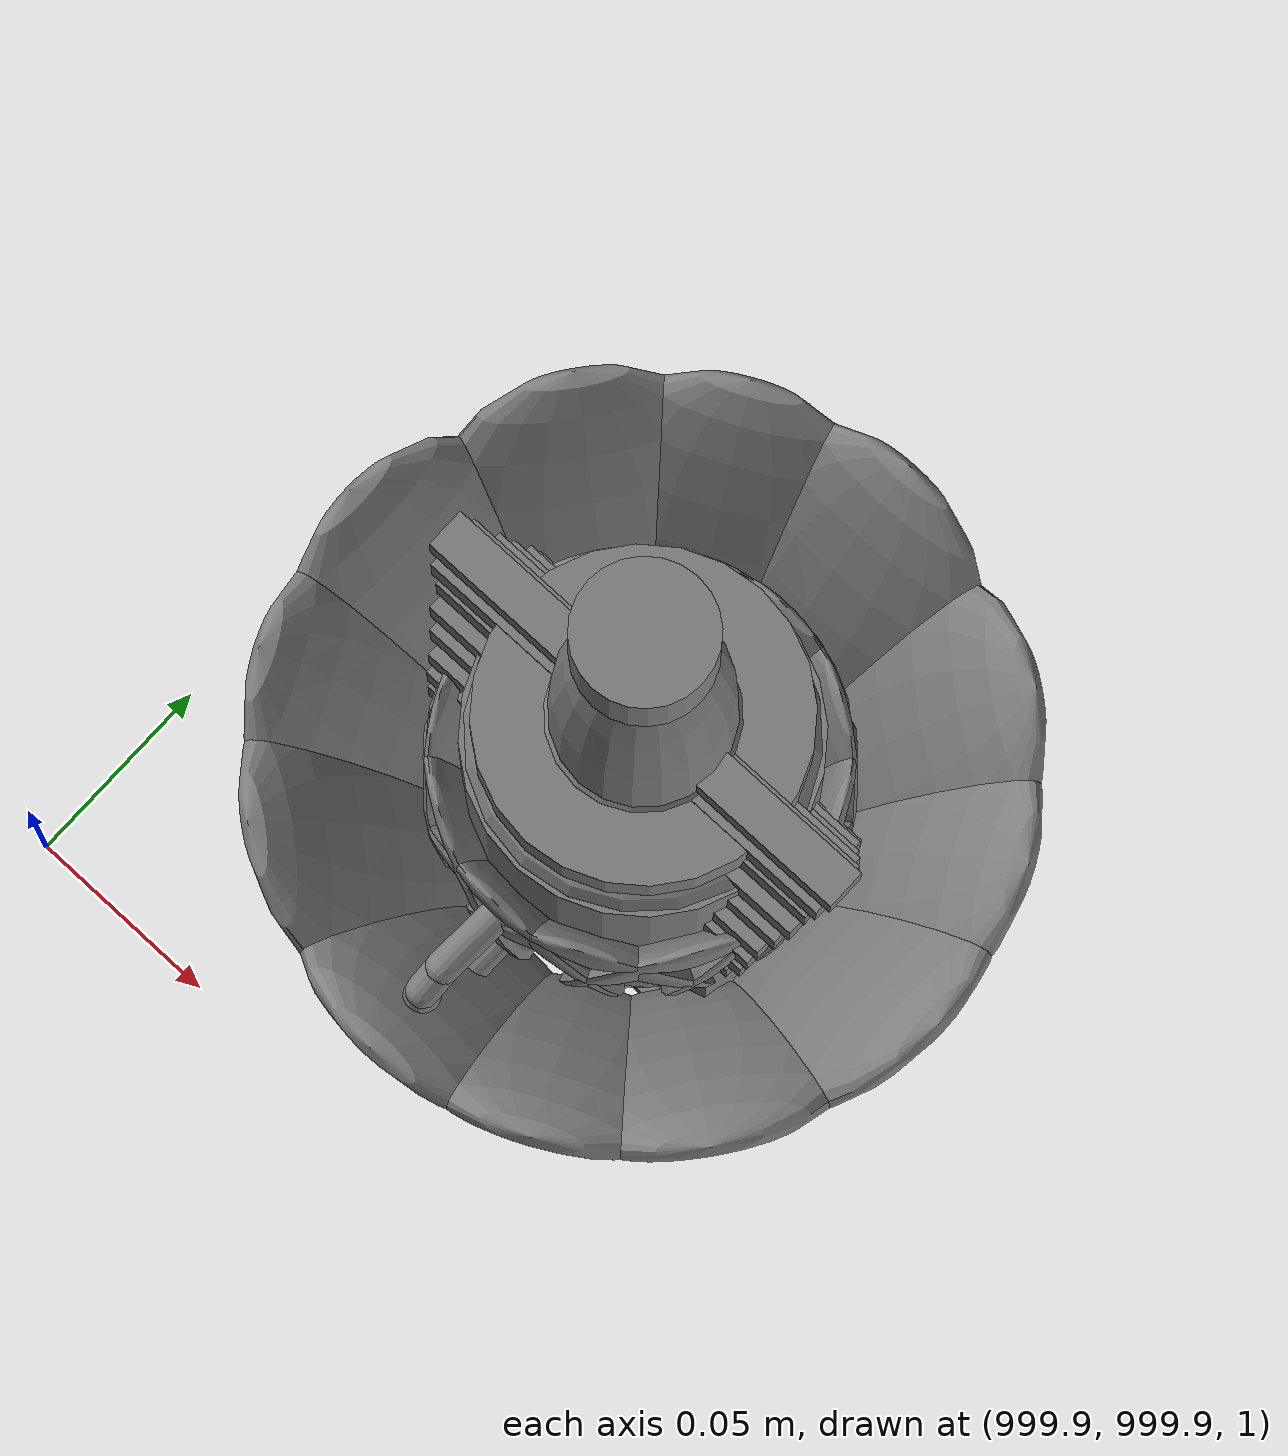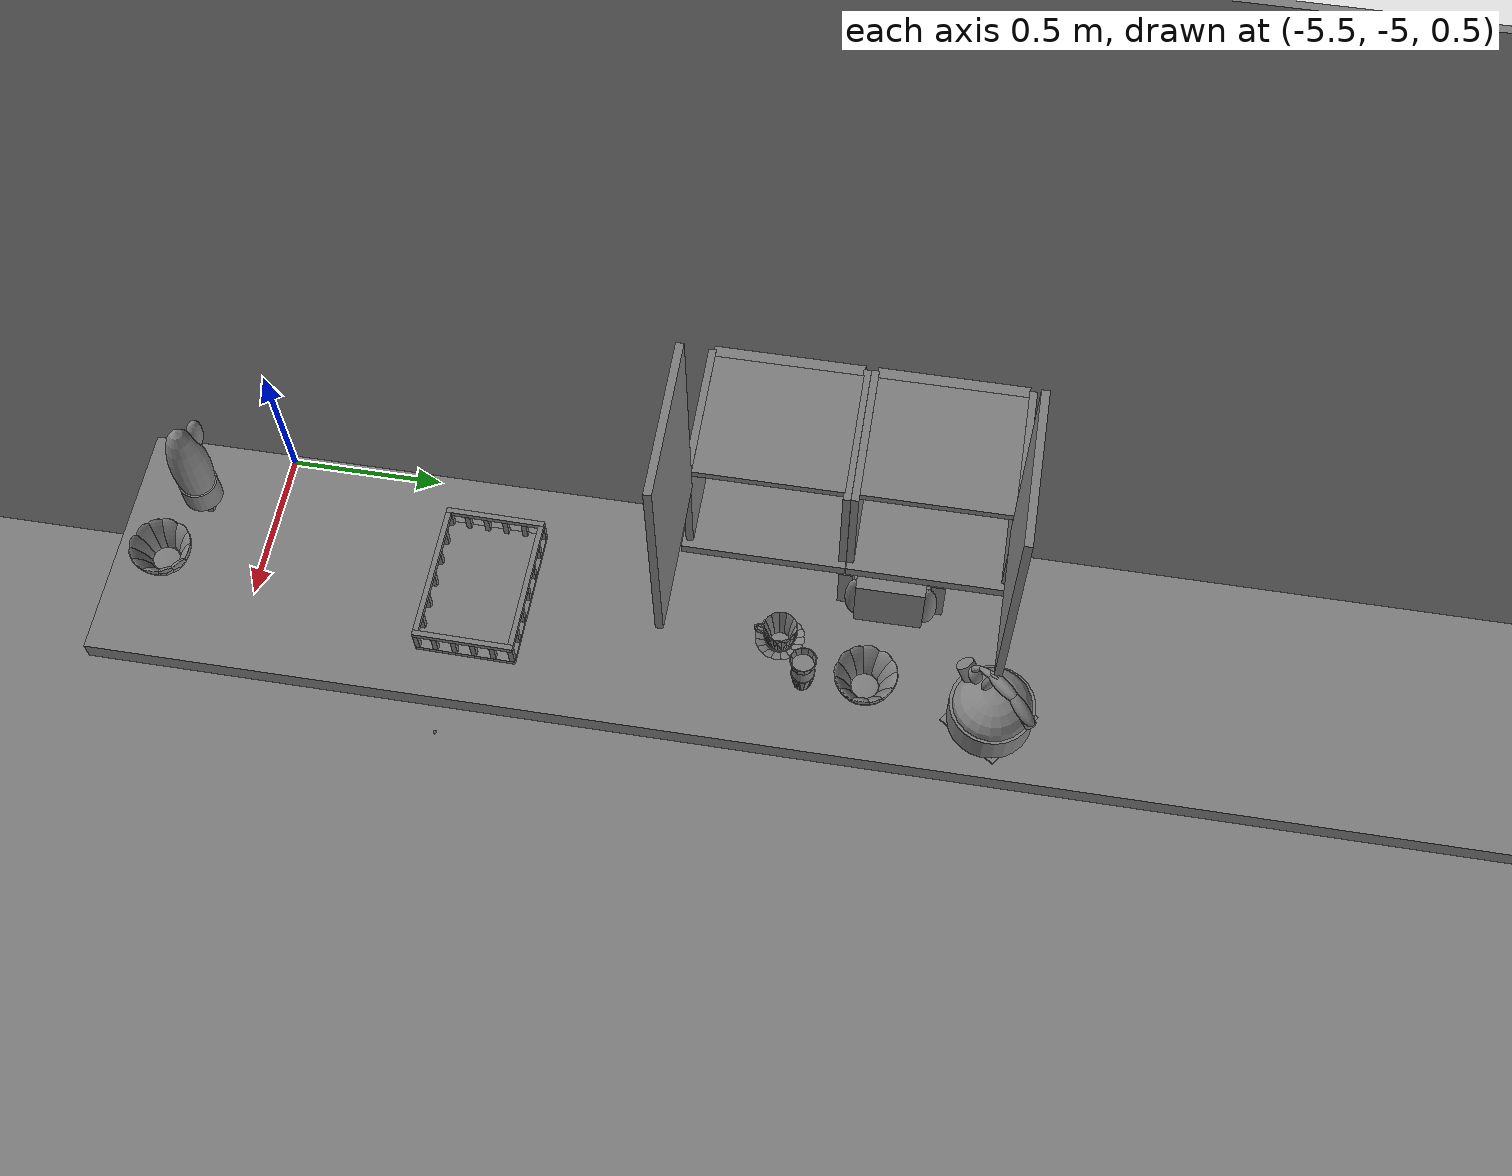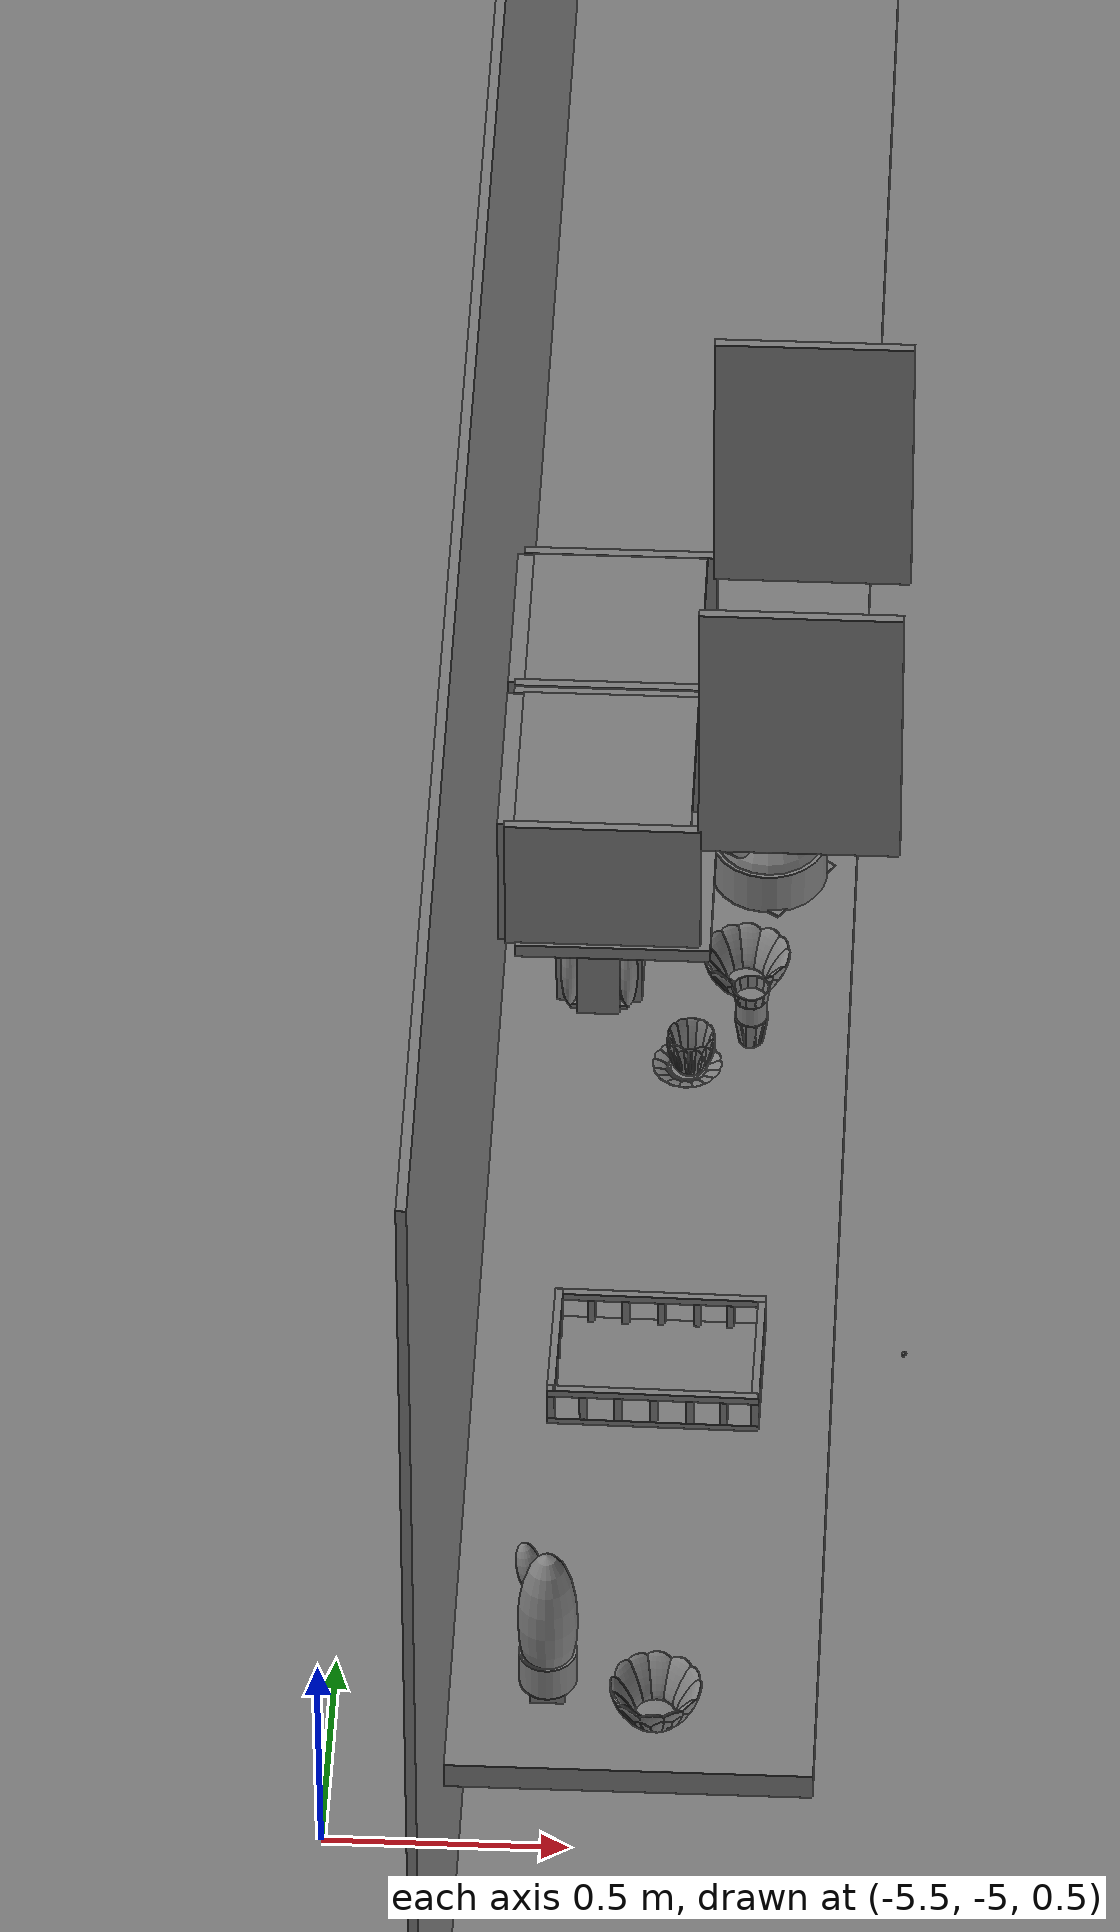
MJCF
<mujoco>
    <option gravity="0.000000000 0.000000000 -9.810000420" timestep="0.0049999999" integrator="implicitfast" density="9.8000002" viscosity="1.8000001e-05" noslip_iterations="10" iterations="100" sdf_iterations="50">
        <flag multiccd="disable"/>
    </option>
    <size memory="1000M"/>
    <compiler coordinate="local"/>
    <worldbody>
        <light cutoff="30" pos="0 1 1" dir="0 -1 -2"/>
        <light cutoff="30" pos="0 -1 1" dir="0 1 -2"/>
        <body pos="-5.046103477 -5.051773071 1.001502514" euler="0.000000000 0.000000000 0.000000000" name="Interactive Objcets_huapen">
            <geom contype="1" conaffinity="1" density="1000" type="ellipsoid" material="" rgba="0.500000000 0.500000000 0.500000000 1.000000000" solimp="0.899999976 0.949999988 0.001000000" friction="1.000000000 0.005000000 0.000100000" solref="0.020000000 1.000000000" margin="0" condim="3" group="0" pos="0.008062840 0.004346371 0.205056787" quat="1.000000000 0.000000000 0.000000000 0.000000000" size="0.059999999 0.059999999 0.180000007" name="Interactive Objcets_huapen_hua_981E0E7B_5F7D_4CD6_94BB_5C3034430597"/>
            <geom contype="1" conaffinity="1" density="1000" type="cylinder" material="" rgba="0.500000000 0.500000000 0.500000000 1.000000000" solimp="0.899999976 0.949999988 0.001000000" friction="1.000000000 0.005000000 0.000100000" solref="0.020000000 1.000000000" margin="0" condim="3" group="0" pos="0.008062840 0.003952026 0.080107450" quat="1.000000000 0.000000000 0.000000000 0.000000000" size="0.057999998 0.039999999 1.000000000" name="Interactive Objcets_huapen_hua_8166CFD9_FA62_45A3_A128_9450C4CA78D4"/>
            <geom contype="1" conaffinity="1" density="1000" type="box" material="" rgba="0.500000000 0.500000000 0.500000000 1.000000000" solimp="0.899999976 0.949999988 0.001000000" friction="1.000000000 0.005000000 0.000100000" solref="0.020000000 1.000000000" margin="0" condim="3" group="0" pos="0.008062840 0.003952503 0.020566106" quat="1.000000000 0.000000000 0.000000000 0.000000000" size="0.035000000 0.035000000 0.020000000" name="Interactive Objcets_huapen_hua_6B7346EB_C4E5_4FAB_AE8D_40080F90B8FD"/>
            <geom contype="1" conaffinity="1" density="1000" type="ellipsoid" material="" rgba="0.500000000 0.500000000 0.500000000 1.000000000" solimp="0.899999976 0.949999988 0.001000000" friction="1.000000000 0.005000000 0.000100000" solref="0.020000000 1.000000000" margin="0" condim="3" group="0" pos="-0.029900074 0.033599377 0.321917295" quat="0.992658079 -0.083605267 -0.087364964 0.002748166" size="0.025000000 0.025000000 0.059999999" name="Interactive Objcets_huapen_hua_684B9586_A207_4712_80CA_3C8B380845C8"/>
            <freejoint name="Interactive Objcets_huapen"/>
        </body>
        <body pos="-4.185104847 -4.476390362 1.763975501" euler="169.179809570 75.230667114 32.954185486" mocap="true" name="spotlight3_SpotLight"/>
        <body pos="1000.000000000 1000.000000000 1.000000000" euler="0.000000000 0.000000000 0.000000000" name="openloong_gripper_2f85_fix_base_usda_jar_01">
            <geom contype="1" conaffinity="1" density="1000" type="box" material="" rgba="0.500000000 0.500000000 0.500000000 1.000000000" solimp="0.899999976 0.949999988 0.001000000" friction="1.000000000 0.005000000 0.000100000" solref="0.020000000 1.000000000" margin="0" condim="3" group="0" pos="0.000000000 0.000000000 0.006158113" quat="1.000000000 0.000000000 0.000000000 0.000000000" size="0.020000000 0.020000000 0.005000000" name="openloong_gripper_2f85_fix_base_usda_geom_B91816CA_25B8_4AD3_84D5_39F19DBBCA16"/>
            <geom contype="1" conaffinity="1" density="1000" type="cylinder" material="" rgba="0.500000000 0.500000000 0.500000000 1.000000000" solimp="0.899999976 0.949999988 0.001000000" friction="1.000000000 0.005000000 0.000100000" solref="0.020000000 1.000000000" margin="0" condim="3" group="0" pos="0.000000000 0.000000000 0.062744498" quat="1.000000000 0.000000000 0.000000000 0.000000000" size="0.041000001 0.052999999 1.000000000" name="openloong_gripper_2f85_fix_base_usda_geom_13B38BA6_63E7_4AA7_92CE_5498ECD622D4"/>
            <geom contype="1" conaffinity="1" density="1000" type="ellipsoid" material="" rgba="0.500000000 0.500000000 0.500000000 1.000000000" solimp="0.899999976 0.949999988 0.001000000" friction="1.000000000 0.005000000 0.000100000" solref="0.020000000 1.000000000" margin="0" condim="3" group="0" pos="0.000000000 0.000000000 0.122252703" quat="1.000000000 0.000000000 0.000000000 0.000000000" size="0.035999998 0.035999998 0.010000000" name="openloong_gripper_2f85_fix_base_usda_geom_AD993B85_0BA0_4F27_851E_DD3D2C0076A3"/>
            <geom contype="1" conaffinity="1" density="1000" type="cylinder" material="" rgba="0.500000000 0.500000000 0.500000000 1.000000000" solimp="0.899999976 0.949999988 0.001000000" friction="1.000000000 0.005000000 0.000100000" solref="0.020000000 1.000000000" margin="0" condim="3" group="0" pos="0.000000000 0.000000000 0.015747190" quat="1.000000000 0.000000000 0.000000000 0.000000000" size="0.035000000 0.010000000 1.000000000" name="openloong_gripper_2f85_fix_base_usda_geom_344A09FB_955F_48B3_A63F_1DB7FD38B43E"/>
            <geom contype="1" conaffinity="1" density="1000" type="ellipsoid" material="" rgba="0.500000000 0.500000000 0.500000000 1.000000000" solimp="0.899999976 0.949999988 0.001000000" friction="1.000000000 0.005000000 0.000100000" solref="0.020000000 1.000000000" margin="0" condim="3" group="0" pos="0.000000000 0.000000000 0.115815401" quat="1.000000000 0.000000000 0.000000000 0.000000000" size="0.039999999 0.039999999 0.010000000" name="openloong_gripper_2f85_fix_base_usda_geom_A91D7A90_E209_4160_9F22_4F8FE942BDD7"/>
            <geom contype="1" conaffinity="1" density="1000" type="cylinder" material="" rgba="0.500000000 0.500000000 0.500000000 1.000000000" solimp="0.899999976 0.949999988 0.001000000" friction="1.000000000 0.005000000 0.000100000" solref="0.020000000 1.000000000" margin="0" condim="3" group="0" pos="0.000000000 0.000000000 0.133183479" quat="1.000000000 0.000000000 0.000000000 0.000000000" size="0.037999999 0.006500000 1.000000000" name="openloong_gripper_2f85_fix_base_usda_geom_3111B0C5_0566_470E_9B67_6488A3A7BE73"/>
            <freejoint name="openloong_gripper_2f85_fix_base_usda_jar_01_joint"/>
            <site size="0.005000000 0.005000000 0.005000000" rgba="0.500000000 0.500000000 0.500000000 1.000000000" pos="0.000000000 0.000000000 0.000000000" quat="1.000000000 0.000000000 0.000000000 0.000000000" group="0" type="sphere" name="openloong_gripper_2f85_fix_base_usda_jar_01site"/>
        </body>
        <body pos="1000.000000000 1000.000000000 1.000000000" euler="0.000000000 0.000000000 0.000000000" name="openloong_gripper_2f85_fix_base_usda_salt">
            <geom contype="1" conaffinity="1" density="1000" type="box" material="" rgba="0.500000000 0.500000000 0.500000000 1.000000000" solimp="0.899999976 0.949999988 0.001000000" friction="1.000000000 0.005000000 0.000100000" solref="0.020000000 1.000000000" margin="0" condim="3" group="0" pos="0.000305176 0.000000000 0.084862232" quat="1.000000000 0.000000000 0.000000000 0.000000000" size="0.048999999 0.018999999 0.005000000" name="openloong_gripper_2f85_fix_base_usda_geom_1E2D0024_E5D7_41CE_A9A4_6C01CB6F87AB"/>
            <geom contype="1" conaffinity="1" density="1000" type="box" material="" rgba="0.500000000 0.500000000 0.500000000 1.000000000" solimp="0.899999976 0.949999988 0.001000000" friction="1.000000000 0.005000000 0.000100000" solref="0.020000000 1.000000000" margin="0" condim="3" group="0" pos="0.000305176 0.000000000 0.104564309" quat="1.000000000 0.000000000 0.000000000 0.000000000" size="0.052000001 0.014000000 0.005000000" name="openloong_gripper_2f85_fix_base_usda_geom_7D3FB633_5B43_4CCE_B015_1EAEDE576C39"/>
            <geom contype="1" conaffinity="1" density="1000" type="box" material="" rgba="0.500000000 0.500000000 0.500000000 1.000000000" solimp="0.899999976 0.949999988 0.001000000" friction="1.000000000 0.005000000 0.000100000" solref="0.020000000 1.000000000" margin="0" condim="3" group="0" pos="0.000305176 0.000000000 0.114487171" quat="1.000000000 0.000000000 0.000000000 0.000000000" size="0.054000001 0.011500000 0.005000000" name="openloong_gripper_2f85_fix_base_usda_geom_DC803ACD_F533_4004_B596_3172C2F25AA5"/>
            <geom contype="1" conaffinity="1" density="1000" type="box" material="" rgba="0.500000000 0.500000000 0.500000000 1.000000000" solimp="0.899999976 0.949999988 0.001000000" friction="1.000000000 0.005000000 0.000100000" solref="0.020000000 1.000000000" margin="0" condim="3" group="0" pos="0.000305176 0.000000000 0.075103164" quat="1.000000000 0.000000000 0.000000000 0.000000000" size="0.048000000 0.020000000 0.005000000" name="openloong_gripper_2f85_fix_base_usda_geom_1881DC5D_D4E7_4D14_871E_462AD0222E4A"/>
            <geom contype="1" conaffinity="1" density="1000" type="box" material="" rgba="0.500000000 0.500000000 0.500000000 1.000000000" solimp="0.899999976 0.949999988 0.001000000" friction="1.000000000 0.005000000 0.000100000" solref="0.020000000 1.000000000" margin="0" condim="3" group="0" pos="0.000305176 0.000000000 0.134892464" quat="1.000000000 0.000000000 0.000000000 0.000000000" size="0.057000000 0.007000000 0.005000000" name="openloong_gripper_2f85_fix_base_usda_geom_DF778128_224B_4DC5_A6E2_BE2B3DE11AB1"/>
            <geom contype="1" conaffinity="1" density="1000" type="box" material="" rgba="0.500000000 0.500000000 0.500000000 1.000000000" solimp="0.899999976 0.949999988 0.001000000" friction="1.000000000 0.005000000 0.000100000" solref="0.020000000 1.000000000" margin="0" condim="3" group="0" pos="0.000305176 0.000000000 0.094920278" quat="1.000000000 0.000000000 0.000000000 0.000000000" size="0.050000001 0.017000001 0.005000000" name="openloong_gripper_2f85_fix_base_usda_geom_96206BCE_598D_4033_8737_B1DC19A0C577"/>
            <geom contype="1" conaffinity="1" density="1000" type="box" material="" rgba="0.500000000 0.500000000 0.500000000 1.000000000" solimp="0.899999976 0.949999988 0.001000000" friction="1.000000000 0.005000000 0.000100000" solref="0.020000000 1.000000000" margin="0" condim="3" group="0" pos="0.000305176 0.000000000 0.065204859" quat="1.000000000 0.000000000 0.000000000 0.000000000" size="0.045000002 0.021000000 0.005000000" name="openloong_gripper_2f85_fix_base_usda_geom_96579A54_9679_48AB_A56D_ACD93D125F58"/>
            <geom contype="1" conaffinity="1" density="1000" type="box" material="" rgba="0.500000000 0.500000000 0.500000000 1.000000000" solimp="0.899999976 0.949999988 0.001000000" friction="1.000000000 0.005000000 0.000100000" solref="0.020000000 1.000000000" margin="0" condim="3" group="0" pos="0.000305176 0.000000000 0.144135714" quat="1.000000000 0.000000000 0.000000000 0.000000000" size="0.059000000 0.005000000 0.004000000" name="openloong_gripper_2f85_fix_base_usda_geom_681697B1_8E61_4BDA_9210_CC72EFF4DDAF"/>
            <geom contype="1" conaffinity="1" density="1000" type="box" material="" rgba="0.500000000 0.500000000 0.500000000 1.000000000" solimp="0.899999976 0.949999988 0.001000000" friction="1.000000000 0.005000000 0.000100000" solref="0.020000000 1.000000000" margin="0" condim="3" group="0" pos="0.000000000 0.000000000 0.031593561" quat="1.000000000 0.000000000 0.000000000 0.000000000" size="0.041999999 0.024000000 0.029999999" name="openloong_gripper_2f85_fix_base_usda_geom_07072A8E_CFF1_4856_9383_89BFC6B8DFD1"/>
            <geom contype="1" conaffinity="1" density="1000" type="box" material="" rgba="0.500000000 0.500000000 0.500000000 1.000000000" solimp="0.899999976 0.949999988 0.001000000" friction="1.000000000 0.005000000 0.000100000" solref="0.020000000 1.000000000" margin="0" condim="3" group="0" pos="0.000305176 0.000000000 0.124608755" quat="1.000000000 0.000000000 0.000000000 0.000000000" size="0.055000000 0.008000000 0.005000000" name="openloong_gripper_2f85_fix_base_usda_geom_D3B45B93_F653_4E93_A230_8597F737A594"/>
            <freejoint name="openloong_gripper_2f85_fix_base_usda_salt_joint"/>
            <site size="0.005000000 0.005000000 0.005000000" rgba="0.500000000 0.500000000 0.500000000 1.000000000" pos="0.000000000 0.000000000 0.000000000" quat="1.000000000 0.000000000 0.000000000 0.000000000" group="0" type="sphere" name="openloong_gripper_2f85_fix_base_usda_saltsite"/>
        </body>
        <body pos="1000.000000000 1000.000000000 1.000000000" euler="0.000000000 0.000000000 0.000000000" name="openloong_gripper_2f85_fix_base_usda_bow_yellow_kps">
            <geom contype="1" conaffinity="1" density="1000" type="ellipsoid" material="" rgba="0.500000000 0.500000000 0.500000000 1.000000000" solimp="0.899999976 0.949999988 0.001000000" friction="1.000000000 0.005000000 0.000100000" solref="0.020000000 1.000000000" margin="0" condim="3" group="0" pos="-0.052185059 0.040283203 0.044118762" quat="0.919264615 -0.076883033 -0.225593656 -0.313287765" size="0.010000000 0.039999999 0.052000001" name="openloong_gripper_2f85_fix_base_usda_geom_A065591E_65F6_44C1_AC73_236D4AB5A729"/>
            <geom contype="1" conaffinity="1" density="1000" type="ellipsoid" material="" rgba="0.500000000 0.500000000 0.500000000 1.000000000" solimp="0.899999976 0.949999988 0.001000000" friction="1.000000000 0.005000000 0.000100000" solref="0.020000000 1.000000000" margin="0" condim="3" group="0" pos="-0.000061035 0.065979004 0.044118762" quat="0.687598765 -0.168314874 -0.168741167 -0.685860336" size="0.010000000 0.039999999 0.052000001" name="openloong_gripper_2f85_fix_base_usda_geom_6A92F1D0_B790_43C9_8B5F_4440F9711CA5"/>
            <geom contype="1" conaffinity="1" density="1000" type="box" material="" rgba="0.500000000 0.500000000 0.500000000 1.000000000" solimp="0.899999976 0.949999988 0.001000000" friction="1.000000000 0.005000000 0.000100000" solref="0.020000000 1.000000000" margin="0" condim="3" group="0" pos="0.000061035 0.000000000 -0.002001643" quat="1.000000000 0.000000000 0.000000000 0.000000000" size="0.029999999 0.029999999 0.002000000" name="openloong_gripper_2f85_fix_base_usda_geom_020D08F3_1D26_4F95_8363_BA481008EC86"/>
            <geom contype="1" conaffinity="1" density="1000" type="ellipsoid" material="" rgba="0.500000000 0.500000000 0.500000000 1.000000000" solimp="0.899999976 0.949999988 0.001000000" friction="1.000000000 0.005000000 0.000100000" solref="0.020000000 1.000000000" margin="0" condim="3" group="0" pos="0.029418945 -0.059082031 0.044118762" quat="0.825555861 0.125530601 0.202597082 -0.511521280" size="0.010000000 0.039999999 0.052000001" name="openloong_gripper_2f85_fix_base_usda_geom_D89FF77D_5FBD_42B0_AD74_50E71BB54B06"/>
            <geom contype="1" conaffinity="1" density="1000" type="ellipsoid" material="" rgba="0.500000000 0.500000000 0.500000000 1.000000000" solimp="0.899999976 0.949999988 0.001000000" friction="1.000000000 0.005000000 0.000100000" solref="0.020000000 1.000000000" margin="0" condim="3" group="0" pos="0.000244141 -0.065979004 0.044118762" quat="0.687598765 0.168314651 0.168741375 -0.685860336" size="0.010000000 0.039999999 0.052000001" name="openloong_gripper_2f85_fix_base_usda_geom_7DD0D5F0_9438_46EB_A355_9AF8AAD64466"/>
            <geom contype="1" conaffinity="1" density="1000" type="ellipsoid" material="" rgba="0.500000000 0.500000000 0.500000000 1.000000000" solimp="0.899999976 0.949999988 0.001000000" friction="1.000000000 0.005000000 0.000100000" solref="0.020000000 1.000000000" margin="0" condim="3" group="0" pos="0.000061035 0.000000000 0.000446677" quat="1.000000000 0.000000000 0.000000000 0.000000000" size="0.039999999 0.039999999 0.002000000" name="openloong_gripper_2f85_fix_base_usda_geom_45CF3C24_C5ED_4E07_8932_4197DC152DBF"/>
            <geom contype="1" conaffinity="1" density="1000" type="ellipsoid" material="" rgba="0.500000000 0.500000000 0.500000000 1.000000000" solimp="0.899999976 0.949999988 0.001000000" friction="1.000000000 0.005000000 0.000100000" solref="0.020000000 1.000000000" margin="0" condim="3" group="0" pos="0.059082031 0.029541016 0.044118762" quat="0.223252773 -0.231952220 -0.054787423 -0.945174456" size="0.010000000 0.039999999 0.052000001" name="openloong_gripper_2f85_fix_base_usda_geom_FD29DA33_4B86_4AC2_8BB4_76AB7AF76916"/>
            <geom contype="1" conaffinity="1" density="1000" type="ellipsoid" material="" rgba="0.500000000 0.500000000 0.500000000 1.000000000" solimp="0.899999976 0.949999988 0.001000000" friction="1.000000000 0.005000000 0.000100000" solref="0.020000000 1.000000000" margin="0" condim="3" group="0" pos="0.000061035 0.000000000 0.007335305" quat="1.000000000 0.000000000 0.000000000 0.000000000" size="0.039999999 0.039999999 0.002000000" name="openloong_gripper_2f85_fix_base_usda_geom_50B1D8CC_6067_4C6D_9475_B55174EB2673"/>
            <geom contype="1" conaffinity="1" density="1000" type="ellipsoid" material="" rgba="0.500000000 0.500000000 0.500000000 1.000000000" solimp="0.899999976 0.949999988 0.001000000" friction="1.000000000 0.005000000 0.000100000" solref="0.020000000 1.000000000" margin="0" condim="3" group="0" pos="-0.029296875 0.059082031 0.044118762" quat="0.825555861 -0.125530809 -0.202596918 -0.511521280" size="0.010000000 0.039999999 0.052000001" name="openloong_gripper_2f85_fix_base_usda_geom_D2F218A9_B080_4225_B1F7_54DD98F32394"/>
            <geom contype="1" conaffinity="1" density="1000" type="ellipsoid" material="" rgba="0.500000000 0.500000000 0.500000000 1.000000000" solimp="0.899999976 0.949999988 0.001000000" friction="1.000000000 0.005000000 0.000100000" solref="0.020000000 1.000000000" margin="0" condim="3" group="0" pos="0.040222168 0.052368164 0.044118762" quat="0.429593176 -0.213750049 -0.105424821 -0.871002972" size="0.010000000 0.039999999 0.052000001" name="openloong_gripper_2f85_fix_base_usda_geom_2DC1E339_D1A6_4BC3_8D51_B39AF0945214"/>
            <geom contype="1" conaffinity="1" density="1000" type="ellipsoid" material="" rgba="0.500000000 0.500000000 0.500000000 1.000000000" solimp="0.899999976 0.949999988 0.001000000" friction="1.000000000 0.005000000 0.000100000" solref="0.020000000 1.000000000" margin="0" condim="3" group="0" pos="0.066040039 0.000000000 0.044118762" quat="0.971183062 -0.000000156 0.238334835 0.000000030" size="0.010000000 0.039999999 0.052000001" name="openloong_gripper_2f85_fix_base_usda_geom_EF3919D9_B898_47EB_AB29_D00A2CA68B24"/>
            <geom contype="1" conaffinity="1" density="1000" type="ellipsoid" material="" rgba="0.500000000 0.500000000 0.500000000 1.000000000" solimp="0.899999976 0.949999988 0.001000000" friction="1.000000000 0.005000000 0.000100000" solref="0.020000000 1.000000000" margin="0" condim="3" group="0" pos="0.052307129 -0.040283203 0.044118762" quat="0.919264674 0.076882750 0.225593731 -0.313287705" size="0.010000000 0.039999999 0.052000001" name="openloong_gripper_2f85_fix_base_usda_geom_FD9A2857_402A_43FA_8B76_EDD2739FF8E5"/>
            <geom contype="1" conaffinity="1" density="1000" type="ellipsoid" material="" rgba="0.500000000 0.500000000 0.500000000 1.000000000" solimp="0.899999976 0.949999988 0.001000000" friction="1.000000000 0.005000000 0.000100000" solref="0.020000000 1.000000000" margin="0" condim="3" group="0" pos="-0.065917969 0.000000000 0.044118762" quat="0.971183062 -0.000000142 -0.238334835 0.000000030" size="0.010000000 0.039999999 0.052000001" name="openloong_gripper_2f85_fix_base_usda_geom_176C5AEF_61B8_4165_940F_FB4B4B259778"/>
            <geom contype="1" conaffinity="1" density="1000" type="ellipsoid" material="" rgba="0.500000000 0.500000000 0.500000000 1.000000000" solimp="0.899999976 0.949999988 0.001000000" friction="1.000000000 0.005000000 0.000100000" solref="0.020000000 1.000000000" margin="0" condim="3" group="0" pos="-0.058898926 -0.029541016 0.044118762" quat="0.223252758 0.231952101 0.054787733 -0.945174575" size="0.010000000 0.039999999 0.052000001" name="openloong_gripper_2f85_fix_base_usda_geom_AAF002D2_A7E3_4B82_9754_94476F318EB1"/>
            <geom contype="1" conaffinity="1" density="1000" type="ellipsoid" material="" rgba="0.500000000 0.500000000 0.500000000 1.000000000" solimp="0.899999976 0.949999988 0.001000000" friction="1.000000000 0.005000000 0.000100000" solref="0.020000000 1.000000000" margin="0" condim="3" group="0" pos="-0.040100098 -0.052368164 0.044118762" quat="0.429593235 0.213749886 0.105425082 -0.871003032" size="0.010000000 0.039999999 0.052000001" name="openloong_gripper_2f85_fix_base_usda_geom_2F7DC829_3DCF_42EB_89D9_A43598E0260F"/>
            <freejoint name="openloong_gripper_2f85_fix_base_usda_bow_yellow_kps_joint"/>
            <site size="0.005000000 0.005000000 0.005000000" rgba="0.500000000 0.500000000 0.500000000 1.000000000" pos="0.000000000 0.000000000 0.000000000" quat="0.999961913 0.008726534 0.000000000 0.000000000" group="0" type="sphere" name="openloong_gripper_2f85_fix_base_usda_bow_yellow_kps"/>
        </body>
        <body pos="-4.006589890 -3.853657007 1.790283680" euler="-90.083862305 17.835052490 -123.182907104" mocap="true" name="spotlight2_SpotLight"/>
        <body pos="1000.000000000 1000.000000000 1.000000000" euler="0.000000000 0.000000000 0.000000000" name="openloong_gripper_2f85_fix_base_usda_coffeecup_white_kps">
            <geom contype="1" conaffinity="1" density="1000" type="capsule" material="" rgba="0.500000000 0.500000000 0.500000000 1.000000000" solimp="0.899999976 0.949999988 0.001000000" friction="1.000000000 0.005000000 0.000100000" solref="0.020000000 1.000000000" margin="0" condim="3" group="0" pos="-0.000854492 -0.065795898 0.050029993" quat="0.343559504 -0.613204718 0.626912475 0.336047262" size="0.004000000 0.005000000 1.000000000" name="openloong_gripper_2f85_fix_base_usda_geom_56488D56_64FF_45E5_AD57_ABD61E625E03"/>
            <geom contype="1" conaffinity="1" density="1000" type="ellipsoid" material="" rgba="0.500000000 0.500000000 0.500000000 1.000000000" solimp="0.899999976 0.949999988 0.001000000" friction="1.000000000 0.005000000 0.000100000" solref="0.020000000 1.000000000" margin="0" condim="3" group="0" pos="-0.000793457 -0.038452148 0.048040152" quat="0.711656272 0.066323131 -0.067805752 0.696095467" size="0.005000000 0.029999999 0.048999999" name="openloong_gripper_2f85_fix_base_usda_geom_A3997C0E_3DFC_4922_9BF6_E922A9F7D313"/>
            <geom contype="1" conaffinity="1" density="1000" type="ellipsoid" material="" rgba="0.500000000 0.500000000 0.500000000 1.000000000" solimp="0.899999976 0.949999988 0.001000000" friction="1.000000000 0.005000000 0.000100000" solref="0.020000000 1.000000000" margin="0" condim="3" group="0" pos="0.037719727 -0.001892090 0.048040152" quat="0.995387912 0.001371633 0.094835162 -0.014391154" size="0.005000000 0.029999999 0.048999999" name="openloong_gripper_2f85_fix_base_usda_geom_C1C9B541_2602_4143_92E0_BEA41F1DFCCB"/>
            <geom contype="1" conaffinity="1" density="1000" type="ellipsoid" material="" rgba="0.500000000 0.500000000 0.500000000 1.000000000" solimp="0.899999976 0.949999988 0.001000000" friction="1.000000000 0.005000000 0.000100000" solref="0.020000000 1.000000000" margin="0" condim="3" group="0" pos="0.033996582 0.015502930 0.048040152" quat="0.970659733 -0.021051638 0.092478797 0.220962167" size="0.005000000 0.029999999 0.048999999" name="openloong_gripper_2f85_fix_base_usda_geom_7D2614EB_327D_4141_B772_5A63A5E0651A"/>
            <geom contype="1" conaffinity="1" density="1000" type="box" material="" rgba="0.500000000 0.500000000 0.500000000 1.000000000" solimp="0.899999976 0.949999988 0.001000000" friction="1.000000000 0.005000000 0.000100000" solref="0.020000000 1.000000000" margin="0" condim="3" group="0" pos="0.000793457 -0.000183105 0.000156164" quat="0.714879215 0.000000000 0.000000000 0.699247897" size="0.020000000 0.020000000 0.002000000" name="openloong_gripper_2f85_fix_base_usda_geom_18BA8C1D_8184_44F0_8D2F_7D7E8FF0599D"/>
            <geom contype="1" conaffinity="1" density="1000" type="ellipsoid" material="" rgba="0.500000000 0.500000000 0.500000000 1.000000000" solimp="0.899999976 0.949999988 0.001000000" friction="1.000000000 0.005000000 0.000100000" solref="0.020000000 1.000000000" margin="0" condim="3" group="0" pos="-0.019409180 -0.033081055 0.048040152" quat="0.866879702 0.046630561 -0.082595348 0.489411235" size="0.005000000 0.029999999 0.048999999" name="openloong_gripper_2f85_fix_base_usda_geom_188A5108_B3F1_4D6F_B9B6_E0C083B9AC7D"/>
            <geom contype="1" conaffinity="1" density="1000" type="ellipsoid" material="" rgba="0.500000000 0.500000000 0.500000000 1.000000000" solimp="0.899999976 0.949999988 0.001000000" friction="1.000000000 0.005000000 0.000100000" solref="0.020000000 1.000000000" margin="0" condim="3" group="0" pos="-0.016052246 0.033264160 0.048040152" quat="0.840792537 -0.050782297 -0.080109790 -0.532983541" size="0.005000000 0.029999999 0.048999999" name="openloong_gripper_2f85_fix_base_usda_geom_2A9ACE17_BC7A_41E4_8DED_EF2E68CA570C"/>
            <geom contype="1" conaffinity="1" density="1000" type="capsule" material="" rgba="0.500000000 0.500000000 0.500000000 1.000000000" solimp="0.899999976 0.949999988 0.001000000" friction="1.000000000 0.005000000 0.000100000" solref="0.020000000 1.000000000" margin="0" condim="3" group="0" pos="-0.000549316 -0.053527832 0.046825886" quat="0.505496025 -0.494442940 0.505495846 0.494442940" size="0.004000000 0.005000000 1.000000000" name="openloong_gripper_2f85_fix_base_usda_geom_F3CD92AE_9FF6_4B37_8409_E60FBBE83F63"/>
            <geom contype="1" conaffinity="1" density="1000" type="ellipsoid" material="" rgba="0.500000000 0.500000000 0.500000000 1.000000000" solimp="0.899999976 0.949999988 0.001000000" friction="1.000000000 0.005000000 0.000100000" solref="0.020000000 1.000000000" margin="0" condim="3" group="0" pos="-0.032104492 0.018920898 0.048040152" quat="0.958129764 -0.025742561 -0.091288343 -0.270168930" size="0.005000000 0.029999999 0.048999999" name="openloong_gripper_2f85_fix_base_usda_geom_94C24213_E8A8_4EA2_948E_F44B37D30BF5"/>
            <geom contype="1" conaffinity="1" density="1000" type="ellipsoid" material="" rgba="0.500000000 0.500000000 0.500000000 1.000000000" solimp="0.899999976 0.949999988 0.001000000" friction="1.000000000 0.005000000 0.000100000" solref="0.020000000 1.000000000" margin="0" condim="3" group="0" pos="-0.037597656 0.000305176 0.048040152" quat="0.995387554 -0.001371440 -0.094839431 -0.014389008" size="0.005000000 0.029999999 0.048999999" name="openloong_gripper_2f85_fix_base_usda_geom_ADD03820_F73F_4AAB_9FA9_433EB2BEAC15"/>
            <geom contype="1" conaffinity="1" density="1000" type="capsule" material="" rgba="0.500000000 0.500000000 0.500000000 1.000000000" solimp="0.899999976 0.949999988 0.001000000" friction="1.000000000 0.005000000 0.000100000" solref="0.020000000 1.000000000" margin="0" condim="3" group="0" pos="-0.000366211 -0.043762207 0.044118762" quat="0.260488123 -0.651174724 0.665731549 0.254792154" size="0.004000000 0.003000000 1.000000000" name="openloong_gripper_2f85_fix_base_usda_geom_83FA480A_6AA4_44EA_B64A_730E43DF210C"/>
            <geom contype="1" conaffinity="1" density="1000" type="capsule" material="" rgba="0.500000000 0.500000000 0.500000000 1.000000000" solimp="0.899999976 0.949999988 0.001000000" friction="1.000000000 0.005000000 0.000100000" solref="0.020000000 1.000000000" margin="0" condim="3" group="0" pos="-0.000915527 -0.068542480 0.082936406" quat="0.624995589 -0.339446366 0.347034454 0.611329615" size="0.004000000 0.004000000 1.000000000" name="openloong_gripper_2f85_fix_base_usda_geom_A5B25AC8_B90D_407D_B769_50B8490C5E26"/>
            <geom contype="1" conaffinity="1" density="1000" type="ellipsoid" material="" rgba="0.500000000 0.500000000 0.500000000 1.000000000" solimp="0.899999976 0.949999988 0.001000000" friction="1.000000000 0.005000000 0.000100000" solref="0.020000000 1.000000000" margin="0" condim="3" group="0" pos="0.016113281 -0.034851074 0.048040152" quat="0.840793252 0.050779939 0.080106191 -0.532983422" size="0.005000000 0.029999999 0.048999999" name="openloong_gripper_2f85_fix_base_usda_geom_28DAC48A_B506_4D65_BF5B_FB922F72628C"/>
            <geom contype="1" conaffinity="1" density="1000" type="ellipsoid" material="" rgba="0.500000000 0.500000000 0.500000000 1.000000000" solimp="0.899999976 0.949999988 0.001000000" friction="1.000000000 0.005000000 0.000100000" solref="0.020000000 1.000000000" margin="0" condim="3" group="0" pos="0.000854492 0.036865234 0.048040152" quat="0.711656570 -0.066320375 0.067802906 0.696095705" size="0.005000000 0.029999999 0.048999999" name="openloong_gripper_2f85_fix_base_usda_geom_D792E28F_BBA6_4474_958D_A8B4A96DD049"/>
            <geom contype="1" conaffinity="1" density="1000" type="ellipsoid" material="" rgba="0.500000000 0.500000000 0.500000000 1.000000000" solimp="0.899999976 0.949999988 0.001000000" friction="1.000000000 0.005000000 0.000100000" solref="0.020000000 1.000000000" margin="0" condim="3" group="0" pos="-0.033935547 -0.017089844 0.048040152" quat="0.970659137 0.021052625 -0.092483103 0.220962465" size="0.005000000 0.029999999 0.048999999" name="openloong_gripper_2f85_fix_base_usda_geom_702D69E1_E0EE_4D4A_BDCC_0A09ABAB0AE4"/>
            <geom contype="1" conaffinity="1" density="1000" type="ellipsoid" material="" rgba="0.500000000 0.500000000 0.500000000 1.000000000" solimp="0.899999976 0.949999988 0.001000000" friction="1.000000000 0.005000000 0.000100000" solref="0.020000000 1.000000000" margin="0" condim="3" group="0" pos="0.019531250 0.031494141 0.048040152" quat="0.866880119 -0.046628602 0.082591817 0.489411235" size="0.005000000 0.029999999 0.048999999" name="openloong_gripper_2f85_fix_base_usda_geom_1288FD79_C359_4CDF_AA7A_770591F79795"/>
            <geom contype="1" conaffinity="1" density="1000" type="ellipsoid" material="" rgba="0.500000000 0.500000000 0.500000000 1.000000000" solimp="0.899999976 0.949999988 0.001000000" friction="1.000000000 0.005000000 0.000100000" solref="0.020000000 1.000000000" margin="0" condim="3" group="0" pos="0.032165527 -0.020507812 0.048040152" quat="0.958128154 0.025740955 0.091285400 -0.270175666" size="0.005000000 0.029999999 0.048999999" name="openloong_gripper_2f85_fix_base_usda_geom_42366EE3_AD9F_476B_8513_DC19754CA80C"/>
            <geom contype="1" conaffinity="1" density="1000" type="capsule" material="" rgba="0.500000000 0.500000000 0.500000000 1.000000000" solimp="0.899999976 0.949999988 0.001000000" friction="1.000000000 0.005000000 0.000100000" solref="0.020000000 1.000000000" margin="0" condim="3" group="0" pos="-0.000610352 -0.056823730 0.083572865" quat="0.452654332 -0.541215360 0.553313971 0.442756712" size="0.004000000 0.009000000 1.000000000" name="openloong_gripper_2f85_fix_base_usda_geom_E7B39CC6_3817_476A_9049_BF045AB20BE4"/>
            <geom contype="1" conaffinity="1" density="1000" type="ellipsoid" material="" rgba="0.500000000 0.500000000 0.500000000 1.000000000" solimp="0.899999976 0.949999988 0.001000000" friction="1.000000000 0.005000000 0.000100000" solref="0.020000000 1.000000000" margin="0" condim="3" group="0" pos="0.000061035 -0.000183105 0.001848221" quat="0.714879215 0.000000000 0.000000000 0.699247897" size="0.029999999 0.029999999 0.001000000" name="openloong_gripper_2f85_fix_base_usda_geom_A830AE86_DCC8_48C3_9546_EB1D9E97496B"/>
            <geom contype="1" conaffinity="1" density="1000" type="capsule" material="" rgba="0.500000000 0.500000000 0.500000000 1.000000000" solimp="0.899999976 0.949999988 0.001000000" friction="1.000000000 0.005000000 0.000100000" solref="0.020000000 1.000000000" margin="0" condim="3" group="0" pos="-0.000976562 -0.071838379 0.066101432" quat="0.031849027 -0.698553741 0.714169443 0.031152546" size="0.004000000 0.012000000 1.000000000" name="openloong_gripper_2f85_fix_base_usda_geom_86E19F30_44E8_4FA5_B6F3_132868AF96F4"/>
            <freejoint name="openloong_gripper_2f85_fix_base_usda_coffeecup_white_kps_joint"/>
            <site size="0.005000000 0.005000000 0.005000000" rgba="0.500000000 0.500000000 0.500000000 1.000000000" pos="0.000000000 0.000000000 0.000000000" quat="0.999961913 0.008726534 0.000000000 0.000000000" group="0" type="sphere" name="openloong_gripper_2f85_fix_base_usda_coffeecup_white_kps"/>
        </body>
        <body pos="-4.447736740 -4.315368652 1.839290857" euler="-72.935775757 45.048149109 -155.246459961" mocap="true" name="spotlight5_SpotLight"/>
        <body pos="1000.000000000 1000.000000000 1.000000000" euler="0.000000000 0.000000000 0.000000000" name="openloong_gripper_2f85_fix_base_usda_bottle_red">
            <geom contype="1" conaffinity="1" density="1000" type="ellipsoid" material="" rgba="0.500000000 0.500000000 0.500000000 1.000000000" solimp="0.899999976 0.949999988 0.001000000" friction="1.000000000 0.005000000 0.000100000" solref="0.020000000 1.000000000" margin="0" condim="3" group="0" pos="0.000000000 0.000000000 0.144284487" quat="1.000000000 0.000000000 0.000000000 0.000000000" size="0.021000000 0.021000000 0.079999998" name="openloong_gripper_2f85_fix_base_usda_geom_91D1177E_D662_4741_A833_B15D4416A3EB"/>
            <geom contype="1" conaffinity="1" density="1000" type="cylinder" material="" rgba="0.500000000 0.500000000 0.500000000 1.000000000" solimp="0.899999976 0.949999988 0.001000000" friction="1.000000000 0.005000000 0.000100000" solref="0.020000000 1.000000000" margin="0" condim="3" group="0" pos="0.000000000 0.000000000 0.220618963" quat="1.000000000 0.000000000 0.000000000 0.000000000" size="0.016000001 0.010000000 1.000000000" name="openloong_gripper_2f85_fix_base_usda_geom_055193B6_350C_49A1_8CA9_FBA0DF88E0D2"/>
            <geom contype="1" conaffinity="1" density="1000" type="ellipsoid" material="" rgba="0.500000000 0.500000000 0.500000000 1.000000000" solimp="0.899999976 0.949999988 0.001000000" friction="1.000000000 0.005000000 0.000100000" solref="0.020000000 1.000000000" margin="0" condim="3" group="0" pos="0.000000000 0.000000000 0.118945479" quat="1.000000000 0.000000000 0.000000000 0.000000000" size="0.030999999 0.030999999 0.029999999" name="openloong_gripper_2f85_fix_base_usda_geom_87CF074C_949B_4DFF_8E1C_91D7090C59CB"/>
            <geom contype="1" conaffinity="1" density="1000" type="box" material="" rgba="0.500000000 0.500000000 0.500000000 1.000000000" solimp="0.899999976 0.949999988 0.001000000" friction="1.000000000 0.005000000 0.000100000" solref="0.020000000 1.000000000" margin="0" condim="3" group="0" pos="0.000000000 0.000000000 0.002189159" quat="1.000000000 0.000000000 0.000000000 0.000000000" size="0.020000000 0.020000000 0.003000000" name="openloong_gripper_2f85_fix_base_usda_geom_DA85200B_E88D_46E8_8A68_600B5195D38E"/>
            <geom contype="1" conaffinity="1" density="1000" type="cylinder" material="" rgba="0.500000000 0.500000000 0.500000000 1.000000000" solimp="0.899999976 0.949999988 0.001000000" friction="1.000000000 0.005000000 0.000100000" solref="0.020000000 1.000000000" margin="0" condim="3" group="0" pos="0.000000000 -0.000366211 0.060884237" quat="1.000000000 0.000000000 0.000000000 0.000000000" size="0.030999999 0.057999998 1.000000000" name="openloong_gripper_2f85_fix_base_usda_geom_D96C3B6F_9127_49EA_BC3F_FFA6E7A2D9FF"/>
            <freejoint name="openloong_gripper_2f85_fix_base_usda_bottle_red_joint"/>
            <site size="0.005000000 0.005000000 0.005000000" rgba="0.500000000 0.500000000 0.500000000 1.000000000" pos="0.000000000 0.000000000 0.000000000" quat="0.999961913 0.008726535 0.000000000 0.000000000" group="0" type="sphere" name="openloong_gripper_2f85_fix_base_usda_bottle_redsite"/>
        </body>
        <body pos="0.000000000 0.000000000 0.000000000" euler="0.000000000 0.000000000 0.000000000" name="Static Objcets_Static Objcets">
            <geom contype="1" conaffinity="1" density="1000" type="box" material="" rgba="0.500000000 0.500000000 0.500000000 1.000000000" solimp="0.899999976 0.949999988 0.001000000" friction="1.000000000 0.005000000 0.000100000" solref="0.020000000 1.000000000" margin="0" condim="3" group="0" pos="-4.999745846 -3.497932911 1.764780521" quat="0.707107067 0.707106471 0.000000000 0.000000000" size="0.200000003 0.159999996 0.010000000" name="Static Objcets_geom_8C3781FA_B15F_459D_9127_E324B5D7645D"/>
            <geom contype="1" conaffinity="1" density="1000" type="box" material="" rgba="0.500000000 0.500000000 0.500000000 1.000000000" solimp="0.899999976 0.949999988 0.001000000" friction="1.000000000 0.005000000 0.000100000" solref="0.020000000 1.000000000" margin="0" condim="3" group="0" pos="-4.979488373 -3.297635794 1.591412544" quat="0.707106829 0.707106709 0.000000000 0.000000000" size="0.200000003 0.015000000 0.219999999" name="Static Objcets_geom_8F8D0557_4BFF_4E04_8274_34F66B1D2320"/>
            <geom contype="1" conaffinity="1" density="1000" type="box" material="" rgba="0.500000000 0.500000000 0.500000000 1.000000000" solimp="0.899999976 0.949999988 0.001000000" friction="1.000000000 0.005000000 0.000100000" solref="0.020000000 1.000000000" margin="0" condim="3" group="0" pos="-4.999745846 -3.087441683 1.763863802" quat="0.707107067 0.707106471 0.000000000 0.000000000" size="0.200000003 0.159999996 0.010000000" name="Static Objcets_geom_EB06DAE6_21B4_484A_A68C_C1CFEB94AE39"/>
            <geom contype="1" conaffinity="1" density="1000" type="box" material="" rgba="0.500000000 0.500000000 0.500000000 1.000000000" solimp="0.899999976 0.949999988 0.001000000" friction="1.000000000 0.005000000 0.000100000" solref="0.020000000 1.000000000" margin="0" condim="3" group="0" pos="-5.189302921 -3.293644905 1.760152459" quat="0.707107067 0.707106471 0.000000000 0.000000000" size="0.025000000 0.159999996 0.200000003" name="Static Objcets_geom_150BF32E_F591_466F_8692_9D17D0631EBC"/>
            <geom contype="1" conaffinity="1" density="1000" type="box" material="" rgba="0.500000000 0.500000000 0.500000000 1.000000000" solimp="0.899999976 0.949999988 0.001000000" friction="1.000000000 0.005000000 0.000100000" solref="0.020000000 1.000000000" margin="0" condim="3" group="0" pos="-5.000125408 -3.294431210 1.913951039" quat="0.707107067 0.707106471 0.000000000 0.000000000" size="0.180000007 0.010000000 0.200000003" name="Static Objcets_geom_9D7DB76E_FA7D_4565_9353_E39A4806F3A4"/>
            <geom contype="1" conaffinity="1" density="1000" type="box" material="" rgba="0.500000000 0.500000000 0.500000000 1.000000000" solimp="0.899999976 0.949999988 0.001000000" friction="1.000000000 0.005000000 0.000100000" solref="0.020000000 1.000000000" margin="0" condim="3" group="0" pos="-5.000125408 -2.861802340 1.913950682" quat="0.707107067 0.707106471 0.000000000 0.000000000" size="0.180000007 0.010000000 0.200000003" name="Static Objcets_geom_4A103F5F_1D9B_4305_A712_49971A935205"/>
            <geom contype="1" conaffinity="1" density="1000" type="box" material="" rgba="0.500000000 0.500000000 0.500000000 1.000000000" solimp="0.899999976 0.949999988 0.001000000" friction="1.000000000 0.005000000 0.000100000" solref="0.020000000 1.000000000" margin="0" condim="3" group="0" pos="-4.979488373 -2.855390549 1.591412187" quat="0.707106709 0.707106769 0.000000000 0.000000000" size="0.200000003 0.015000000 0.219999999" name="Static Objcets_geom_F2C32368_42CE_40BC_BB87_BCF85E795BBC"/>
            <geom contype="1" conaffinity="1" density="1000" type="box" material="" rgba="0.500000000 0.500000000 0.500000000 1.000000000" solimp="0.899999976 0.949999988 0.001000000" friction="1.000000000 0.005000000 0.000100000" solref="0.020000000 1.000000000" margin="0" condim="3" group="0" pos="-4.999745846 -3.066934109 1.765979409" quat="0.707107067 0.707106471 0.000000000 0.000000000" size="0.200000003 0.159999996 0.010000000" name="Static Objcets_geom_039B82D4_9671_4857_82C6_F9239D6AA8E2"/>
            <geom contype="1" conaffinity="1" density="1000" type="box" material="" rgba="0.500000000 0.500000000 0.500000000 1.000000000" solimp="0.899999976 0.949999988 0.001000000" friction="1.000000000 0.005000000 0.000100000" solref="0.020000000 1.000000000" margin="0" condim="3" group="0" pos="-4.999745846 -2.653569937 1.764779806" quat="0.707107067 0.707106471 0.000000000 0.000000000" size="0.200000003 0.159999996 0.010000000" name="Static Objcets_geom_17EA8E04_7660_4C5A_BDEA_A151411B64AD"/>
            <geom contype="1" conaffinity="1" density="1000" type="box" material="" rgba="0.500000000 0.500000000 0.500000000 1.000000000" solimp="0.899999976 0.949999988 0.001000000" friction="1.000000000 0.005000000 0.000100000" solref="0.020000000 1.000000000" margin="0" condim="3" group="0" pos="-5.189302921 -2.861564636 1.760152102" quat="0.707107067 0.707106471 0.000000000 0.000000000" size="0.025000000 0.159999996 0.200000003" name="Static Objcets_geom_14ED69CE_A964_4257_960B_685843137268"/>
            <geom contype="1" conaffinity="1" density="1000" type="box" material="" rgba="0.500000000 0.500000000 0.500000000 1.000000000" solimp="0.899999976 0.949999988 0.001000000" friction="1.000000000 0.005000000 0.000100000" solref="0.020000000 1.000000000" margin="0" condim="3" group="0" pos="-4.873187065 -2.461376429 0.977675021" quat="0.707107067 0.707106471 0.000000000 0.000000000" size="0.370000005 0.029999999 2.799999952" name="Static Objcets_geom_E7B428C2_9999_40CC_A787_FD75F58C557B"/>
            <geom contype="1" conaffinity="1" density="1000" type="box" material="" rgba="0.500000000 0.500000000 0.500000000 1.000000000" solimp="0.899999976 0.949999988 0.001000000" friction="1.000000000 0.005000000 0.000100000" solref="0.020000000 1.000000000" margin="0" condim="3" group="0" pos="-5.244853973 -2.375543594 1.820221663" quat="0.707107008 0.707106531 0.000000000 0.000000000" size="0.010000000 1.500000000 3.700000048" name="Static Objcets_geom_D71EB8CF_5C8C_4744_B6E2_74F542D53D7F"/>
            <geom contype="1" conaffinity="1" density="1000" type="box" material="" rgba="0.500000000 0.500000000 0.500000000 1.000000000" solimp="0.899999976 0.949999988 0.001000000" friction="1.000000000 0.005000000 0.000100000" solref="0.020000000 1.000000000" margin="0" condim="3" group="0" pos="-0.720102787 0.222944975 -1.102830648" quat="0.000000954 1.000000000 0.000000000 0.000000000" size="8.000000000 8.000000000 0.010000000" name="Static Objcets_geom_1A98E9A5_E5F1_4910_8BD3_0D4FC965F8D3"/>
        </body>
        <body pos="-4.685121059 -2.618872881 1.139834642" euler="-89.999885559 -75.046211243 -179.999633789" name="Interactive Objcets_shuihu">
            <geom contype="1" conaffinity="1" density="1000" type="ellipsoid" material="" rgba="0.500000000 0.500000000 0.500000000 1.000000000" solimp="0.899999976 0.949999988 0.001000000" friction="1.000000000 0.005000000 0.000100000" solref="0.020000000 1.000000000" margin="0" condim="3" group="0" pos="0.031587839 0.066336274 0.011863232" quat="0.813834965 -0.098448642 0.568551302 0.068776846" size="0.020000000 0.059999999 0.015000000" name="Interactive Objcets_geom_3BFC0E71_EF87_484F_A224_E874891DFA3F"/>
            <geom contype="1" conaffinity="1" density="1000" type="cylinder" material="" rgba="0.500000000 0.500000000 0.500000000 1.000000000" solimp="0.899999976 0.949999988 0.001000000" friction="1.000000000 0.005000000 0.000100000" solref="0.020000000 1.000000000" margin="0" condim="3" group="0" pos="0.097564876 0.019223809 0.042538166" quat="0.757945418 -0.330064029 0.507527351 0.242883876" size="0.027000001 0.032499999 1.000000000" name="Interactive Objcets_geom_3EC74A1C_98E5_4050_AD1C_AE86225B3C64"/>
            <geom contype="1" conaffinity="1" density="1000" type="ellipsoid" material="" rgba="0.500000000 0.500000000 0.500000000 1.000000000" solimp="0.899999976 0.949999988 0.001000000" friction="1.000000000 0.005000000 0.000100000" solref="0.020000000 1.000000000" margin="0" condim="3" group="0" pos="0.079775751 0.074323297 0.032407284" quat="0.807211578 -0.212389767 0.536951303 0.122406662" size="0.011000000 0.029999999 0.010000000" name="Interactive Objcets_geom_68F1A766_6AE2_4290_A166_1069F9BCAC77"/>
            <geom contype="1" conaffinity="1" density="1000" type="cylinder" material="" rgba="0.500000000 0.500000000 0.500000000 1.000000000" solimp="0.899999976 0.949999988 0.001000000" friction="1.000000000 0.005000000 0.000100000" solref="0.020000000 1.000000000" margin="0" condim="3" group="0" pos="0.006719470 -0.083229184 -0.000185013" quat="0.579664290 -0.579662681 0.404957741 0.404956520" size="0.123000003 0.050000001 1.000000000" name="Interactive Objcets_geom_16DDD874_CABF_464E_B378_0372B27C08E6"/>
            <geom contype="1" conaffinity="1" density="1000" type="cylinder" material="" rgba="0.500000000 0.500000000 0.500000000 1.000000000" solimp="0.899999976 0.949999988 0.001000000" friction="1.000000000 0.005000000 0.000100000" solref="0.020000000 1.000000000" margin="0" condim="3" group="0" pos="-0.109747589 0.061178923 -0.054180622" quat="0.791120291 -0.252390862 0.522301614 0.193980843" size="0.017000001 0.015000000 1.000000000" name="Interactive Objcets_geom_9FD559FB_5835_4752_9A99_E4BEA4744B44"/>
            <geom contype="1" conaffinity="1" density="1000" type="ellipsoid" material="" rgba="0.500000000 0.500000000 0.500000000 1.000000000" solimp="0.899999976 0.949999988 0.001000000" friction="1.000000000 0.005000000 0.000100000" solref="0.020000000 1.000000000" margin="0" condim="3" group="0" pos="-0.012925148 0.115441918 -0.008463383" quat="0.573223114 -0.617213011 0.363985062 0.397464871" size="0.020000000 0.059999999 0.017999999" name="Interactive Objcets_geom_108C4743_DA88_4B1E_AFF5_A8DB12C0C90F"/>
            <geom contype="1" conaffinity="1" density="1000" type="ellipsoid" material="" rgba="0.500000000 0.500000000 0.500000000 1.000000000" solimp="0.899999976 0.949999988 0.001000000" friction="1.000000000 0.005000000 0.000100000" solref="0.020000000 1.000000000" margin="0" condim="3" group="0" pos="0.076839805 0.041928887 0.028444767" quat="0.777403057 0.260122687 0.543099582 -0.181723833" size="0.020000000 0.029999999 0.015000000" name="Interactive Objcets_geom_1B60D430_2058_412B_9F53_F47EC756B612"/>
            <geom contype="1" conaffinity="1" density="1000" type="ellipsoid" material="" rgba="0.500000000 0.500000000 0.500000000 1.000000000" solimp="0.899999976 0.949999988 0.001000000" friction="1.000000000 0.005000000 0.000100000" solref="0.020000000 1.000000000" margin="0" condim="3" group="0" pos="-0.081469536 0.090929627 -0.040654182" quat="0.423473954 -0.728255510 0.250199795 0.477193654" size="0.020000000 0.059999999 0.017999999" name="Interactive Objcets_geom_691FED1B_84EA_4D0C_9D53_EF67D58D2E40"/>
            <geom contype="1" conaffinity="1" density="1000" type="ellipsoid" material="" rgba="0.500000000 0.500000000 0.500000000 1.000000000" solimp="0.899999976 0.949999988 0.001000000" friction="1.000000000 0.005000000 0.000100000" solref="0.020000000 1.000000000" margin="0" condim="3" group="0" pos="0.036164403 0.116219044 0.012343884" quat="0.691036344 -0.468154669 0.465933800 0.293608427" size="0.011000000 0.039999999 0.010000000" name="Interactive Objcets_geom_1B6A9447_C383_498B_8D37_C8B09CBAFD54"/>
            <geom contype="1" conaffinity="1" density="1000" type="box" material="" rgba="0.500000000 0.500000000 0.500000000 1.000000000" solimp="0.899999976 0.949999988 0.001000000" friction="1.000000000 0.005000000 0.000100000" solref="0.020000000 1.000000000" margin="0" condim="3" group="0" pos="0.006720424 -0.132364750 -0.000183582" quat="0.579664230 -0.579662681 0.404957652 0.404956520" size="0.100000001 0.100000001 0.005000000" name="Interactive Objcets_geom_23C569C5_9A07_4460_A369_117C8F10F202"/>
            <geom contype="1" conaffinity="1" density="1000" type="ellipsoid" material="" rgba="0.500000000 0.500000000 0.500000000 1.000000000" solimp="0.899999976 0.949999988 0.001000000" friction="1.000000000 0.005000000 0.000100000" solref="0.020000000 1.000000000" margin="0" condim="3" group="0" pos="0.006307602 -0.038442492 -0.000561237" quat="0.579664290 -0.579662681 0.404957741 0.404956520" size="0.115000002 0.115000002 0.079999998" name="Interactive Objcets_geom_86AF112E_D9D1_4C3D_BF42_25DFF80CF40C"/>
            <freejoint name="Interactive Objcets_shuihu"/>
        </body>
        <body pos="-4.821335316 -5.105734825 1.007418752" euler="0.000000000 0.000000000 89.999946594" name="Interactive Objcets_bow_04">
            <geom contype="1" conaffinity="1" density="1000" type="ellipsoid" material="" rgba="0.500000000 0.500000000 0.500000000 1.000000000" solimp="0.899999976 0.949999988 0.001000000" friction="1.000000000 0.005000000 0.000100000" solref="0.020000000 1.000000000" margin="0" condim="3" group="0" pos="-0.000090122 0.065967083 0.044118762" quat="0.687598825 -0.168314755 -0.168741047 -0.685860395" size="0.010000000 0.039999999 0.052000001" name="Interactive Objcets_geom_80371936_5ABD_4046_9EDC_4936FFB67B00"/>
            <geom contype="1" conaffinity="1" density="1000" type="ellipsoid" material="" rgba="0.500000000 0.500000000 0.500000000 1.000000000" solimp="0.899999976 0.949999988 0.001000000" friction="1.000000000 0.005000000 0.000100000" solref="0.020000000 1.000000000" margin="0" condim="3" group="0" pos="-0.040080309 -0.052354813 0.044118762" quat="0.429593146 0.213749856 0.105425127 -0.871003032" size="0.010000000 0.039999999 0.052000001" name="Interactive Objcets_geom_C6DCFDCC_222F_4218_A022_8FEDA287E00F"/>
            <geom contype="1" conaffinity="1" density="1000" type="ellipsoid" material="" rgba="0.500000000 0.500000000 0.500000000 1.000000000" solimp="0.899999976 0.949999988 0.001000000" friction="1.000000000 0.005000000 0.000100000" solref="0.020000000 1.000000000" margin="0" condim="3" group="0" pos="-0.029293537 0.059069157 0.044118762" quat="0.825556040 -0.125530839 -0.202596709 -0.511521041" size="0.010000000 0.039999999 0.052000001" name="Interactive Objcets_geom_580C8156_A27E_4109_A637_CD9F2DDFCF95"/>
            <geom contype="1" conaffinity="1" density="1000" type="ellipsoid" material="" rgba="0.500000000 0.500000000 0.500000000 1.000000000" solimp="0.899999976 0.949999988 0.001000000" friction="1.000000000 0.005000000 0.000100000" solref="0.020000000 1.000000000" margin="0" condim="3" group="0" pos="-0.065898657 -0.000007629 0.044118762" quat="0.971183062 -0.000000142 -0.238334835 0.000000030" size="0.010000000 0.039999999 0.052000001" name="Interactive Objcets_geom_FE9457F0_2B8E_4992_B794_AC4FE15591B6"/>
            <geom contype="1" conaffinity="1" density="1000" type="ellipsoid" material="" rgba="0.500000000 0.500000000 0.500000000 1.000000000" solimp="0.899999976 0.949999988 0.001000000" friction="1.000000000 0.005000000 0.000100000" solref="0.020000000 1.000000000" margin="0" condim="3" group="0" pos="0.000082970 0.000000000 0.000446677" quat="1.000000000 0.000000000 0.000000000 0.000000000" size="0.039999999 0.039999999 0.002000000" name="Interactive Objcets_geom_8994E1BB_1794_4FCE_95E5_FA8F7BD74FBB"/>
            <geom contype="1" conaffinity="1" density="1000" type="ellipsoid" material="" rgba="0.500000000 0.500000000 0.500000000 1.000000000" solimp="0.899999976 0.949999988 0.001000000" friction="1.000000000 0.005000000 0.000100000" solref="0.020000000 1.000000000" margin="0" condim="3" group="0" pos="0.000243664 -0.065983295 0.044118762" quat="0.687598884 0.168314576 0.168741226 -0.685860336" size="0.010000000 0.039999999 0.052000001" name="Interactive Objcets_geom_749B6DD7_1803_47AE_9444_BF09480EA299"/>
            <geom contype="1" conaffinity="1" density="1000" type="ellipsoid" material="" rgba="0.500000000 0.500000000 0.500000000 1.000000000" solimp="0.899999976 0.949999988 0.001000000" friction="1.000000000 0.005000000 0.000100000" solref="0.020000000 1.000000000" margin="0" condim="3" group="0" pos="0.000082970 0.000000000 0.003118873" quat="1.000000000 0.000000000 0.000000000 0.000000000" size="0.039999999 0.039999999 0.002000000" name="Interactive Objcets_geom_7CB69FFC_918C_4561_8974_43BA67B97F8B"/>
            <geom contype="1" conaffinity="1" density="1000" type="ellipsoid" material="" rgba="0.500000000 0.500000000 0.500000000 1.000000000" solimp="0.899999976 0.949999988 0.001000000" friction="1.000000000 0.005000000 0.000100000" solref="0.020000000 1.000000000" margin="0" condim="3" group="0" pos="0.040234327 0.052339077 0.044118762" quat="0.429593533 -0.213750005 -0.105424747 -0.871002972" size="0.010000000 0.039999999 0.052000001" name="Interactive Objcets_geom_8F8A6D70_04DB_4082_9AF3_FA62AB428A9F"/>
            <geom contype="1" conaffinity="1" density="1000" type="ellipsoid" material="" rgba="0.500000000 0.500000000 0.500000000 1.000000000" solimp="0.899999976 0.949999988 0.001000000" friction="1.000000000 0.005000000 0.000100000" solref="0.020000000 1.000000000" margin="0" condim="3" group="0" pos="0.066051960 -0.000007629 0.044118762" quat="0.971183062 -0.000000156 0.238334835 0.000000030" size="0.010000000 0.039999999 0.052000001" name="Interactive Objcets_geom_97337D67_4FE6_4066_A527_F30DEC19C111"/>
            <geom contype="1" conaffinity="1" density="1000" type="ellipsoid" material="" rgba="0.500000000 0.500000000 0.500000000 1.000000000" solimp="0.899999976 0.949999988 0.001000000" friction="1.000000000 0.005000000 0.000100000" solref="0.020000000 1.000000000" margin="0" condim="3" group="0" pos="-0.058925867 -0.029528618 0.044118762" quat="0.223252863 0.231952116 0.054787725 -0.945174456" size="0.010000000 0.039999999 0.052000001" name="Interactive Objcets_geom_89C28837_D25A_4903_BA73_659E69E4A517"/>
            <geom contype="1" conaffinity="1" density="1000" type="ellipsoid" material="" rgba="0.500000000 0.500000000 0.500000000 1.000000000" solimp="0.899999976 0.949999988 0.001000000" friction="1.000000000 0.005000000 0.000100000" solref="0.020000000 1.000000000" margin="0" condim="3" group="0" pos="0.029448032 -0.059085369 0.044118762" quat="0.825555801 0.125530601 0.202597082 -0.511521280" size="0.010000000 0.039999999 0.052000001" name="Interactive Objcets_geom_54149DC9_39D8_4E2D_9E1D_13A69BB13073"/>
            <geom contype="1" conaffinity="1" density="1000" type="ellipsoid" material="" rgba="0.500000000 0.500000000 0.500000000 1.000000000" solimp="0.899999976 0.949999988 0.001000000" friction="1.000000000 0.005000000 0.000100000" solref="0.020000000 1.000000000" margin="0" condim="3" group="0" pos="0.059080124 0.029511929 0.044118762" quat="0.223252952 -0.231952190 -0.054787360 -0.945174456" size="0.010000000 0.039999999 0.052000001" name="Interactive Objcets_geom_190980BE_9858_4CD1_83D8_9605CD57E454"/>
            <geom contype="1" conaffinity="1" density="1000" type="ellipsoid" material="" rgba="0.500000000 0.500000000 0.500000000 1.000000000" solimp="0.899999976 0.949999988 0.001000000" friction="1.000000000 0.005000000 0.000100000" solref="0.020000000 1.000000000" margin="0" condim="3" group="0" pos="-0.052167892 0.040281773 0.044118762" quat="0.919264615 -0.076883025 -0.225593626 -0.313287735" size="0.010000000 0.039999999 0.052000001" name="Interactive Objcets_geom_06A56808_1D58_4031_859E_EDE2E321D118"/>
            <geom contype="1" conaffinity="1" density="1000" type="ellipsoid" material="" rgba="0.500000000 0.500000000 0.500000000 1.000000000" solimp="0.899999976 0.949999988 0.001000000" friction="1.000000000 0.005000000 0.000100000" solref="0.020000000 1.000000000" margin="0" condim="3" group="0" pos="0.052321672 -0.040297985 0.044118762" quat="0.919264674 0.076882720 0.225593746 -0.313287675" size="0.010000000 0.039999999 0.052000001" name="Interactive Objcets_geom_9CF39D79_0BDB_4E6D_8529_30C75432D7F5"/>
            <freejoint name="Interactive Objcets_bow_04"/>
        </body>
        <body pos="-4.835184574 -3.254794121 1.033557892" euler="0.000000000 0.000000000 0.000000000" name="Interactive Objcets_cupplate_01">
            <geom contype="1" conaffinity="1" density="1000" type="ellipsoid" material="" rgba="0.500000000 0.500000000 0.500000000 1.000000000" solimp="0.899999976 0.949999988 0.001000000" friction="1.000000000 0.005000000 0.000100000" solref="0.020000000 1.000000000" margin="0" condim="3" group="0" pos="0.052457333 0.022318602 0.000154614" quat="0.165263638 -0.548659503 -0.111679509 -0.811904132" size="0.002000000 0.020000000 0.017000001" name="Interactive Objcets_geom_AB08595C_3161_4BC1_9F50_9BC0F1C668DD"/>
            <geom contype="1" conaffinity="1" density="1000" type="ellipsoid" material="" rgba="0.500000000 0.500000000 0.500000000 1.000000000" solimp="0.899999976 0.949999988 0.001000000" friction="1.000000000 0.005000000 0.000100000" solref="0.020000000 1.000000000" margin="0" condim="3" group="0" pos="0.000000000 0.000000000 -0.007192612" quat="1.000000000 0.000000000 0.000000000 0.000000000" size="0.039999999 0.039999999 0.001000000" name="Interactive Objcets_geom_E7EB8CBD_C4F0_4887_9326_34681F3707B5"/>
            <geom contype="1" conaffinity="1" density="1000" type="ellipsoid" material="" rgba="0.500000000 0.500000000 0.500000000 1.000000000" solimp="0.899999976 0.949999988 0.001000000" friction="1.000000000 0.005000000 0.000100000" solref="0.020000000 1.000000000" margin="0" condim="3" group="0" pos="0.022432804 0.052464008 0.000154614" quat="0.455865860 -0.467545629 -0.308059722 -0.691871881" size="0.002000000 0.020000000 0.017000001" name="Interactive Objcets_geom_F2896366_1E2A_43FD_856D_8C2AB2C2A8D7"/>
            <geom contype="1" conaffinity="1" density="1000" type="ellipsoid" material="" rgba="0.500000000 0.500000000 0.500000000 1.000000000" solimp="0.899999976 0.949999988 0.001000000" friction="1.000000000 0.005000000 0.000100000" solref="0.020000000 1.000000000" margin="0" condim="3" group="0" pos="-0.052522659 0.022613287 0.000154614" quat="0.811438143 -0.113215551 -0.548344791 -0.167535841" size="0.002000000 0.020000000 0.017000001" name="Interactive Objcets_geom_640E2D49_2126_457B_9BD4_68CD607CF127"/>
            <geom contype="1" conaffinity="1" density="1000" type="ellipsoid" material="" rgba="0.500000000 0.500000000 0.500000000 1.000000000" solimp="0.899999976 0.949999988 0.001000000" friction="1.000000000 0.005000000 0.000100000" solref="0.020000000 1.000000000" margin="0" condim="3" group="0" pos="0.057000160 0.000000477 0.000000000" quat="0.828553081 0.000000000 0.559910476 0.000000000" size="0.002000000 0.020000000 0.017000001" name="Interactive Objcets_geom_9D04B22C_B820_48D7_B639_E0098604626B"/>
            <geom contype="1" conaffinity="1" density="1000" type="ellipsoid" material="" rgba="0.500000000 0.500000000 0.500000000 1.000000000" solimp="0.899999976 0.949999988 0.001000000" friction="1.000000000 0.005000000 0.000100000" solref="0.020000000 1.000000000" margin="0" condim="3" group="0" pos="-0.039110661 0.041686535 0.000154614" quat="0.760133922 -0.222795680 -0.513674736 -0.329691947" size="0.002000000 0.020000000 0.017000001" name="Interactive Objcets_geom_3C1326F1_2D86_4797_A08B_26C7358E70B6"/>
            <geom contype="1" conaffinity="1" density="1000" type="ellipsoid" material="" rgba="0.500000000 0.500000000 0.500000000 1.000000000" solimp="0.899999976 0.949999988 0.001000000" friction="1.000000000 0.005000000 0.000100000" solref="0.020000000 1.000000000" margin="0" condim="3" group="0" pos="-0.041719437 -0.039082766 0.000000000" quat="0.304989874 0.520597219 0.206102297 -0.770377457" size="0.002000000 0.020000000 0.017000001" name="Interactive Objcets_geom_3FBACBA8_A648_40A7_8381_9DAE8C66FEDD"/>
            <geom contype="1" conaffinity="1" density="1000" type="ellipsoid" material="" rgba="0.500000000 0.500000000 0.500000000 1.000000000" solimp="0.899999976 0.949999988 0.001000000" friction="1.000000000 0.005000000 0.000100000" solref="0.020000000 1.000000000" margin="0" condim="3" group="0" pos="-0.000003815 -0.057095528 0.000000000" quat="0.586347640 0.395597160 0.396235406 -0.585402966" size="0.002000000 0.020000000 0.017000001" name="Interactive Objcets_geom_EB5919F3_9510_4AAC_8310_8A7C0B17FAA9"/>
            <geom contype="1" conaffinity="1" density="1000" type="ellipsoid" material="" rgba="0.500000000 0.500000000 0.500000000 1.000000000" solimp="0.899999976 0.949999988 0.001000000" friction="1.000000000 0.005000000 0.000100000" solref="0.020000000 1.000000000" margin="0" condim="3" group="0" pos="0.041527748 0.039082766 0.000154614" quat="0.304989874 -0.520597219 -0.206102297 -0.770377457" size="0.002000000 0.020000000 0.017000001" name="Interactive Objcets_geom_0B629C66_434B_4273_A48B_78207CC985D2"/>
            <geom contype="1" conaffinity="1" density="1000" type="ellipsoid" material="" rgba="0.500000000 0.500000000 0.500000000 1.000000000" solimp="0.899999976 0.949999988 0.001000000" friction="1.000000000 0.005000000 0.000100000" solref="0.020000000 1.000000000" margin="0" condim="3" group="0" pos="0.022139072 -0.052588940 0.000000119" quat="0.690592766 0.309367865 0.466681093 -0.457801163" size="0.002000000 0.020000000 0.017000001" name="Interactive Objcets_geom_FFCEB4B6_0320_4451_8B82_65F0B5D22099"/>
            <geom contype="1" conaffinity="1" density="1000" type="ellipsoid" material="" rgba="0.500000000 0.500000000 0.500000000 1.000000000" solimp="0.899999976 0.949999988 0.001000000" friction="1.000000000 0.005000000 0.000100000" solref="0.020000000 1.000000000" margin="0" condim="3" group="0" pos="-0.057191849 0.000000477 0.000154614" quat="0.828553081 0.000000000 -0.559910476 0.000000000" size="0.002000000 0.020000000 0.017000001" name="Interactive Objcets_geom_E697A03A_33B5_4BF3_A7E2_BBCF6B0B9A55"/>
            <geom contype="1" conaffinity="1" density="1000" type="ellipsoid" material="" rgba="0.500000000 0.500000000 0.500000000 1.000000000" solimp="0.899999976 0.949999988 0.001000000" friction="1.000000000 0.005000000 0.000100000" solref="0.020000000 1.000000000" margin="0" condim="3" group="0" pos="-0.052649021 -0.022319317 0.000000119" quat="0.165263638 0.548659503 0.111679509 -0.811904132" size="0.002000000 0.020000000 0.017000001" name="Interactive Objcets_geom_04C1B466_2AA6_4F6A_890D_30CE96F5D29C"/>
            <geom contype="1" conaffinity="1" density="1000" type="ellipsoid" material="" rgba="0.500000000 0.500000000 0.500000000 1.000000000" solimp="0.899999976 0.949999988 0.001000000" friction="1.000000000 0.005000000 0.000100000" solref="0.020000000 1.000000000" margin="0" condim="3" group="0" pos="0.038919926 -0.041685820 0.000000000" quat="0.760133922 0.222795680 0.513674736 -0.329691947" size="0.002000000 0.020000000 0.017000001" name="Interactive Objcets_geom_CE56E797_9B26_4CAC_8A08_16F75EE190BB"/>
            <geom contype="1" conaffinity="1" density="1000" type="ellipsoid" material="" rgba="0.500000000 0.500000000 0.500000000 1.000000000" solimp="0.899999976 0.949999988 0.001000000" friction="1.000000000 0.005000000 0.000100000" solref="0.020000000 1.000000000" margin="0" condim="3" group="0" pos="-0.000187874 0.057096481 0.000154614" quat="0.586347640 -0.395597160 -0.396235406 -0.585402966" size="0.002000000 0.020000000 0.017000001" name="Interactive Objcets_geom_CF84352C_717E_4C65_827C_A83681778C8A"/>
            <geom contype="1" conaffinity="1" density="1000" type="ellipsoid" material="" rgba="0.500000000 0.500000000 0.500000000 1.000000000" solimp="0.899999976 0.949999988 0.001000000" friction="1.000000000 0.005000000 0.000100000" solref="0.020000000 1.000000000" margin="0" condim="3" group="0" pos="0.052331448 -0.022612572 0.000000000" quat="0.811438143 0.113215551 0.548344791 -0.167535841" size="0.002000000 0.020000000 0.017000001" name="Interactive Objcets_geom_1292F75A_0A57_48CE_B09C_A6322C675F57"/>
            <geom contype="1" conaffinity="1" density="1000" type="ellipsoid" material="" rgba="0.500000000 0.500000000 0.500000000 1.000000000" solimp="0.899999976 0.949999988 0.001000000" friction="1.000000000 0.005000000 0.000100000" solref="0.020000000 1.000000000" margin="0" condim="3" group="0" pos="0.000000000 0.000000000 -0.006308794" quat="1.000000000 0.000000000 0.000000000 0.000000000" size="0.035000000 0.035000000 0.001000000" name="Interactive Objcets_geom_9F79F169_EACF_4717_AAEE_17FFDFE667CA"/>
            <geom contype="1" conaffinity="1" density="1000" type="ellipsoid" material="" rgba="0.500000000 0.500000000 0.500000000 1.000000000" solimp="0.899999976 0.949999988 0.001000000" friction="1.000000000 0.005000000 0.000100000" solref="0.020000000 1.000000000" margin="0" condim="3" group="0" pos="-0.022624493 -0.052463770 0.000000000" quat="0.455865860 0.467545629 0.308059722 -0.691871881" size="0.002000000 0.020000000 0.017000001" name="Interactive Objcets_geom_C62FA5B7_E4AC_43AD_B990_DB82DD65B1F5"/>
            <geom contype="1" conaffinity="1" density="1000" type="ellipsoid" material="" rgba="0.500000000 0.500000000 0.500000000 1.000000000" solimp="0.899999976 0.949999988 0.001000000" friction="1.000000000 0.005000000 0.000100000" solref="0.020000000 1.000000000" margin="0" condim="3" group="0" pos="-0.022329807 0.052588463 0.000154614" quat="0.690592766 -0.309367865 -0.466681093 -0.457801163" size="0.002000000 0.020000000 0.017000001" name="Interactive Objcets_geom_0097F3C3_5B70_4736_8C9F_9A9B1A052FDB"/>
            <freejoint name="Interactive Objcets_cupplate_01"/>
        </body>
        <body pos="-5.020127296 -2.953741550 1.135127425" euler="89.999946594 0.000000000 0.000000000" name="Interactive Objcets_Bread">
            <geom contype="1" conaffinity="1" density="1000" type="ellipsoid" material="" rgba="0.500000000 0.500000000 0.500000000 1.000000000" solimp="0.899999976 0.949999988 0.001000000" friction="1.000000000 0.005000000 0.000100000" solref="0.020000000 1.000000000" margin="0" condim="3" group="0" pos="-0.069190502 -0.026057363 0.101458766" quat="0.707107067 -0.707106471 0.000000021 -0.000000021" size="0.020000000 0.029999999 0.094999999" name="Interactive Objcets_geom_D7C8BA77_92E1_4F8C_9751_602937006B18"/>
            <geom contype="1" conaffinity="1" density="1000" type="box" material="" rgba="0.500000000 0.500000000 0.500000000 1.000000000" solimp="0.899999976 0.949999988 0.001000000" friction="1.000000000 0.005000000 0.000100000" solref="0.020000000 1.000000000" margin="0" condim="3" group="0" pos="-0.008702755 -0.017670274 -0.135069147" quat="0.707107067 -0.707106471 0.000000021 -0.000000021" size="0.045000002 0.020000000 0.079999998" name="Interactive Objcets_geom_58881467_674A_4AC5_810C_541FC1C0FA48"/>
            <geom contype="1" conaffinity="1" density="1000" type="box" material="" rgba="0.500000000 0.500000000 0.500000000 1.000000000" solimp="0.899999976 0.949999988 0.001000000" friction="1.000000000 0.005000000 0.000100000" solref="0.020000000 1.000000000" margin="0" condim="3" group="0" pos="0.033925056 -0.123201847 0.086778767" quat="0.707107067 -0.707106471 0.000000021 -0.000000021" size="0.020000000 0.020000000 0.005000000" name="Interactive Objcets_geom_E1D78ED4_044D_48EB_B9DB_B998A92F341E"/>
            <geom contype="1" conaffinity="1" density="1000" type="box" material="" rgba="0.500000000 0.500000000 0.500000000 1.000000000" solimp="0.899999976 0.949999988 0.001000000" friction="1.000000000 0.005000000 0.000100000" solref="0.020000000 1.000000000" margin="0" condim="3" group="0" pos="-0.008702755 0.104617000 -0.003706597" quat="0.707107067 -0.707106471 0.000000021 -0.000000021" size="0.039999999 0.119999997 0.030999999" name="Interactive Objcets_geom_F64FF572_A875_4AD4_A47A_78E3DEB5D7FA"/>
            <geom contype="1" conaffinity="1" density="1000" type="ellipsoid" material="" rgba="0.500000000 0.500000000 0.500000000 1.000000000" solimp="0.899999976 0.949999988 0.001000000" friction="1.000000000 0.005000000 0.000100000" solref="0.020000000 1.000000000" margin="0" condim="3" group="0" pos="0.052222252 -0.026057363 0.101459242" quat="0.707107067 -0.707106471 0.000000021 -0.000000021" size="0.020000000 0.029999999 0.094999999" name="Interactive Objcets_geom_5BFC4FB3_724D_4131_8EBE_EBBBEEBA7A77"/>
            <geom contype="1" conaffinity="1" density="1000" type="ellipsoid" material="" rgba="0.500000000 0.500000000 0.500000000 1.000000000" solimp="0.899999976 0.949999988 0.001000000" friction="1.000000000 0.005000000 0.000100000" solref="0.020000000 1.000000000" margin="0" condim="3" group="0" pos="0.052222252 -0.026057243 -0.106481344" quat="0.707107067 -0.707106471 0.000000021 -0.000000021" size="0.020000000 0.029999999 0.094999999" name="Interactive Objcets_geom_92BDE8C5_3B7B_4F38_9F8C_FF065D2F3886"/>
            <geom contype="1" conaffinity="1" density="1000" type="box" material="" rgba="0.500000000 0.500000000 0.500000000 1.000000000" solimp="0.899999976 0.949999988 0.001000000" friction="1.000000000 0.005000000 0.000100000" solref="0.020000000 1.000000000" margin="0" condim="3" group="0" pos="-0.050020695 -0.123201847 0.086778767" quat="0.707107067 -0.707106471 0.000000021 -0.000000021" size="0.020000000 0.020000000 0.005000000" name="Interactive Objcets_geom_BAC21140_8B24_476E_9195_0AB3C258C8C2"/>
            <geom contype="1" conaffinity="1" density="1000" type="box" material="" rgba="0.500000000 0.500000000 0.500000000 1.000000000" solimp="0.899999976 0.949999988 0.001000000" friction="1.000000000 0.005000000 0.000100000" solref="0.020000000 1.000000000" margin="0" condim="3" group="0" pos="0.033925056 -0.123201728 -0.092369899" quat="0.707107067 -0.707106471 0.000000021 -0.000000021" size="0.020000000 0.020000000 0.005000000" name="Interactive Objcets_geom_7407531F_C113_49EC_819E_8F43C99DAE9A"/>
            <geom contype="1" conaffinity="1" density="1000" type="box" material="" rgba="0.500000000 0.500000000 0.500000000 1.000000000" solimp="0.899999976 0.949999988 0.001000000" friction="1.000000000 0.005000000 0.000100000" solref="0.020000000 1.000000000" margin="0" condim="3" group="0" pos="-0.050020695 -0.123201728 -0.092370376" quat="0.707107067 -0.707106471 0.000000021 -0.000000021" size="0.020000000 0.020000000 0.005000000" name="Interactive Objcets_geom_6D468A09_B46E_4269_8F3F_C4C2D16BCB41"/>
            <geom contype="1" conaffinity="1" density="1000" type="box" material="" rgba="0.500000000 0.500000000 0.500000000 1.000000000" solimp="0.899999976 0.949999988 0.001000000" friction="1.000000000 0.005000000 0.000100000" solref="0.020000000 1.000000000" margin="0" condim="3" group="0" pos="-0.008702755 -0.017670155 0.134585604" quat="0.707107067 -0.707106471 0.000000021 -0.000000021" size="0.045000002 0.020000000 0.079999998" name="Interactive Objcets_geom_E02EDEF1_5241_4CEF_BA1F_36290D0A9D70"/>
            <geom contype="1" conaffinity="1" density="1000" type="box" material="" rgba="0.500000000 0.500000000 0.500000000 1.000000000" solimp="0.899999976 0.949999988 0.001000000" friction="1.000000000 0.005000000 0.000100000" solref="0.020000000 1.000000000" margin="0" condim="3" group="0" pos="-0.008702755 -0.016588926 0.000174277" quat="0.707107067 -0.707106471 0.000000021 -0.000000021" size="0.090000004 0.100000001 0.094999999" name="Interactive Objcets_geom_B02F0D1E_B1BE_454A_B647_23B3F984DAEE"/>
            <geom contype="1" conaffinity="1" density="1000" type="ellipsoid" material="" rgba="0.500000000 0.500000000 0.500000000 1.000000000" solimp="0.899999976 0.949999988 0.001000000" friction="1.000000000 0.005000000 0.000100000" solref="0.020000000 1.000000000" margin="0" condim="3" group="0" pos="-0.067312241 -0.026057482 -0.101716787" quat="0.707107067 -0.707106471 0.000000021 -0.000000021" size="0.020000000 0.029999999 0.094999999" name="Interactive Objcets_geom_E086E0FA_3BD4_42D7_82D2_0982B12D5543"/>
            <freejoint name="Interactive Objcets_Bread"/>
        </body>
        <body pos="-4.705342293 -3.169416904 1.103703976" euler="0.000000000 0.000000000 0.000000000" name="Interactive Objcets_cup_02">
            <geom contype="1" conaffinity="1" density="1000" type="box" material="" rgba="0.500000000 0.500000000 0.500000000 1.000000000" solimp="0.899999976 0.949999988 0.001000000" friction="1.000000000 0.005000000 0.000100000" solref="0.020000000 1.000000000" margin="0" condim="3" group="0" pos="-0.016875744 0.022189617 -0.037281752" quat="0.944716334 -0.074092269 -0.024973858 0.318430305" size="0.010000000 0.001000000 0.035000000" name="Interactive Objcets_geom_660C48BD_A897_44E5_BC3C_0FA5DAB170E6"/>
            <geom contype="1" conaffinity="1" density="1000" type="box" material="" rgba="0.500000000 0.500000000 0.500000000 1.000000000" solimp="0.899999976 0.949999988 0.001000000" friction="1.000000000 0.005000000 0.000100000" solref="0.020000000 1.000000000" margin="0" condim="3" group="0" pos="0.029378891 -0.018181801 0.062637210" quat="0.870895982 0.068302706 0.038053915 0.485208035" size="0.010000000 0.001000000 0.015000000" name="Interactive Objcets_geom_4A17C5B0_4E64_4710_A055_A7DF1DB9B68E"/>
            <geom contype="1" conaffinity="1" density="1000" type="box" material="" rgba="0.500000000 0.500000000 0.500000000 1.000000000" solimp="0.899999976 0.949999988 0.001000000" friction="1.000000000 0.005000000 0.000100000" solref="0.020000000 1.000000000" margin="0" condim="3" group="0" pos="0.027999878 0.000000000 -0.037281752" quat="0.704941988 -0.055288255 0.055288251 -0.704942048" size="0.010000000 0.001000000 0.035000000" name="Interactive Objcets_geom_E22DD7FE_5AD1_460D_8C6A_AE6974EA5EF6"/>
            <geom contype="1" conaffinity="1" density="1000" type="box" material="" rgba="0.500000000 0.500000000 0.500000000 1.000000000" solimp="0.899999976 0.949999988 0.001000000" friction="1.000000000 0.005000000 0.000100000" solref="0.020000000 1.000000000" margin="0" condim="3" group="0" pos="0.022285938 0.016949892 -0.037281752" quat="0.893179297 -0.070051625 0.034732576 -0.442851186" size="0.010000000 0.001000000 0.035000000" name="Interactive Objcets_geom_2D85712C_B40C_418D_AFB8_FB9FD4A386C5"/>
            <geom contype="1" conaffinity="1" density="1000" type="cylinder" material="" rgba="0.500000000 0.500000000 0.500000000 1.000000000" solimp="0.899999976 0.949999988 0.001000000" friction="1.000000000 0.005000000 0.000100000" solref="0.020000000 1.000000000" margin="0" condim="3" group="0" pos="0.000000000 0.000000000 0.022491097" quat="1.000000000 0.000000030 0.000000000 0.000000000" size="0.033000000 0.025000000 1.000000000" name="Interactive Objcets_geom_AE5F666B_645E_4F82_BFF6_E39DD679BFC2"/>
            <geom contype="1" conaffinity="1" density="1000" type="box" material="" rgba="0.500000000 0.500000000 0.500000000 1.000000000" solimp="0.899999976 0.949999988 0.001000000" friction="1.000000000 0.005000000 0.000100000" solref="0.020000000 1.000000000" margin="0" condim="3" group="0" pos="0.000000000 0.034549713 0.062637210" quat="0.996938646 -0.078187965 0.000000000 0.000000000" size="0.010000000 0.001000000 0.015000000" name="Interactive Objcets_geom_98196D11_04D9_4AFE_AAD9_070AD70740E0"/>
            <geom contype="1" conaffinity="1" density="1000" type="box" material="" rgba="0.500000000 0.500000000 0.500000000 1.000000000" solimp="0.899999976 0.949999988 0.001000000" friction="1.000000000 0.005000000 0.000100000" solref="0.020000000 1.000000000" margin="0" condim="3" group="0" pos="-0.018181324 -0.029377937 0.062637210" quat="0.958910167 0.075206861 -0.021389510 -0.272722572" size="0.010000000 0.001000000 0.015000000" name="Interactive Objcets_geom_ABBEED8F_2DE0_42A6_843A_4C3BAF6808C3"/>
            <geom contype="1" conaffinity="1" density="1000" type="box" material="" rgba="0.500000000 0.500000000 0.500000000 1.000000000" solimp="0.899999976 0.949999988 0.001000000" friction="1.000000000 0.005000000 0.000100000" solref="0.020000000 1.000000000" margin="0" condim="3" group="0" pos="-0.034549713 0.000000000 0.062637210" quat="0.704941988 0.055288255 -0.055288251 -0.704942048" size="0.010000000 0.001000000 0.015000000" name="Interactive Objcets_geom_04E1EE34_7BC3_40EC_9DF2_8B801DC16F12"/>
            <geom contype="1" conaffinity="1" density="1000" type="box" material="" rgba="0.500000000 0.500000000 0.500000000 1.000000000" solimp="0.899999976 0.949999988 0.001000000" friction="1.000000000 0.005000000 0.000100000" solref="0.020000000 1.000000000" margin="0" condim="3" group="0" pos="0.011943817 0.025323629 -0.037281752" quat="0.972834349 -0.076298930 0.017089661 -0.217898533" size="0.010000000 0.001000000 0.035000000" name="Interactive Objcets_geom_70E1C5FC_7FB8_4A8B_BBE0_2A6B8CFD2EB2"/>
            <geom contype="1" conaffinity="1" density="1000" type="box" material="" rgba="0.500000000 0.500000000 0.500000000 1.000000000" solimp="0.899999976 0.949999988 0.001000000" friction="1.000000000 0.005000000 0.000100000" solref="0.020000000 1.000000000" margin="0" condim="3" group="0" pos="0.017436981 -0.029826880 0.062637210" quat="0.962265730 0.075468659 0.020441191 0.260636479" size="0.010000000 0.001000000 0.015000000" name="Interactive Objcets_geom_16B01CEE_415E_4E12_BC45_9E0F8EFBE2F4"/>
            <geom contype="1" conaffinity="1" density="1000" type="box" material="" rgba="0.500000000 0.500000000 0.500000000 1.000000000" solimp="0.899999976 0.949999988 0.001000000" friction="1.000000000 0.005000000 0.000100000" solref="0.020000000 1.000000000" margin="0" condim="3" group="0" pos="0.000000000 -0.034549713 0.062637210" quat="0.996938646 0.078187965 0.000000000 0.000000000" size="0.010000000 0.001000000 0.015000000" name="Interactive Objcets_geom_51F8D515_FE57_47C1_BCFD_307AA7BD374C"/>
            <geom contype="1" conaffinity="1" density="1000" type="box" material="" rgba="0.500000000 0.500000000 0.500000000 1.000000000" solimp="0.899999976 0.949999988 0.001000000" friction="1.000000000 0.005000000 0.000100000" solref="0.020000000 1.000000000" margin="0" condim="3" group="0" pos="0.016875744 -0.022189379 -0.037281752" quat="0.944716334 0.074092269 0.024973858 0.318430305" size="0.010000000 0.001000000 0.035000000" name="Interactive Objcets_geom_9C640E49_42D5_477B_8DC4_535C05821A42"/>
            <geom contype="1" conaffinity="1" density="1000" type="box" material="" rgba="0.500000000 0.500000000 0.500000000 1.000000000" solimp="0.899999976 0.949999988 0.001000000" friction="1.000000000 0.005000000 0.000100000" solref="0.020000000 1.000000000" margin="0" condim="3" group="0" pos="-0.025214195 0.011891127 -0.037281752" quat="0.841975451 -0.066034243 -0.041866414 0.533820212" size="0.010000000 0.001000000 0.035000000" name="Interactive Objcets_geom_B1D85032_69D4_4E79_9584_DD516C89819D"/>
            <geom contype="1" conaffinity="1" density="1000" type="box" material="" rgba="0.500000000 0.500000000 0.500000000 1.000000000" solimp="0.899999976 0.949999988 0.001000000" friction="1.000000000 0.005000000 0.000100000" solref="0.020000000 1.000000000" margin="0" condim="3" group="0" pos="0.000000000 0.027877331 -0.037281752" quat="0.996938646 -0.078187965 0.000000000 0.000000000" size="0.010000000 0.001000000 0.035000000" name="Interactive Objcets_geom_8BE6ED2B_28A9_4D8E_A31B_0E38E693EA67"/>
            <geom contype="1" conaffinity="1" density="1000" type="box" material="" rgba="0.500000000 0.500000000 0.500000000 1.000000000" solimp="0.899999976 0.949999988 0.001000000" friction="1.000000000 0.005000000 0.000100000" solref="0.020000000 1.000000000" margin="0" condim="3" group="0" pos="0.000000000 0.000000000 -0.075536966" quat="1.000000000 0.000000000 0.000000000 0.000000000" size="0.015000000 0.015000000 0.002000000" name="Interactive Objcets_geom_70139B82_536D_4525_AF29_A0D73CE1BFE0"/>
            <geom contype="1" conaffinity="1" density="1000" type="box" material="" rgba="0.500000000 0.500000000 0.500000000 1.000000000" solimp="0.899999976 0.949999988 0.001000000" friction="1.000000000 0.005000000 0.000100000" solref="0.020000000 1.000000000" margin="0" condim="3" group="0" pos="-0.022286415 -0.016949654 -0.037281752" quat="0.893179297 0.070051625 -0.034732576 -0.442851186" size="0.010000000 0.001000000 0.035000000" name="Interactive Objcets_geom_253D0838_E811_414F_A8A8_6E395D1C0D45"/>
            <geom contype="1" conaffinity="1" density="1000" type="box" material="" rgba="0.500000000 0.500000000 0.500000000 1.000000000" solimp="0.899999976 0.949999988 0.001000000" friction="1.000000000 0.005000000 0.000100000" solref="0.020000000 1.000000000" margin="0" condim="3" group="0" pos="-0.017436504 0.029826880 0.062637210" quat="0.962265730 -0.075468659 -0.020441191 0.260636479" size="0.010000000 0.001000000 0.015000000" name="Interactive Objcets_geom_416DAC3D_54B6_4AEA_A002_054F5E609F49"/>
            <geom contype="1" conaffinity="1" density="1000" type="box" material="" rgba="0.500000000 0.500000000 0.500000000 1.000000000" solimp="0.899999976 0.949999988 0.001000000" friction="1.000000000 0.005000000 0.000100000" solref="0.020000000 1.000000000" margin="0" condim="3" group="0" pos="0.034549713 0.000000000 0.062637210" quat="0.704941988 -0.055288255 0.055288251 -0.704942048" size="0.010000000 0.001000000 0.015000000" name="Interactive Objcets_geom_F28AF138_019F_45E2_AD50_80A571ABAD39"/>
            <geom contype="1" conaffinity="1" density="1000" type="box" material="" rgba="0.500000000 0.500000000 0.500000000 1.000000000" solimp="0.899999976 0.949999988 0.001000000" friction="1.000000000 0.005000000 0.000100000" solref="0.020000000 1.000000000" margin="0" condim="3" group="0" pos="0.029827118 0.017437220 0.062637210" quat="0.864722252 -0.067819774 0.038910985 -0.496126890" size="0.010000000 0.001000000 0.015000000" name="Interactive Objcets_geom_ACEFAFBE_98E2_484B_BF1C_B75AC264B4DD"/>
            <geom contype="1" conaffinity="1" density="1000" type="box" material="" rgba="0.500000000 0.500000000 0.500000000 1.000000000" solimp="0.899999976 0.949999988 0.001000000" friction="1.000000000 0.005000000 0.000100000" solref="0.020000000 1.000000000" margin="0" condim="3" group="0" pos="0.018182278 0.029379368 0.062637210" quat="0.958910167 -0.075206861 0.021389510 -0.272722572" size="0.010000000 0.001000000 0.015000000" name="Interactive Objcets_geom_F74A49F4_200B_4B60_9682_E30A0FD67CD6"/>
            <geom contype="1" conaffinity="1" density="1000" type="box" material="" rgba="0.500000000 0.500000000 0.500000000 1.000000000" solimp="0.899999976 0.949999988 0.001000000" friction="1.000000000 0.005000000 0.000100000" solref="0.020000000 1.000000000" margin="0" condim="3" group="0" pos="-0.027999878 0.000000000 -0.037281752" quat="0.704941988 0.055288255 -0.055288251 -0.704942048" size="0.010000000 0.001000000 0.035000000" name="Interactive Objcets_geom_E88F37C0_744E_48EC_B61D_DA3CC851E509"/>
            <geom contype="1" conaffinity="1" density="1000" type="box" material="" rgba="0.500000000 0.500000000 0.500000000 1.000000000" solimp="0.899999976 0.949999988 0.001000000" friction="1.000000000 0.005000000 0.000100000" solref="0.020000000 1.000000000" margin="0" condim="3" group="0" pos="0.000000000 -0.027877331 -0.037281752" quat="0.996938646 0.078187965 0.000000000 0.000000000" size="0.010000000 0.001000000 0.035000000" name="Interactive Objcets_geom_E7A2C8F5_F15B_4C0D_B69B_28A33C174191"/>
            <geom contype="1" conaffinity="1" density="1000" type="box" material="" rgba="0.500000000 0.500000000 0.500000000 1.000000000" solimp="0.899999976 0.949999988 0.001000000" friction="1.000000000 0.005000000 0.000100000" solref="0.020000000 1.000000000" margin="0" condim="3" group="0" pos="-0.029377937 0.018182278 0.062637210" quat="0.870895982 -0.068302706 -0.038053915 0.485208035" size="0.010000000 0.001000000 0.015000000" name="Interactive Objcets_geom_D1C82491_0354_4296_952C_47093A4294C9"/>
            <geom contype="1" conaffinity="1" density="1000" type="box" material="" rgba="0.500000000 0.500000000 0.500000000 1.000000000" solimp="0.899999976 0.949999988 0.001000000" friction="1.000000000 0.005000000 0.000100000" solref="0.020000000 1.000000000" margin="0" condim="3" group="0" pos="0.025214195 -0.011892319 -0.037281752" quat="0.841975451 0.066034243 0.041866414 0.533820212" size="0.010000000 0.001000000 0.035000000" name="Interactive Objcets_geom_CAF19878_51C7_4ECA_B6DE_C0BBDD001181"/>
            <geom contype="1" conaffinity="1" density="1000" type="box" material="" rgba="0.500000000 0.500000000 0.500000000 1.000000000" solimp="0.899999976 0.949999988 0.001000000" friction="1.000000000 0.005000000 0.000100000" solref="0.020000000 1.000000000" margin="0" condim="3" group="0" pos="-0.029826641 -0.017436504 0.062637210" quat="0.864722252 0.067819774 -0.038910985 -0.496126890" size="0.010000000 0.001000000 0.015000000" name="Interactive Objcets_geom_4DD5D2AE_9173_413C_8854_075AEE3EE41C"/>
            <freejoint name="Interactive Objcets_cup_02"/>
        </body>
        <body pos="-4.805274963 -2.665403366 1.876015186" euler="89.999877930 89.999969482 0.000000000" name="Interactive Objcets_guimen_02">
            <geom contype="1" conaffinity="1" density="1000" type="box" material="" rgba="0.500000000 0.500000000 0.500000000 1.000000000" solimp="0.899999976 0.949999988 0.001000000" friction="1.000000000 0.005000000 0.000100000" solref="0.020000000 1.000000000" margin="0" condim="3" group="0" pos="0.006727815 0.314709663 0.203009367" quat="0.999999940 0.000000000 0.000000000 0.000000000" size="0.010000000 0.317999989 0.204999998" name="Interactive Objcets_geom_15630977_737E_4FA8_A88C_04813B0CE18B"/>
            <joint armature="0" stiffness="0" damping="1" axis="0.000000 1.000000 0.000000" type="hinge" name="Interactive Objcets_guimen_02"/>
        </body>
        <body pos="-4.827295780 -3.287638187 1.074643731" euler="0.000000000 0.000000000 89.999992371" name="Interactive Objcets_coffeecup_01">
            <geom contype="1" conaffinity="1" density="1000" type="ellipsoid" material="" rgba="0.500000000 0.500000000 0.500000000 1.000000000" solimp="0.899999976 0.949999988 0.001000000" friction="1.000000000 0.005000000 0.000100000" solref="0.020000000 1.000000000" margin="0" condim="3" group="0" pos="0.053700209 0.033117294 0.002976775" quat="0.496025741 -0.082236379 -0.047260769 -0.863111615" size="0.005000000 0.029999999 0.048999999" name="Interactive Objcets_geom_E26449CE_6D0A_473A_9AB3_420F2DA67D85"/>
            <geom contype="1" conaffinity="1" density="1000" type="ellipsoid" material="" rgba="0.500000000 0.500000000 0.500000000 1.000000000" solimp="0.899999976 0.949999988 0.001000000" friction="1.000000000 0.005000000 0.000100000" solref="0.020000000 1.000000000" margin="0" condim="3" group="0" pos="0.068445444 0.017385960 0.002976775" quat="0.228377223 -0.092319682 -0.021759447 -0.968941331" size="0.005000000 0.029999999 0.048999999" name="Interactive Objcets_geom_A6530876_4D50_4DC9_9E6A_3FAFF8F155A3"/>
            <geom contype="1" conaffinity="1" density="1000" type="capsule" material="" rgba="0.500000000 0.500000000 0.500000000 1.000000000" solimp="0.899999976 0.949999988 0.001000000" friction="1.000000000 0.005000000 0.000100000" solref="0.020000000 1.000000000" margin="0" condim="3" group="0" pos="-0.030251026 0.000000000 0.004966617" quat="0.480583906 -0.000000000 0.876948774 -0.000000126" size="0.004000000 0.005000000 1.000000000" name="Interactive Objcets_geom_CCCD4E56_CA27_4791_A3EC_86EAA9533B55"/>
            <geom contype="1" conaffinity="1" density="1000" type="ellipsoid" material="" rgba="0.500000000 0.500000000 0.500000000 1.000000000" solimp="0.899999976 0.949999988 0.001000000" friction="1.000000000 0.005000000 0.000100000" solref="0.020000000 1.000000000" margin="0" condim="3" group="0" pos="0.034471050 -0.037125111 0.002976775" quat="0.701517045 0.067293778 0.066836871 -0.706313014" size="0.005000000 0.029999999 0.048999999" name="Interactive Objcets_geom_B205EC6C_5172_4E57_9BF7_978DA60EA6E2"/>
            <geom contype="1" conaffinity="1" density="1000" type="ellipsoid" material="" rgba="0.500000000 0.500000000 0.500000000 1.000000000" solimp="0.899999976 0.949999988 0.001000000" friction="1.000000000 0.005000000 0.000100000" solref="0.020000000 1.000000000" margin="0" condim="3" group="0" pos="0.035336256 0.000558376 -0.045152068" quat="0.999999881 0.000000000 0.000000000 0.000000000" size="0.029999999 0.029999999 0.001000000" name="Interactive Objcets_geom_E667AA71_45E2_477E_AE6D_533D399DED7F"/>
            <geom contype="1" conaffinity="1" density="1000" type="capsule" material="" rgba="0.500000000 0.500000000 0.500000000 1.000000000" solimp="0.899999976 0.949999988 0.001000000" friction="1.000000000 0.005000000 0.000100000" solref="0.020000000 1.000000000" margin="0" condim="3" group="0" pos="-0.021276474 0.000000000 0.038509369" quat="0.633189917 0.000000000 0.773996413 0.000000000" size="0.004000000 0.009000000 1.000000000" name="Interactive Objcets_geom_A9F434DD_DE6A_4B27_A6DF_C7A41C8545F9"/>
            <geom contype="1" conaffinity="1" density="1000" type="capsule" material="" rgba="0.500000000 0.500000000 0.500000000 1.000000000" solimp="0.899999976 0.949999988 0.001000000" friction="1.000000000 0.005000000 0.000100000" solref="0.020000000 1.000000000" margin="0" condim="3" group="0" pos="-0.018014431 0.000000000 0.001762271" quat="0.707106769 -0.000000004 0.707106709 -0.000000088" size="0.004000000 0.005000000 1.000000000" name="Interactive Objcets_geom_7ACAD84B_BA9A_4CBC_9282_5F8DB11063C8"/>
            <geom contype="1" conaffinity="1" density="1000" type="ellipsoid" material="" rgba="0.500000000 0.500000000 0.500000000 1.000000000" solimp="0.899999976 0.949999988 0.001000000" friction="1.000000000 0.005000000 0.000100000" solref="0.020000000 1.000000000" margin="0" condim="3" group="0" pos="0.001010895 -0.016271591 0.002976775" quat="0.228377163 0.092315644 0.021758538 -0.968941689" size="0.005000000 0.029999999 0.048999999" name="Interactive Objcets_geom_F7C812DA_F595_4821_905A_66DA5415C1B4"/>
            <geom contype="1" conaffinity="1" density="1000" type="capsule" material="" rgba="0.500000000 0.500000000 0.500000000 1.000000000" solimp="0.899999976 0.949999988 0.001000000" friction="1.000000000 0.005000000 0.000100000" solref="0.020000000 1.000000000" margin="0" condim="3" group="0" pos="-0.008219719 0.000000000 -0.000944734" quat="0.364379913 0.000000063 0.931250274 -0.000000063" size="0.004000000 0.003000000 1.000000000" name="Interactive Objcets_geom_67452227_8619_4FDD_8785_1A380781F280"/>
            <geom contype="1" conaffinity="1" density="1000" type="ellipsoid" material="" rgba="0.500000000 0.500000000 0.500000000 1.000000000" solimp="0.899999976 0.949999988 0.001000000" friction="1.000000000 0.005000000 0.000100000" solref="0.020000000 1.000000000" margin="0" condim="3" group="0" pos="0.002039194 0.019308567 0.002976775" quat="0.961933970 -0.024419386 -0.091652036 -0.256293654" size="0.005000000 0.029999999 0.048999999" name="Interactive Objcets_geom_5E741312_1732_4CFD_A57F_FEE898D2358E"/>
            <geom contype="1" conaffinity="1" density="1000" type="capsule" material="" rgba="0.500000000 0.500000000 0.500000000 1.000000000" solimp="0.899999976 0.949999988 0.001000000" friction="1.000000000 0.005000000 0.000100000" solref="0.020000000 1.000000000" margin="0" condim="3" group="0" pos="-0.033022881 0.000000000 0.037873149" quat="0.874267220 0.000000042 0.485444903 -0.000000084" size="0.004000000 0.004000000 1.000000000" name="Interactive Objcets_geom_084C27BD_B1B2_497E_B766_CD3A2A920120"/>
            <geom contype="1" conaffinity="1" density="1000" type="ellipsoid" material="" rgba="0.500000000 0.500000000 0.500000000 1.000000000" solimp="0.899999976 0.949999988 0.001000000" friction="1.000000000 0.005000000 0.000100000" solref="0.020000000 1.000000000" margin="0" condim="3" group="0" pos="0.034984604 0.038240910 0.002976775" quat="0.701516926 -0.067296736 -0.066839755 -0.706312656" size="0.005000000 0.029999999 0.048999999" name="Interactive Objcets_geom_75BD9652_D3D3_4836_9DC9_25EF3D812785"/>
            <geom contype="1" conaffinity="1" density="1000" type="ellipsoid" material="" rgba="0.500000000 0.500000000 0.500000000 1.000000000" solimp="0.899999976 0.949999988 0.001000000" friction="1.000000000 0.005000000 0.000100000" solref="0.020000000 1.000000000" margin="0" condim="3" group="0" pos="-0.002956629 0.000558376 0.002976775" quat="0.995491505 0.000000004 -0.094849378 -0.000000089" size="0.005000000 0.029999999 0.048999999" name="Interactive Objcets_geom_90784960_98A2_4437_BF08_9461B7F22428"/>
            <geom contype="1" conaffinity="1" density="1000" type="ellipsoid" material="" rgba="0.500000000 0.500000000 0.500000000 1.000000000" solimp="0.899999976 0.949999988 0.001000000" friction="1.000000000 0.005000000 0.000100000" solref="0.020000000 1.000000000" margin="0" condim="3" group="0" pos="0.017669693 0.034160614 0.002976775" quat="0.848410904 -0.049618516 -0.080835648 -0.520770907" size="0.005000000 0.029999999 0.048999999" name="Interactive Objcets_geom_62F999B4_E01F_43C5_8C40_18ADF1A67E9F"/>
            <geom contype="1" conaffinity="1" density="1000" type="ellipsoid" material="" rgba="0.500000000 0.500000000 0.500000000 1.000000000" solimp="0.899999976 0.949999988 0.001000000" friction="1.000000000 0.005000000 0.000100000" solref="0.020000000 1.000000000" margin="0" condim="3" group="0" pos="0.051787138 -0.033043861 0.002976775" quat="0.848411202 0.049616337 0.080832161 -0.520771146" size="0.005000000 0.029999999 0.048999999" name="Interactive Objcets_geom_12E8438A_C6BC_4494_BEFE_F0F54F755C64"/>
            <geom contype="1" conaffinity="1" density="1000" type="ellipsoid" material="" rgba="0.500000000 0.500000000 0.500000000 1.000000000" solimp="0.899999976 0.949999988 0.001000000" friction="1.000000000 0.005000000 0.000100000" solref="0.020000000 1.000000000" margin="0" condim="3" group="0" pos="0.035336256 0.000558376 -0.043215394" quat="0.999999881 0.000000000 0.000000000 0.000000000" size="0.029999999 0.029999999 0.001000000" name="Interactive Objcets_geom_359DA7C1_8EB4_4FD6_AD00_1D67B4C1ADB1"/>
            <geom contype="1" conaffinity="1" density="1000" type="capsule" material="" rgba="0.500000000 0.500000000 0.500000000 1.000000000" solimp="0.899999976 0.949999988 0.001000000" friction="1.000000000 0.005000000 0.000100000" solref="0.020000000 1.000000000" margin="0" condim="3" group="0" pos="-0.036300898 0.000000000 0.021037936" quat="0.044551343 -0.000000000 0.999007046 -0.000000126" size="0.004000000 0.012000000 1.000000000" name="Interactive Objcets_geom_8373B71B_E148_4AF4_81B5_11DAACC559AD"/>
            <geom contype="1" conaffinity="1" density="1000" type="ellipsoid" material="" rgba="0.500000000 0.500000000 0.500000000 1.000000000" solimp="0.899999976 0.949999988 0.001000000" friction="1.000000000 0.005000000 0.000100000" solref="0.020000000 1.000000000" margin="0" condim="3" group="0" pos="0.067416430 -0.018191338 0.002976775" quat="0.961934388 0.024418317 0.091648072 -0.256293803" size="0.005000000 0.029999999 0.048999999" name="Interactive Objcets_geom_9DD29BE5_E8CC_4D2D_BCEE_E50F4B887AA4"/>
            <geom contype="1" conaffinity="1" density="1000" type="ellipsoid" material="" rgba="0.500000000 0.500000000 0.500000000 1.000000000" solimp="0.899999976 0.949999988 0.001000000" friction="1.000000000 0.005000000 0.000100000" solref="0.020000000 1.000000000" margin="0" condim="3" group="0" pos="0.015755907 -0.032001972 0.002976775" quat="0.496025920 0.082232773 0.047258731 -0.863112032" size="0.005000000 0.029999999 0.048999999" name="Interactive Objcets_geom_53CCA065_6077_4DA1_A41B_E560C6F0C526"/>
            <geom contype="1" conaffinity="1" density="1000" type="ellipsoid" material="" rgba="0.500000000 0.500000000 0.500000000 1.000000000" solimp="0.899999976 0.949999988 0.001000000" friction="1.000000000 0.005000000 0.000100000" solref="0.020000000 1.000000000" margin="0" condim="3" group="0" pos="0.072411790 0.000558376 0.002976775" quat="0.995491922 -0.000000019 0.094845265 -0.000000089" size="0.005000000 0.029999999 0.048999999" name="Interactive Objcets_geom_7EC421FF_0950_4DF0_9EAD_499955229DB1"/>
            <freejoint name="Interactive Objcets_coffeecup_01"/>
        </body>
        <body pos="-4.802892208 -3.488179445 1.876015186" euler="89.999992371 -89.999946594 0.000000000" name="Interactive Objcets_guimen_01">
            <geom contype="1" conaffinity="1" density="1000" type="box" material="" rgba="0.500000000 0.500000000 0.500000000 1.000000000" solimp="0.899999976 0.949999988 0.001000000" friction="1.000000000 0.005000000 0.000100000" solref="0.020000000 1.000000000" margin="0" condim="3" group="0" pos="0.006727934 0.314709902 -0.203009605" quat="1.000000000 0.000000119 -0.000000119 0.000000000" size="0.010000000 0.317999989 0.204999998" name="Interactive Objcets_geom_D9EAB6D5_EC90_463A_AE7E_1846A80B0687"/>
            <joint armature="0" stiffness="0" damping="1" axis="0.000000 1.000000 0.000000" type="hinge" name="Interactive Objcets_guimen_01"/>
        </body>
        <body pos="-4.721817970 -2.990536690 1.027358174" euler="0.000000000 0.000000000 89.999946594" name="Interactive Objcets_bow_02">
            <geom contype="1" conaffinity="1" density="1000" type="ellipsoid" material="" rgba="0.500000000 0.500000000 0.500000000 1.000000000" solimp="0.899999976 0.949999988 0.001000000" friction="1.000000000 0.005000000 0.000100000" solref="0.020000000 1.000000000" margin="0" condim="3" group="0" pos="-0.058925860 -0.029528141 0.044118762" quat="0.223252773 0.231952101 0.054787740 -0.945174515" size="0.010000000 0.039999999 0.052000001" name="Interactive Objcets_geom_A33B716A_8031_4D80_9F1A_92BE00A08F1F"/>
            <geom contype="1" conaffinity="1" density="1000" type="ellipsoid" material="" rgba="0.500000000 0.500000000 0.500000000 1.000000000" solimp="0.899999976 0.949999988 0.001000000" friction="1.000000000 0.005000000 0.000100000" solref="0.020000000 1.000000000" margin="0" condim="3" group="0" pos="0.000082973 0.000000000 0.000446677" quat="1.000000000 0.000000000 0.000000000 0.000000000" size="0.039999999 0.039999999 0.002000000" name="Interactive Objcets_geom_28207545_4657_489D_96C7_708EC0EE890E"/>
            <geom contype="1" conaffinity="1" density="1000" type="ellipsoid" material="" rgba="0.500000000 0.500000000 0.500000000 1.000000000" solimp="0.899999976 0.949999988 0.001000000" friction="1.000000000 0.005000000 0.000100000" solref="0.020000000 1.000000000" margin="0" condim="3" group="0" pos="0.029448029 -0.059084892 0.044118762" quat="0.825555801 0.125530601 0.202597082 -0.511521280" size="0.010000000 0.039999999 0.052000001" name="Interactive Objcets_geom_5788AE21_741C_4328_8DCF_FB1BBAA67A02"/>
            <geom contype="1" conaffinity="1" density="1000" type="ellipsoid" material="" rgba="0.500000000 0.500000000 0.500000000 1.000000000" solimp="0.899999976 0.949999988 0.001000000" friction="1.000000000 0.005000000 0.000100000" solref="0.020000000 1.000000000" margin="0" condim="3" group="0" pos="0.000082973 0.000000000 0.005656481" quat="1.000000000 0.000000000 0.000000000 0.000000000" size="0.039999999 0.039999999 0.002000000" name="Interactive Objcets_geom_A6CF1B9C_EF46_4C8D_B150_6B0C5AA20BF0"/>
            <geom contype="1" conaffinity="1" density="1000" type="ellipsoid" material="" rgba="0.500000000 0.500000000 0.500000000 1.000000000" solimp="0.899999976 0.949999988 0.001000000" friction="1.000000000 0.005000000 0.000100000" solref="0.020000000 1.000000000" margin="0" condim="3" group="0" pos="-0.040080305 -0.052354336 0.044118762" quat="0.429593205 0.213749886 0.105425082 -0.871003032" size="0.010000000 0.039999999 0.052000001" name="Interactive Objcets_geom_60F7D6C0_8D0B_4314_98A2_EF4EFFE193C4"/>
            <geom contype="1" conaffinity="1" density="1000" type="ellipsoid" material="" rgba="0.500000000 0.500000000 0.500000000 1.000000000" solimp="0.899999976 0.949999988 0.001000000" friction="1.000000000 0.005000000 0.000100000" solref="0.020000000 1.000000000" margin="0" condim="3" group="0" pos="-0.065898418 -0.000007629 0.044118762" quat="0.971183062 -0.000000142 -0.238334835 0.000000030" size="0.010000000 0.039999999 0.052000001" name="Interactive Objcets_geom_46630E17_3E07_4F52_BB9F_A9B37CC185A5"/>
            <geom contype="1" conaffinity="1" density="1000" type="ellipsoid" material="" rgba="0.500000000 0.500000000 0.500000000 1.000000000" solimp="0.899999976 0.949999988 0.001000000" friction="1.000000000 0.005000000 0.000100000" solref="0.020000000 1.000000000" margin="0" condim="3" group="0" pos="0.059080135 0.029512405 0.044118762" quat="0.223252743 -0.231952220 -0.054787420 -0.945174456" size="0.010000000 0.039999999 0.052000001" name="Interactive Objcets_geom_92D53518_8B2E_475D_9CDC_D15520951697"/>
            <geom contype="1" conaffinity="1" density="1000" type="ellipsoid" material="" rgba="0.500000000 0.500000000 0.500000000 1.000000000" solimp="0.899999976 0.949999988 0.001000000" friction="1.000000000 0.005000000 0.000100000" solref="0.020000000 1.000000000" margin="0" condim="3" group="0" pos="0.066052437 -0.000007629 0.044118762" quat="0.971183062 -0.000000156 0.238334835 0.000000030" size="0.010000000 0.039999999 0.052000001" name="Interactive Objcets_geom_6EDCB481_76B9_4A59_959D_07D3BA34BA2B"/>
            <geom contype="1" conaffinity="1" density="1000" type="ellipsoid" material="" rgba="0.500000000 0.500000000 0.500000000 1.000000000" solimp="0.899999976 0.949999988 0.001000000" friction="1.000000000 0.005000000 0.000100000" solref="0.020000000 1.000000000" margin="0" condim="3" group="0" pos="0.000243668 -0.065982819 0.044118762" quat="0.687598705 0.168314636 0.168741375 -0.685860336" size="0.010000000 0.039999999 0.052000001" name="Interactive Objcets_geom_916DD7EE_0929_4E48_B671_D5B092A1A087"/>
            <geom contype="1" conaffinity="1" density="1000" type="ellipsoid" material="" rgba="0.500000000 0.500000000 0.500000000 1.000000000" solimp="0.899999976 0.949999988 0.001000000" friction="1.000000000 0.005000000 0.000100000" solref="0.020000000 1.000000000" margin="0" condim="3" group="0" pos="-0.000090118 0.065967560 0.044118762" quat="0.687598705 -0.168314859 -0.168741152 -0.685860336" size="0.010000000 0.039999999 0.052000001" name="Interactive Objcets_geom_9EB03D71_EA1C_4D56_AC89_A8F7F9E3AA31"/>
            <geom contype="1" conaffinity="1" density="1000" type="ellipsoid" material="" rgba="0.500000000 0.500000000 0.500000000 1.000000000" solimp="0.899999976 0.949999988 0.001000000" friction="1.000000000 0.005000000 0.000100000" solref="0.020000000 1.000000000" margin="0" condim="3" group="0" pos="0.052321676 -0.040297508 0.044118762" quat="0.919264674 0.076882742 0.225593731 -0.313287675" size="0.010000000 0.039999999 0.052000001" name="Interactive Objcets_geom_5628BB11_198C_450D_A4C1_F49DEBE6B5C9"/>
            <geom contype="1" conaffinity="1" density="1000" type="ellipsoid" material="" rgba="0.500000000 0.500000000 0.500000000 1.000000000" solimp="0.899999976 0.949999988 0.001000000" friction="1.000000000 0.005000000 0.000100000" solref="0.020000000 1.000000000" margin="0" condim="3" group="0" pos="0.040234569 0.052338600 0.044118762" quat="0.429593176 -0.213750035 -0.105424814 -0.871002913" size="0.010000000 0.039999999 0.052000001" name="Interactive Objcets_geom_0D311C8B_5381_4F30_A3EA_942542BCB334"/>
            <geom contype="1" conaffinity="1" density="1000" type="ellipsoid" material="" rgba="0.500000000 0.500000000 0.500000000 1.000000000" solimp="0.899999976 0.949999988 0.001000000" friction="1.000000000 0.005000000 0.000100000" solref="0.020000000 1.000000000" margin="0" condim="3" group="0" pos="-0.052167647 0.040282249 0.044118762" quat="0.919264615 -0.076883025 -0.225593641 -0.313287735" size="0.010000000 0.039999999 0.052000001" name="Interactive Objcets_geom_F13D99A2_74BA_4878_A109_9A7C6625B7EC"/>
            <geom contype="1" conaffinity="1" density="1000" type="ellipsoid" material="" rgba="0.500000000 0.500000000 0.500000000 1.000000000" solimp="0.899999976 0.949999988 0.001000000" friction="1.000000000 0.005000000 0.000100000" solref="0.020000000 1.000000000" margin="0" condim="3" group="0" pos="-0.029293532 0.059069633 0.044118762" quat="0.825555801 -0.125530809 -0.202596903 -0.511521280" size="0.010000000 0.039999999 0.052000001" name="Interactive Objcets_geom_02AE6011_EE6C_4BCE_8D87_55D418720E7A"/>
            <freejoint name="Interactive Objcets_bow_02"/>
        </body>
        <body pos="-4.860558033 -4.149443150 1.004824400" euler="0.000000000 0.000000000 -90.691085815" name="openloong_gripper_2f85_fix_base_usda_Basket_Kitchen_01">
            <geom contype="1" conaffinity="1" density="1000" type="box" material="" rgba="0.500000000 0.500000000 0.500000000 1.000000000" solimp="0.899999976 0.949999988 0.001000000" friction="1.000000000 0.005000000 0.000100000" solref="0.020000000 1.000000000" margin="0" condim="3" group="0" pos="0.086542420 0.207580194 0.047888089" quat="0.707106888 0.000000000 0.000000000 0.707106292" size="0.007600000 0.007600000 0.032000002" name="openloong_gripper_2f85_fix_base_usda_geom_9502561C_6533_407B_B1DA_9CA9A38327F7"/>
            <geom contype="1" conaffinity="1" density="1000" type="box" material="" rgba="0.500000000 0.500000000 0.500000000 1.000000000" solimp="0.899999976 0.949999988 0.001000000" friction="1.000000000 0.005000000 0.000100000" solref="0.020000000 1.000000000" margin="0" condim="3" group="0" pos="-0.140816495 0.143604279 0.047889519" quat="0.707106888 0.000000000 0.000000000 0.707106292" size="0.007600000 0.007600000 0.032000002" name="openloong_gripper_2f85_fix_base_usda_geom_51FBFA05_9CF5_4599_B885_71E1B5D13A27"/>
            <geom contype="1" conaffinity="1" density="1000" type="box" material="" rgba="0.500000000 0.500000000 0.500000000 1.000000000" solimp="0.899999976 0.949999988 0.001000000" friction="1.000000000 0.005000000 0.000100000" solref="0.020000000 1.000000000" margin="0" condim="3" group="0" pos="-0.140816122 -0.070957564 0.047889043" quat="0.707106888 0.000000000 0.000000000 0.707106292" size="0.007600000 0.007600000 0.032000002" name="openloong_gripper_2f85_fix_base_usda_geom_D4D59053_CFAE_4B17_ACA4_A5CB8A0F031B"/>
            <geom contype="1" conaffinity="1" density="1000" type="box" material="" rgba="0.500000000 0.500000000 0.500000000 1.000000000" solimp="0.899999976 0.949999988 0.001000000" friction="1.000000000 0.005000000 0.000100000" solref="0.020000000 1.000000000" margin="0" condim="3" group="0" pos="0.140802577 0.207579806 0.047887992" quat="0.707106888 0.000000000 0.000000000 0.707106292" size="0.007600000 0.007600000 0.032000002" name="openloong_gripper_2f85_fix_base_usda_geom_1CF5BEB9_3A3C_4A88_9116_48ECF99924FE"/>
            <geom contype="1" conaffinity="1" density="1000" type="box" material="" rgba="0.500000000 0.500000000 0.500000000 1.000000000" solimp="0.899999976 0.949999988 0.001000000" friction="1.000000000 0.005000000 0.000100000" solref="0.020000000 1.000000000" margin="0" condim="3" group="0" pos="0.086541556 -0.207637027 0.047888376" quat="0.707106888 0.000000000 0.000000000 0.707106292" size="0.007600000 0.007600000 0.032000002" name="openloong_gripper_2f85_fix_base_usda_geom_823E44EF_A430_4C9E_8E5F_C5CB14290150"/>
            <geom contype="1" conaffinity="1" density="1000" type="box" material="" rgba="0.500000000 0.500000000 0.500000000 1.000000000" solimp="0.899999976 0.949999988 0.001000000" friction="1.000000000 0.005000000 0.000100000" solref="0.020000000 1.000000000" margin="0" condim="3" group="0" pos="0.140633583 -0.000002289 0.087263778" quat="0.707106888 0.000000000 0.000000000 0.707106292" size="0.215199992 0.008000000 0.008400000" name="openloong_gripper_2f85_fix_base_usda_geom_989E8A3F_76F6_4693_90C6_ECBC3D6D32DB"/>
            <geom contype="1" conaffinity="1" density="1000" type="box" material="" rgba="0.500000000 0.500000000 0.500000000 1.000000000" solimp="0.899999976 0.949999988 0.001000000" friction="1.000000000 0.005000000 0.000100000" solref="0.020000000 1.000000000" margin="0" condim="3" group="0" pos="-0.027960682 -0.207637414 0.047888566" quat="0.707106888 0.000000000 0.000000000 0.707106292" size="0.007600000 0.007600000 0.032000002" name="openloong_gripper_2f85_fix_base_usda_geom_76A4A24F_BE46_4613_A92F_C30EFAE61B70"/>
            <geom contype="1" conaffinity="1" density="1000" type="box" material="" rgba="0.500000000 0.500000000 0.500000000 1.000000000" solimp="0.899999976 0.949999988 0.001000000" friction="1.000000000 0.005000000 0.000100000" solref="0.020000000 1.000000000" margin="0" condim="3" group="0" pos="-0.140816122 -0.141625986 0.047889043" quat="0.707106888 0.000000000 0.000000000 0.707106292" size="0.007600000 0.007600000 0.032000002" name="openloong_gripper_2f85_fix_base_usda_geom_C6FC38BE_AE49_4DA8_8020_48A06E16364A"/>
            <geom contype="1" conaffinity="1" density="1000" type="box" material="" rgba="0.500000000 0.500000000 0.500000000 1.000000000" solimp="0.899999976 0.949999988 0.001000000" friction="1.000000000 0.005000000 0.000100000" solref="0.020000000 1.000000000" margin="0" condim="3" group="0" pos="-0.140816122 0.207579806 0.047888756" quat="0.707106888 0.000000000 0.000000000 0.707106292" size="0.007600000 0.007600000 0.032000002" name="openloong_gripper_2f85_fix_base_usda_geom_E8500194_6B93_4A9A_8928_10B90A7F4402"/>
            <geom contype="1" conaffinity="1" density="1000" type="box" material="" rgba="0.500000000 0.500000000 0.500000000 1.000000000" solimp="0.899999976 0.949999988 0.001000000" friction="1.000000000 0.005000000 0.000100000" solref="0.020000000 1.000000000" margin="0" condim="3" group="0" pos="0.140800670 -0.070957184 0.047888566" quat="0.707106888 0.000000000 0.000000000 0.707106292" size="0.007600000 0.007600000 0.032000002" name="openloong_gripper_2f85_fix_base_usda_geom_EFA256D1_4EBF_4321_BF4C_6D258065B1A0"/>
            <geom contype="1" conaffinity="1" density="1000" type="box" material="" rgba="0.500000000 0.500000000 0.500000000 1.000000000" solimp="0.899999976 0.949999988 0.001000000" friction="1.000000000 0.005000000 0.000100000" solref="0.020000000 1.000000000" margin="0" condim="3" group="0" pos="0.140800476 0.002392578 0.047888566" quat="0.707106888 0.000000000 0.000000000 0.707106292" size="0.007600000 0.007600000 0.032000002" name="openloong_gripper_2f85_fix_base_usda_geom_1205A2B1_7261_4618_A74A_2384E304CA68"/>
            <geom contype="1" conaffinity="1" density="1000" type="box" material="" rgba="0.500000000 0.500000000 0.500000000 1.000000000" solimp="0.899999976 0.949999988 0.001000000" friction="1.000000000 0.005000000 0.000100000" solref="0.020000000 1.000000000" margin="0" condim="3" group="0" pos="-0.140543744 -0.000001907 0.087263875" quat="0.707106888 0.000000000 0.000000000 0.707106292" size="0.215199992 0.008000000 0.008400000" name="openloong_gripper_2f85_fix_base_usda_geom_29227D42_FC1D_4E6B_B9D9_5FD767B93BAA"/>
            <geom contype="1" conaffinity="1" density="1000" type="box" material="" rgba="0.500000000 0.500000000 0.500000000 1.000000000" solimp="0.899999976 0.949999988 0.001000000" friction="1.000000000 0.005000000 0.000100000" solref="0.020000000 1.000000000" margin="0" condim="3" group="0" pos="-0.140816122 0.075379945 0.047889329" quat="0.707106888 0.000000000 0.000000000 0.707106292" size="0.007600000 0.007600000 0.032000002" name="openloong_gripper_2f85_fix_base_usda_geom_B048B1B8_62AA_409E_9EDC_4DF98DB919C8"/>
            <geom contype="1" conaffinity="1" density="1000" type="box" material="" rgba="0.500000000 0.500000000 0.500000000 1.000000000" solimp="0.899999976 0.949999988 0.001000000" friction="1.000000000 0.005000000 0.000100000" solref="0.020000000 1.000000000" margin="0" condim="3" group="0" pos="0.140801057 -0.141625986 0.047888376" quat="0.707106888 0.000000000 0.000000000 0.707106292" size="0.007600000 0.007600000 0.032000002" name="openloong_gripper_2f85_fix_base_usda_geom_F3227B4C_FBD2_4CAD_8C0B_88FDC6F5C09E"/>
            <geom contype="1" conaffinity="1" density="1000" type="box" material="" rgba="0.500000000 0.500000000 0.500000000 1.000000000" solimp="0.899999976 0.949999988 0.001000000" friction="1.000000000 0.005000000 0.000100000" solref="0.020000000 1.000000000" margin="0" condim="3" group="0" pos="-0.000000095 -0.207718655 0.087264061" quat="0.707106888 0.000000000 0.000000000 0.707106292" size="0.008000000 0.148000002 0.008400000" name="openloong_gripper_2f85_fix_base_usda_geom_927772A7_6388_43FD_A6AA_65C8AC71D639"/>
            <geom contype="1" conaffinity="1" density="1000" type="box" material="" rgba="0.500000000 0.500000000 0.500000000 1.000000000" solimp="0.899999976 0.949999988 0.001000000" friction="1.000000000 0.005000000 0.000100000" solref="0.020000000 1.000000000" margin="0" condim="3" group="0" pos="0.029044246 -0.207636639 0.047888566" quat="0.707106888 0.000000000 0.000000000 0.707106292" size="0.007600000 0.007600000 0.032000002" name="openloong_gripper_2f85_fix_base_usda_geom_13487748_AFF4_49FD_9C92_5A71C0AF865F"/>
            <geom contype="1" conaffinity="1" density="1000" type="box" material="" rgba="0.500000000 0.500000000 0.500000000 1.000000000" solimp="0.899999976 0.949999988 0.001000000" friction="1.000000000 0.005000000 0.000100000" solref="0.020000000 1.000000000" margin="0" condim="3" group="0" pos="0.140800387 0.075379185 0.047888566" quat="0.707106888 0.000000000 0.000000000 0.707106292" size="0.007600000 0.007600000 0.032000002" name="openloong_gripper_2f85_fix_base_usda_geom_759CB3CB_3094_42D3_A09C_7EE592598C51"/>
            <geom contype="1" conaffinity="1" density="1000" type="box" material="" rgba="0.500000000 0.500000000 0.500000000 1.000000000" solimp="0.899999976 0.949999988 0.001000000" friction="1.000000000 0.005000000 0.000100000" solref="0.020000000 1.000000000" margin="0" condim="3" group="0" pos="-0.027959539 0.207579806 0.047888566" quat="0.707106888 0.000000000 0.000000000 0.707106292" size="0.007600000 0.007600000 0.032000002" name="openloong_gripper_2f85_fix_base_usda_geom_4A59E55A_E092_485F_8402_F0C295387364"/>
            <geom contype="1" conaffinity="1" density="1000" type="box" material="" rgba="0.500000000 0.500000000 0.500000000 1.000000000" solimp="0.899999976 0.949999988 0.001000000" friction="1.000000000 0.005000000 0.000100000" solref="0.020000000 1.000000000" margin="0" condim="3" group="0" pos="0.140799999 0.143603906 0.047888756" quat="0.707106888 0.000000000 0.000000000 0.707106292" size="0.007600000 0.007600000 0.032000002" name="openloong_gripper_2f85_fix_base_usda_geom_EE23A4D8_7039_4177_87A1_285E9186F746"/>
            <geom contype="1" conaffinity="1" density="1000" type="box" material="" rgba="0.500000000 0.500000000 0.500000000 1.000000000" solimp="0.899999976 0.949999988 0.001000000" friction="1.000000000 0.005000000 0.000100000" solref="0.020000000 1.000000000" margin="0" condim="3" group="0" pos="-0.140816122 0.002392960 0.047889233" quat="0.707106888 0.000000000 0.000000000 0.707106292" size="0.007600000 0.007600000 0.032000002" name="openloong_gripper_2f85_fix_base_usda_geom_6A07D735_BE59_4D4C_B7AA_20AAA77B89F5"/>
            <geom contype="1" conaffinity="1" density="1000" type="box" material="" rgba="0.500000000 0.500000000 0.500000000 1.000000000" solimp="0.899999976 0.949999988 0.001000000" friction="1.000000000 0.005000000 0.000100000" solref="0.020000000 1.000000000" margin="0" condim="3" group="0" pos="-0.085476778 0.207579806 0.047888566" quat="0.707106888 0.000000000 0.000000000 0.707106292" size="0.007600000 0.007600000 0.032000002" name="openloong_gripper_2f85_fix_base_usda_geom_AD72E345_C5AC_4F2A_B4F9_39CDE10F07CC"/>
            <geom contype="1" conaffinity="1" density="1000" type="box" material="" rgba="0.500000000 0.500000000 0.500000000 1.000000000" solimp="0.899999976 0.949999988 0.001000000" friction="1.000000000 0.005000000 0.000100000" solref="0.020000000 1.000000000" margin="0" condim="3" group="0" pos="-0.000000191 0.207717896 0.087264061" quat="0.707106888 0.000000000 0.000000000 0.707106292" size="0.008000000 0.148000002 0.008400000" name="openloong_gripper_2f85_fix_base_usda_geom_251EF7DB_2706_4D4E_A1AF_8A79169F495D"/>
            <geom contype="1" conaffinity="1" density="1000" type="box" material="" rgba="0.500000000 0.500000000 0.500000000 1.000000000" solimp="0.899999976 0.949999988 0.001000000" friction="1.000000000 0.005000000 0.000100000" solref="0.020000000 1.000000000" margin="0" condim="3" group="0" pos="0.029045487 0.207580194 0.047888376" quat="0.707106888 0.000000000 0.000000000 0.707106292" size="0.007600000 0.007600000 0.032000002" name="openloong_gripper_2f85_fix_base_usda_geom_339613D4_677F_43CA_A929_C9B3521A2134"/>
            <geom contype="1" conaffinity="1" density="1000" type="box" material="" rgba="0.500000000 0.500000000 0.500000000 1.000000000" solimp="0.899999976 0.949999988 0.001000000" friction="1.000000000 0.005000000 0.000100000" solref="0.020000000 1.000000000" margin="0" condim="3" group="0" pos="-0.140816122 -0.207637027 0.047889043" quat="0.707106888 0.000000000 0.000000000 0.707106292" size="0.007600000 0.007600000 0.032000002" name="openloong_gripper_2f85_fix_base_usda_geom_6B20C65A_0DCD_4754_A8E6_8FEB841F635B"/>
            <geom contype="1" conaffinity="1" density="1000" type="box" material="" rgba="0.500000000 0.500000000 0.500000000 1.000000000" solimp="0.899999976 0.949999988 0.001000000" friction="1.000000000 0.005000000 0.000100000" solref="0.020000000 1.000000000" margin="0" condim="3" group="0" pos="-0.085477069 -0.207637414 0.047888853" quat="0.707106888 0.000000000 0.000000000 0.707106292" size="0.007600000 0.007600000 0.032000002" name="openloong_gripper_2f85_fix_base_usda_geom_C741A8AD_C6BC_4AAF_AC92_968CA8B669EC"/>
            <geom contype="1" conaffinity="1" density="1000" type="box" material="" rgba="0.500000000 0.500000000 0.500000000 1.000000000" solimp="0.899999976 0.949999988 0.001000000" friction="1.000000000 0.005000000 0.000100000" solref="0.020000000 1.000000000" margin="0" condim="3" group="0" pos="-0.000012207 -0.000000381 0.008534431" quat="0.707106888 0.000000000 0.000000000 0.707106292" size="0.215199992 0.148800001 0.008400000" name="openloong_gripper_2f85_fix_base_usda_geom_3E78E121_CE5F_4DE5_B72C_45A7ED17A987"/>
            <geom contype="1" conaffinity="1" density="1000" type="box" material="" rgba="0.500000000 0.500000000 0.500000000 1.000000000" solimp="0.899999976 0.949999988 0.001000000" friction="1.000000000 0.005000000 0.000100000" solref="0.020000000 1.000000000" margin="0" condim="3" group="0" pos="0.140801430 -0.207637027 0.047888186" quat="0.707106888 0.000000000 0.000000000 0.707106292" size="0.007600000 0.007600000 0.032000002" name="openloong_gripper_2f85_fix_base_usda_geom_2A1B0172_A7AE_4320_BF5F_9A4335CE3179"/>
            <freejoint name="openloong_gripper_2f85_fix_base_usda_Basket_Kitchen_01_joint"/>
            <site size="0.005000000 0.005000000 0.005000000" rgba="0.500000000 0.500000000 0.500000000 1.000000000" pos="0.000000000 0.000000000 0.000000000" quat="1.000000000 0.000000000 0.000000000 0.000000000" group="0" type="sphere" name="openloong_gripper_2f85_fix_base_usda_Basket_Kitchen_01site"/>
        </body>
        <body pos="-4.356668472 -4.161190033 -0.097664952" euler="0.000000000 0.000000000 180.000000000" mocap="true" name="openloong_gripper_2f85_fix_base_usda_leftHandMocap"/>
        <body pos="-4.356668472 -4.161190033 -0.097664952" euler="0.000000000 0.000000000 180.000000000" mocap="true" name="openloong_gripper_2f85_fix_base_usda_rightHandMocap"/>
        <body pos="-4.356668472 -4.161190033 1.102335095" euler="0.000000000 0.000000000 180.000000000" name="openloong_gripper_2f85_fix_base_usda_base_link">
            <geom contype="1" conaffinity="1" density="1000" type="mesh" material="" rgba="0.783999979 0.783999979 0.783999979 1.000000000" solimp="0.899999976 0.949999988 0.001000000" friction="1.000000000 0.005000000 0.000100000" solref="0.020000000 1.000000000" margin="0" condim="3" group="3" mesh="base_link" pos="0.000000000 0.000000000 0.000000000" quat="1.000000000 0.000000000 0.000000000 0.000000000" size="1.000000000 1.000000000 1.000000000" name="openloong_gripper_2f85_fix_base_usda__geom_7_AE7C210A_92A9_4FA2_ACCA_00FCD1AFDD89"/>
            <site size="0.005000000 0.005000000 0.005000000" rgba="0.500000000 0.500000000 0.500000000 1.000000000" pos="0.000000000 0.000000000 0.000000000" quat="1.000000000 0.000000000 0.000000000 0.000000000" group="0" type="sphere" name="openloong_gripper_2f85_fix_base_usda_imu"/>
            <inertial mass="22.447001" pos="-0.005664100 -0.001336700 0.238289997" diaginertia="0.374352545 0.277180195 0.220617250" quat="0.999247074 0.035235517 -0.015086859 0.006023135"/>
            <body pos="0.000000000 0.000000000 0.300000072" euler="0.000000000 0.000000000 0.000000000" name="openloong_gripper_2f85_fix_base_usda_dummy_body">
                <geom contype="1" conaffinity="1" density="1000" type="sphere" material="" rgba="0.783999979 0.783999979 0.783999979 1.000000000" solimp="0.899999976 0.949999988 0.001000000" friction="1.000000000 0.005000000 0.000100000" solref="0.020000000 1.000000000" margin="0" condim="3" group="3" pos="0.000000000 0.000000000 0.000000000" quat="1.000000000 0.000000000 0.000000000 0.000000000" size="0.010000000 0.000000000 0.000000000" name="openloong_gripper_2f85_fix_base_usda__geom_8_3D63AEA6_653F_44F7_9D1D_33A9F560E623"/>
                <joint armature="0.0099999998" stiffness="0" damping="0.1" axis="0.000000 0.000000 1.000000" type="hinge" name="openloong_gripper_2f85_fix_base_usda_dummy_joint"/>
                <site size="0.010000000 0.005000000 0.005000000" rgba="0.500000000 0.500000000 0.500000000 1.000000000" pos="0.000000000 0.000000000 0.000000000" quat="1.000000000 0.000000000 0.000000000 0.000000000" group="3" type="sphere" name="openloong_gripper_2f85_fix_base_usda_dummy_site"/>
            </body>
            <body pos="0.009000063 0.000000000 0.406399965" euler="0.000000000 0.000000000 0.000000000" name="openloong_gripper_2f85_fix_base_usda_Link_head_yaw">
                <geom contype="1" conaffinity="1" density="1000" type="mesh" material="" rgba="0.783999979 0.783999979 0.783999979 1.000000000" solimp="0.899999976 0.949999988 0.001000000" friction="1.000000000 0.005000000 0.000100000" solref="0.020000000 1.000000000" margin="0" condim="3" group="3" mesh="Link_head_yaw" pos="0.000000000 0.000000000 0.000000000" quat="1.000000000 0.000000000 0.000000000 0.000000000" size="1.000000000 1.000000000 1.000000000" name="openloong_gripper_2f85_fix_base_usda__geom_10_E9802041_F17C_4D9E_972D_45C0C01B4399"/>
                <inertial mass="0.84249002" pos="0.000000000 -0.002081400 0.044801001" diaginertia="0.000700588 0.000629000 0.000553812" quat="0.706933022 -0.015675601 0.015677100 0.706933022"/>
                <body pos="0.000000000 -0.034600019 0.048499942" euler="0.000000000 0.000000000 0.000000000" name="openloong_gripper_2f85_fix_base_usda_Link_head_pitch">
                    <geom contype="1" conaffinity="1" density="1000" type="mesh" material="" rgba="0.783999979 0.783999979 0.783999979 1.000000000" solimp="0.899999976 0.949999988 0.001000000" friction="1.000000000 0.005000000 0.000100000" solref="0.020000000 1.000000000" margin="0" condim="3" group="3" mesh="Link_head_pitch" pos="0.000000000 0.000000000 0.000000000" quat="1.000000000 0.000000000 0.000000000 0.000000000" size="1.000000000 1.000000000 1.000000000" name="openloong_gripper_2f85_fix_base_usda__geom_12_82FABE68_2D68_4C94_9902_D147902FE379"/>
                    <inertial mass="1.3943" pos="0.020569000 0.033004001 0.125000000" diaginertia="0.006381400 0.006289940 0.004481460" quat="0.973390222 0.008406822 0.228157058 0.019624906"/>
                    <body pos="0.000000000 0.029999971 0.000000000" euler="0.000000000 0.000000000 0.000000000" name="openloong_gripper_2f85_fix_base_usda_neck_center_body">
                        <site size="0.010000000 0.005000000 0.005000000" rgba="0.500000000 0.500000000 0.500000000 1.000000000" pos="0.000000000 0.000000000 0.000000000" quat="1.000000000 0.000000000 0.000000000 0.000000000" group="3" type="sphere" name="openloong_gripper_2f85_fix_base_usda_neck_center_site"/>
                        <body pos="0.019999981 0.000000000 0.149999976" euler="-0.000002229 39.998176575 -90.000205994" name="openloong_gripper_2f85_fix_base_usda_camera_head">
                            <site size="0.010000000 0.005000000 0.005000000" rgba="0.500000000 0.500000000 0.500000000 1.000000000" pos="0.000000000 0.000000000 0.000000000" quat="1.000000000 0.000000000 0.000000000 0.000000000" group="3" type="sphere" name="openloong_gripper_2f85_fix_base_usda_camera_head_site"/>
                        </body>
                    </body>
                </body>
            </body>
            <body pos="0.003999949 -0.161599994 0.392199993" euler="0.000000000 0.000000000 0.000000000" name="openloong_gripper_2f85_fix_base_usda_Link_arm_r_01">
                <geom contype="1" conaffinity="1" density="1000" type="mesh" material="" rgba="0.783999979 0.783999979 0.783999979 1.000000000" solimp="0.899999976 0.949999988 0.001000000" friction="1.000000000 0.005000000 0.000100000" solref="0.020000000 1.000000000" margin="0" condim="3" group="3" mesh="Link_arm_r_01" pos="0.000000000 0.000000000 0.000000000" quat="1.000000000 0.000000000 0.000000000 0.000000000" size="1.000000000 1.000000000 1.000000000" name="openloong_gripper_2f85_fix_base_usda__geom_14_6E815CFC_546D_4113_9150_821E4560867B"/>
                <joint armature="0.0099999998" stiffness="0" damping="1" axis="0.000000 -1.000000 0.000000" limited="true" range="-170.000015259 170.000015259" type="hinge" name="openloong_gripper_2f85_fix_base_usda_J_arm_r_01"/>
                <inertial mass="0.75641" pos="0.004494600 -0.038293999 -0.000001874" diaginertia="0.000842990 0.000803050 0.000587120" quat="-0.000163502 0.707098067 0.000812463 0.707115054"/>
                <body pos="-0.042000055 -0.041000009 0.000000000" euler="0.000000000 0.000000000 0.000000000" name="openloong_gripper_2f85_fix_base_usda_Link_arm_r_02">
                    <geom contype="1" conaffinity="1" density="1000" type="mesh" material="" rgba="0.783999979 0.783999979 0.783999979 1.000000000" solimp="0.899999976 0.949999988 0.001000000" friction="1.000000000 0.005000000 0.000100000" solref="0.020000000 1.000000000" margin="0" condim="3" group="3" mesh="Link_arm_r_02" pos="0.000000000 0.000000000 0.000000000" quat="1.000000000 0.000000000 0.000000000 0.000000000" size="1.000000000 1.000000000 1.000000000" name="openloong_gripper_2f85_fix_base_usda__geom_16_42AB4DFE_5980_49DB_BD67_172730DB45C3"/>
                    <joint armature="0.0099999998" stiffness="0" damping="1" axis="-1.000000 0.000000 0.000000" limited="true" range="-105.000244141 105.000244141" type="hinge" name="openloong_gripper_2f85_fix_base_usda_J_arm_r_02"/>
                    <inertial mass="0.98500001" pos="0.041999999 -0.067430697 0.000000000" diaginertia="0.002262690 0.001730990 0.001154020" quat="0.500000000 0.500000000 -0.500000000 0.500000000"/>
                    <body pos="0.042000055 -0.122600019 0.000000000" euler="0.000000000 0.000000000 0.000000000" name="openloong_gripper_2f85_fix_base_usda_Link_arm_r_03">
                        <geom contype="1" conaffinity="1" density="1000" type="mesh" material="" rgba="0.783999979 0.783999979 0.783999979 1.000000000" solimp="0.899999976 0.949999988 0.001000000" friction="1.000000000 0.005000000 0.000100000" solref="0.020000000 1.000000000" margin="0" condim="3" group="3" mesh="Link_arm_r_03" pos="0.000000000 0.000000000 0.000000000" quat="1.000000000 0.000000000 0.000000000 0.000000000" size="1.000000000 1.000000000 1.000000000" name="openloong_gripper_2f85_fix_base_usda__geom_18_1F9E5567_DA76_447A_AD46_F80475D09BDD"/>
                        <joint armature="0.0099999998" stiffness="0" damping="1" axis="0.000000 -1.000000 0.000000" limited="true" range="-170.000015259 170.000015259" type="hinge" name="openloong_gripper_2f85_fix_base_usda_J_arm_r_03"/>
                        <inertial mass="0.95899999" pos="-0.001413580 -0.164663002 0.020757901" diaginertia="0.002101340 0.002064590 0.000754802" quat="0.560480952 0.454391927 -0.443732947 0.531497955"/>
                        <body pos="0.035300016 -0.177399993 0.024000049" euler="0.000000000 0.000000000 0.000000000" name="openloong_gripper_2f85_fix_base_usda_Link_arm_r_04">
                            <geom contype="1" conaffinity="1" density="1000" type="mesh" material="" rgba="0.783999979 0.783999979 0.783999979 1.000000000" solimp="0.899999976 0.949999988 0.001000000" friction="1.000000000 0.005000000 0.000100000" solref="0.020000000 1.000000000" margin="0" condim="3" group="3" mesh="Link_arm_r_04" pos="0.000000000 0.000000000 0.000000000" quat="1.000000000 0.000000000 0.000000000 0.000000000" size="1.000000000 1.000000000 1.000000000" name="openloong_gripper_2f85_fix_base_usda__geom_20_93AC488A_7325_494D_9677_DEEA6C1B0D46"/>
                            <joint armature="0.0099999998" stiffness="0" damping="1" axis="-1.000000 0.000000 0.000000" limited="true" range="0.000000000 170.000015259" type="hinge" name="openloong_gripper_2f85_fix_base_usda_J_arm_r_04"/>
                            <inertial mass="0.60000002" pos="-0.038727000 -0.060766999 -0.021003000" diaginertia="0.001092610 0.000712422 0.000645102" quat="0.327701002 0.632602990 -0.467366993 0.523443997"/>
                            <body pos="-0.035300016 -0.103500009 -0.024000049" euler="0.000000000 0.000000000 0.000000000" name="openloong_gripper_2f85_fix_base_usda_Link_arm_r_05">
                                <geom contype="1" conaffinity="1" density="1000" type="mesh" material="" rgba="0.783999979 0.783999979 0.783999979 1.000000000" solimp="0.899999976 0.949999988 0.001000000" friction="1.000000000 0.005000000 0.000100000" solref="0.020000000 1.000000000" margin="0" condim="3" group="3" mesh="Link_arm_r_05" pos="0.000000000 0.000000000 0.000000000" quat="1.000000000 0.000000000 0.000000000 0.000000000" size="1.000000000 1.000000000 1.000000000" name="openloong_gripper_2f85_fix_base_usda__geom_22_6FA0FF2F_4403_409C_A61F_44102D620FB8"/>
                                <joint armature="0.0099999998" stiffness="0" damping="1" axis="0.000000 -1.000000 0.000000" limited="true" range="-170.000015259 170.000015259" type="hinge" name="openloong_gripper_2f85_fix_base_usda_J_arm_r_05"/>
                                <inertial mass="0.68976003" pos="0.000032712 -0.068658002 -0.000111780" diaginertia="0.002522510 0.002411100 0.000448695" quat="0.707660973 0.706543028 -0.002603360 0.002470550"/>
                                <body pos="-0.026499987 -0.196500003 0.000000000" euler="0.000000000 0.000000000 0.000000000" name="openloong_gripper_2f85_fix_base_usda_Link_arm_r_06">
                                    <geom contype="1" conaffinity="1" density="1000" type="mesh" material="" rgba="0.783999979 0.783999979 0.783999979 1.000000000" solimp="0.899999976 0.949999988 0.001000000" friction="1.000000000 0.005000000 0.000100000" solref="0.020000000 1.000000000" margin="0" condim="3" group="3" mesh="Link_arm_r_06" pos="0.000000000 0.000000000 0.000000000" quat="1.000000000 0.000000000 0.000000000 0.000000000" size="1.000000000 1.000000000 1.000000000" name="openloong_gripper_2f85_fix_base_usda__geom_24_88CC0F1B_E2E3_4E3A_95CB_5FADFED08270"/>
                                    <joint armature="0.0099999998" stiffness="0" damping="1" axis="1.000000 0.000000 0.000000" limited="true" range="-105.000244141 105.000244141" type="hinge" name="openloong_gripper_2f85_fix_base_usda_J_arm_r_06"/>
                                    <inertial mass="0.28" pos="0.026078001 -0.000000896 0.001663700" diaginertia="0.000156930 0.000145601 0.000104979" quat="0.707080841 0.001851080 0.001883810 0.707127810"/>
                                    <body pos="0.026499987 0.000000000 0.031800032" euler="0.000000000 0.000000000 0.000000000" name="openloong_gripper_2f85_fix_base_usda_Link_arm_r_07">
                                        <geom contype="1" conaffinity="1" density="1000" type="mesh" material="" rgba="0.783999979 0.783999979 0.783999979 1.000000000" solimp="0.899999976 0.949999988 0.001000000" friction="1.000000000 0.005000000 0.000100000" solref="0.020000000 1.000000000" margin="0" condim="3" group="3" mesh="Link_arm_r_07" pos="0.000000000 0.000000000 0.000000000" quat="1.000000000 0.000000000 0.000000000 0.000000000" size="1.000000000 1.000000000 1.000000000" name="openloong_gripper_2f85_fix_base_usda__geom_26_ACC4EAAC_6F3E_4043_B698_0FEE55C2CABF"/>
                                        <joint armature="0.0099999998" stiffness="0" damping="1" axis="0.000000 0.000000 1.000000" limited="true" range="-60.000133514 60.000133514" type="hinge" name="openloong_gripper_2f85_fix_base_usda_J_arm_r_07"/>
                                        <inertial mass="0.61353999" pos="-0.007859000 -0.158170000 -0.027736001" diaginertia="0.003037610 0.002570910 0.000729379" quat="0.427542925 0.443532884 -0.553093910 0.560867906"/>
                                        <body pos="0.000000000 0.287000000 -0.269999981" euler="150.000350952 0.000000000 0.000000000" name="openloong_gripper_2f85_fix_base_usda_camera_wrist_r">
                                            <site size="0.010000000 0.005000000 0.005000000" rgba="0.500000000 0.500000000 0.500000000 1.000000000" pos="0.000000000 0.000000000 0.000000000" quat="1.000000000 0.000000000 0.000000000 0.000000000" group="3" type="sphere" name="openloong_gripper_2f85_fix_base_usda_camera_wrist_r_site"/>
                                        </body>
                                        <body pos="0.000000000 -0.219999999 -0.032999992" euler="0.000000000 0.000000000 179.999969482" name="openloong_gripper_2f85_fix_base_usda_ee_center_body_r">
                                            <site size="0.010000000 0.005000000 0.005000000" rgba="0.500000000 0.500000000 0.500000000 1.000000000" pos="0.000000000 0.000000000 0.000000000" quat="1.000000000 0.000000000 0.000000000 0.000000000" group="3" type="sphere" name="openloong_gripper_2f85_fix_base_usda_ee_center_site_r"/>
                                        </body>
                                        <body pos="0.000000000 -0.065999985 -0.031000018" euler="89.999984741 0.000000000 180.000000000" name="openloong_gripper_2f85_fix_base_usda_zbr_base_link">
                                            <geom contype="1" conaffinity="1" density="1000" type="mesh" material="" rgba="0.783999979 0.783999979 0.783999979 1.000000000" solimp="0.899999976 0.949999988 0.001000000" friction="1.000000000 0.005000000 0.000100000" solref="0.020000000 1.000000000" margin="0" condim="3" group="3" mesh="base" pos="0.000000238 0.000000000 0.000000000" quat="1.000000000 0.000000000 0.000000000 0.000000000" size="1.000000238 1.000000238 1.000000238" name="openloong_gripper_2f85_fix_base_usda__geom_30_99FFFA9F_D967_45D5_86B6_56FC361B452E"/>
                                            <inertial mass="0.77744102" pos="0.000000000 -0.000027039 0.035467502" diaginertia="0.000260285 0.000225381 0.000152708" quat="0.999998808 -0.001528488 0.000000000 0.000000000"/>
                                            <body pos="-0.030600794 0.004750014 0.065704525" euler="-89.999977112 0.000000000 0.000000000" name="openloong_gripper_2f85_fix_base_usda_r_left_driver">
                                                <geom contype="1" conaffinity="1" density="1000" type="mesh" material="" rgba="0.783999979 0.783999979 0.783999979 1.000000000" solimp="0.899999976 0.949999988 0.001000000" friction="1.000000000 0.005000000 0.000100000" solref="0.020000000 1.000000000" margin="0" condim="3" group="3" mesh="driver" pos="0.030601032 0.054904506 -0.004699946" quat="0.707106709 0.707106590 0.000000000 0.000000000" size="1.000000238 1.000000238 1.000000238" name="openloong_gripper_2f85_fix_base_usda__geom_32_85952418_46BD_4302_BD7C_070485B18101"/>
                                                <joint armature="0.0049999999" stiffness="0" damping="0.1" axis="0.000000 0.000000 1.000000" limited="true" range="0.000000000 51.566200256" type="hinge" name="openloong_gripper_2f85_fix_base_usda_r_left_driver_joint"/>
                                                <inertial mass="0.0089956298" pos="0.000000000 0.017754700 0.001073140" diaginertia="0.000001724 0.000001609 0.000000322" quat="0.681301236 0.732003212 0.000000000 0.000000000"/>
                                                <body pos="-0.031425007 0.004532234 -0.010199907" euler="0.000000000 0.000000000 180.000000000" name="openloong_gripper_2f85_fix_base_usda_r_left_coupler">
                                                    <geom contype="1" conaffinity="1" density="1000" type="mesh" material="" rgba="0.783999979 0.783999979 0.783999979 1.000000000" solimp="0.899999976 0.949999988 0.001000000" friction="1.000000000 0.005000000 0.000100000" solref="0.020000000 1.000000000" margin="0" condim="3" group="3" mesh="coupler" pos="-0.062026039 -0.050372269 0.005499841" quat="0.707106709 -0.707106590 0.000000000 0.000000000" size="1.000000238 1.000000238 1.000000238" name="openloong_gripper_2f85_fix_base_usda__geom_34_2541DAF1_7415_484D_B1C4_403D2B9728B6"/>
                                                    <inertial mass="0.0140974" pos="0.000000000 0.003012090 0.023217499" diaginertia="0.000004162 0.000003522 0.000000888" quat="0.705635548 -0.045590367 0.045590367 0.705635548"/>
                                                </body>
                                            </body>
                                            <body pos="-0.012699845 -0.011999848 0.072220027" euler="-89.999977112 0.000000000 0.000000000" name="openloong_gripper_2f85_fix_base_usda_r_left_spring_link">
                                                <geom contype="1" conaffinity="1" density="1000" type="mesh" material="" rgba="0.783999979 0.783999979 0.783999979 1.000000000" solimp="0.899999976 0.949999988 0.001000000" friction="1.000000000 0.005000000 0.000100000" solref="0.020000000 1.000000000" margin="0" condim="3" group="3" mesh="spring_link" pos="0.012700084 0.061420009 0.012049797" quat="0.707106709 0.707106590 0.000000000 0.000000000" size="1.000000238 1.000000238 1.000000238" name="openloong_gripper_2f85_fix_base_usda__geom_36_93C557C1_0E99_4E48_B577_EDE893C675EC"/>
                                                <joint armature="0.001" stiffness="0.050000001" damping="0.00125" axis="0.000000 0.000000 1.000000" limited="true" range="-17.000000000 51.566200256" type="hinge" name="openloong_gripper_2f85_fix_base_usda_r_left_spring_link_joint"/>
                                                <inertial mass="0.0221642" pos="-0.000000009 0.018162400 0.021265799" diaginertia="0.000008969 0.000006717 0.000002639" quat="0.663403213 -0.244737089 0.244737089 0.663403213"/>
                                                <body pos="-0.038208015 -0.042500284 0.002949954" euler="180.000000000 0.000000000 -0.002179886" name="openloong_gripper_2f85_fix_base_usda_r_left_follower">
                                                    <geom contype="1" conaffinity="1" density="1000" type="mesh" material="" rgba="0.783999979 0.783999979 0.783999979 1.000000000" solimp="0.899999976 0.949999988 0.001000000" friction="1.000000000 0.005000000 0.000100000" solref="0.020000000 1.000000000" margin="0" condim="3" group="3" mesh="tongue" pos="0.050908100 -0.103919990 -0.009099843" quat="0.707106709 -0.707106590 0.000000000 -0.000000000" size="1.000000238 1.000000238 1.000000238" name="openloong_gripper_2f85_fix_base_usda__geom_40_B657B45D_86DA_4BDF_BB9C_0FF2F79B5E0C"/>
                                                    <geom contype="1" conaffinity="1" density="1000" type="mesh" material="" rgba="0.783999979 0.783999979 0.783999979 1.000000000" solimp="0.899999976 0.949999988 0.001000000" friction="1.000000000 0.005000000 0.000100000" solref="0.020000000 1.000000000" margin="0" condim="3" group="3" mesh="follower" pos="0.050908100 -0.103919990 -0.009099843" quat="0.707106709 -0.707106590 0.000000000 -0.000000000" size="1.000000238 1.000000238 1.000000238" name="openloong_gripper_2f85_fix_base_usda__geom_39_680517A8_465B_44E9_BD31_F2649249BD10"/>
                                                    <joint armature="0.001" stiffness="0" damping="0.1" axis="0.000000 0.000000 1.000000" limited="true" range="-49.999961853 51.566200256" type="hinge" name="openloong_gripper_2f85_fix_base_usda_r_left_follower"/>
                                                    <inertial mass="0.0125222" pos="0.000000000 -0.011046000 0.012478600" diaginertia="0.000002674 0.000002456 0.000000602" quat="0.986436546 0.164143041 0.000000000 0.000000000"/>
                                                    <body pos="-0.037789591 -0.103915967 -0.009099843" euler="-89.999961853 0.000000000 -0.000000000" name="openloong_gripper_2f85_fix_base_usda_r_left_pad">
                                                        <geom contype="1" conaffinity="1" density="1000" type="box" material="" rgba="0.550000012 0.550000012 0.550000012 1.000000000" solimp="0.949999988 0.990000010 0.001000000" friction="0.699999988 0.005000000 0.000100000" solref="0.020000000 1.000000000" margin="0" condim="3" group="3" mass="1e-06" pos="0.043258440 0.000000000 0.120000005" quat="0.999999821 0.000000000 0.000000000 0.000000000" size="0.002000001 0.011000003 0.009375002" name="openloong_gripper_2f85_fix_base_usda_r_left_pad1_479FD5F7_2E85_4E48_A04A_B29551E7D7F0"/>
                                                        <geom contype="1" conaffinity="1" density="1000" type="box" material="" rgba="0.449999988 0.449999988 0.449999988 1.000000000" solimp="0.949999988 0.990000010 0.001000000" friction="0.600000024 0.005000000 0.000100000" solref="0.020000000 1.000000000" margin="0" condim="3" group="3" mass="1e-06" pos="0.043258201 0.000000000 0.138750002" quat="0.999999821 0.000000000 0.000000000 0.000000000" size="0.002000001 0.011000003 0.009375002" name="openloong_gripper_2f85_fix_base_usda_r_left_pad2_5C5B16A5_488A_43B6_B33F_29530A433694"/>
                                                    </body>
                                                </body>
                                            </body>
                                            <body pos="0.030601032 -0.004749895 0.065704525" euler="89.999984741 0.000000000 180.000000000" name="openloong_gripper_2f85_fix_base_usda_r_right_driver">
                                                <geom contype="1" conaffinity="1" density="1000" type="mesh" material="" rgba="0.783999979 0.783999979 0.783999979 1.000000000" solimp="0.899999976 0.949999988 0.001000000" friction="1.000000000 0.005000000 0.000100000" solref="0.020000000 1.000000000" margin="0" condim="3" group="3" mesh="driver" pos="0.030601032 0.054904506 -0.004699946" quat="0.707106829 0.707106709 0.000000000 0.000000000" size="1.000000238 1.000000238 1.000000238" name="openloong_gripper_2f85_fix_base_usda__geom_42_54020951_D24C_4C3F_B8E9_377DCAE0DC32"/>
                                                <joint armature="0.0049999999" stiffness="0" damping="0.1" axis="0.000000 0.000000 1.000000" limited="true" range="0.000000000 51.566200256" type="hinge" name="openloong_gripper_2f85_fix_base_usda_r_right_driver_joint"/>
                                                <inertial mass="0.0089956298" pos="0.000000000 0.017754700 0.001073140" diaginertia="0.000001724 0.000001609 0.000000322" quat="0.681301236 0.732003212 0.000000000 0.000000000"/>
                                                <body pos="-0.031425007 0.004532234 -0.010200026" euler="0.000000000 0.000000000 180.000000000" name="openloong_gripper_2f85_fix_base_usda_r_right_coupler">
                                                    <geom contype="1" conaffinity="1" density="1000" type="mesh" material="" rgba="0.783999979 0.783999979 0.783999979 1.000000000" solimp="0.899999976 0.949999988 0.001000000" friction="1.000000000 0.005000000 0.000100000" solref="0.020000000 1.000000000" margin="0" condim="3" group="3" mesh="coupler" pos="-0.062026039 -0.050372299 0.005499960" quat="0.707106829 -0.707106709 0.000000000 0.000000000" size="1.000000238 1.000000238 1.000000238" name="openloong_gripper_2f85_fix_base_usda__geom_44_DF7776D1_E499_447C_9E12_7263D9551508"/>
                                                    <inertial mass="0.0140974" pos="0.000000000 0.003012090 0.023217499" diaginertia="0.000004162 0.000003522 0.000000888" quat="0.705635548 -0.045590367 0.045590367 0.705635548"/>
                                                </body>
                                            </body>
                                            <body pos="0.012700084 0.012000087 0.072220027" euler="89.999984741 0.000000000 180.000000000" name="openloong_gripper_2f85_fix_base_usda_r_right_spring_link">
                                                <geom contype="1" conaffinity="1" density="1000" type="mesh" material="" rgba="0.783999979 0.783999979 0.783999979 1.000000000" solimp="0.899999976 0.949999988 0.001000000" friction="1.000000000 0.005000000 0.000100000" solref="0.020000000 1.000000000" margin="0" condim="3" group="3" mesh="spring_link" pos="0.012700084 0.061420009 0.012050035" quat="0.707106829 0.707106709 0.000000000 0.000000000" size="1.000000238 1.000000238 1.000000238" name="openloong_gripper_2f85_fix_base_usda__geom_46_912B0CAD_0992_4B5F_ACFA_BB075E1D49EE"/>
                                                <joint armature="0.001" stiffness="0.050000001" damping="0.00125" axis="0.000000 0.000000 1.000000" limited="true" range="-17.000000000 51.566200256" type="hinge" name="openloong_gripper_2f85_fix_base_usda_r_right_spring_link_joint"/>
                                                <inertial mass="0.0221642" pos="-0.000000009 0.018162400 0.021265799" diaginertia="0.000008969 0.000006717 0.000002639" quat="0.663403213 -0.244737089 0.244737089 0.663403213"/>
                                                <body pos="-0.038208015 -0.042500298 0.002949954" euler="180.000000000 0.000000000 0.000000000" name="openloong_gripper_2f85_fix_base_usda_r_right_follower">
                                                    <geom contype="1" conaffinity="1" density="1000" type="mesh" material="" rgba="0.783999979 0.783999979 0.783999979 1.000000000" solimp="0.899999976 0.949999988 0.001000000" friction="1.000000000 0.005000000 0.000100000" solref="0.020000000 1.000000000" margin="0" condim="3" group="3" mesh="tongue" pos="0.050907861 -0.103920005 -0.009099962" quat="0.707106829 -0.707106709 0.000000000 0.000000000" size="1.000000238 1.000000238 1.000000238" name="openloong_gripper_2f85_fix_base_usda__geom_49_4805868D_847D_4961_88BA_4A6BD429B3B3"/>
                                                    <geom contype="1" conaffinity="1" density="1000" type="mesh" material="" rgba="0.783999979 0.783999979 0.783999979 1.000000000" solimp="0.899999976 0.949999988 0.001000000" friction="1.000000000 0.005000000 0.000100000" solref="0.020000000 1.000000000" margin="0" condim="3" group="3" mesh="follower" pos="0.050907861 -0.103920005 -0.009099962" quat="0.707106829 -0.707106709 0.000000000 0.000000000" size="1.000000238 1.000000238 1.000000238" name="openloong_gripper_2f85_fix_base_usda__geom_50_5CA8C7CC_7457_436D_A2BD_972859BBD6AF"/>
                                                    <joint armature="0.001" stiffness="0" damping="0.1" axis="0.000000 0.000000 1.000000" limited="true" range="-49.999961853 51.566200256" type="hinge" name="openloong_gripper_2f85_fix_base_usda_r_right_follower_joint"/>
                                                    <inertial mass="0.0125222" pos="0.000000000 -0.011046000 0.012478600" diaginertia="0.000002674 0.000002456 0.000000602" quat="0.986436546 0.164143041 0.000000000 0.000000000"/>
                                                    <body pos="-0.037789829 -0.103916012 -0.009099962" euler="-89.999984741 0.000000000 0.000000000" name="openloong_gripper_2f85_fix_base_usda_r_right_pad">
                                                        <geom contype="1" conaffinity="1" density="1000" type="box" material="" rgba="0.550000012 0.550000012 0.550000012 1.000000000" solimp="0.949999988 0.990000010 0.001000000" friction="0.699999988 0.005000000 0.000100000" solref="0.020000000 1.000000000" margin="0" condim="3" group="3" mass="1e-06" pos="0.043257963 0.000000000 0.119999975" quat="1.000000000 0.000000000 0.000000000 0.000000000" size="0.002000001 0.011000003 0.009375002" name="openloong_gripper_2f85_fix_base_usda_r_right_pad1_FEDC73BD_9468_4B55_878C_12CAC0234A40"/>
                                                        <geom contype="1" conaffinity="1" density="1000" type="box" material="" rgba="0.449999988 0.449999988 0.449999988 1.000000000" solimp="0.949999988 0.990000010 0.001000000" friction="0.600000024 0.005000000 0.000100000" solref="0.020000000 1.000000000" margin="0" condim="3" group="3" mass="1e-06" pos="0.043257963 0.000000000 0.138750046" quat="1.000000000 0.000000000 0.000000000 0.000000000" size="0.002000001 0.011000003 0.009375002" name="openloong_gripper_2f85_fix_base_usda_r_right_pad2_7A67AF15_205C_4A9E_A7F5_633247AF73CB"/>
                                                    </body>
                                                </body>
                                            </body>
                                        </body>
                                    </body>
                                </body>
                            </body>
                        </body>
                    </body>
                </body>
            </body>
            <body pos="0.003999949 0.161599994 0.392199993" euler="0.000000000 0.000000000 0.000000000" name="openloong_gripper_2f85_fix_base_usda_Link_arm_l_01">
                <geom contype="1" conaffinity="1" density="1000" type="mesh" material="" rgba="0.783999979 0.783999979 0.783999979 1.000000000" solimp="0.899999976 0.949999988 0.001000000" friction="1.000000000 0.005000000 0.000100000" solref="0.020000000 1.000000000" margin="0" condim="3" group="3" mesh="Link_arm_l_01" pos="0.000000000 0.000000000 0.000000000" quat="1.000000000 0.000000000 0.000000000 0.000000000" size="1.000000000 1.000000000 1.000000000" name="openloong_gripper_2f85_fix_base_usda__geom_52_444F8A37_B95F_4272_AD6D_79245D45972F"/>
                <joint armature="0.0099999998" stiffness="0" damping="1" axis="0.000000 1.000000 0.000000" limited="true" range="-170.000015259 170.000015259" type="hinge" name="openloong_gripper_2f85_fix_base_usda_J_arm_l_01"/>
                <inertial mass="0.75640601" pos="-0.004494650 0.038294200 -0.000001874" diaginertia="0.000842986 0.000803053 0.000587115" quat="-0.000812496 0.707115054 0.000163424 0.707098067"/>
                <body pos="0.042000055 0.041000009 0.000000000" euler="0.000000000 0.000000000 0.000000000" name="openloong_gripper_2f85_fix_base_usda_Link_arm_l_02">
                    <geom contype="1" conaffinity="1" density="1000" type="mesh" material="" rgba="0.783999979 0.783999979 0.783999979 1.000000000" solimp="0.899999976 0.949999988 0.001000000" friction="1.000000000 0.005000000 0.000100000" solref="0.020000000 1.000000000" margin="0" condim="3" group="3" mesh="Link_arm_l_02" pos="0.000000000 0.000000000 0.000000000" quat="1.000000000 0.000000000 0.000000000 0.000000000" size="1.000000000 1.000000000 1.000000000" name="openloong_gripper_2f85_fix_base_usda__geom_54_DE82B6D6_7D3E_407F_B783_EEF7437F09A7"/>
                    <joint armature="0.0099999998" stiffness="0" damping="1" axis="-1.000000 0.000000 0.000000" limited="true" range="-105.000244141 105.000244141" type="hinge" name="openloong_gripper_2f85_fix_base_usda_J_arm_l_02"/>
                    <inertial mass="0.98500001" pos="-0.041999999 0.067430697 0.000000000" diaginertia="0.002262690 0.001730990 0.001154020" quat="0.500000000 0.500000000 -0.500000000 0.500000000"/>
                    <body pos="-0.042000055 0.122599959 0.000000000" euler="0.000000000 0.000000000 0.000000000" name="openloong_gripper_2f85_fix_base_usda_Link_arm_l_03">
                        <geom contype="1" conaffinity="1" density="1000" type="mesh" material="" rgba="0.783999979 0.783999979 0.783999979 1.000000000" solimp="0.899999976 0.949999988 0.001000000" friction="1.000000000 0.005000000 0.000100000" solref="0.020000000 1.000000000" margin="0" condim="3" group="3" mesh="Link_arm_l_03" pos="0.000000000 0.000000000 0.000000000" quat="1.000000000 0.000000000 0.000000000 0.000000000" size="1.000000000 1.000000000 1.000000000" name="openloong_gripper_2f85_fix_base_usda__geom_56_542ACC9D_DADE_4E26_B832_9992ADE7A828"/>
                        <joint armature="0.0099999998" stiffness="0" damping="1" axis="0.000000 1.000000 0.000000" limited="true" range="-170.000015259 170.000015259" type="hinge" name="openloong_gripper_2f85_fix_base_usda_J_arm_l_03"/>
                        <inertial mass="0.95899999" pos="0.001413580 0.164663002 0.020757901" diaginertia="0.002101340 0.002064590 0.000754802" quat="0.443732947 0.531497955 -0.560480952 0.454391927"/>
                        <body pos="-0.035300016 0.177399993 0.024000049" euler="0.000000000 0.000000000 0.000000000" name="openloong_gripper_2f85_fix_base_usda_Link_arm_l_04">
                            <geom contype="1" conaffinity="1" density="1000" type="mesh" material="" rgba="0.783999979 0.783999979 0.783999979 1.000000000" solimp="0.899999976 0.949999988 0.001000000" friction="1.000000000 0.005000000 0.000100000" solref="0.020000000 1.000000000" margin="0" condim="3" group="3" mesh="Link_arm_l_04" pos="0.000000000 0.000000000 0.000000000" quat="1.000000000 0.000000000 0.000000000 0.000000000" size="1.000000000 1.000000000 1.000000000" name="openloong_gripper_2f85_fix_base_usda__geom_58_EE1C9369_8C84_4CDC_8300_87C31F124AF6"/>
                            <joint armature="0.0099999998" stiffness="0" damping="1" axis="1.000000 0.000000 0.000000" limited="true" range="0.000000000 170.000015259" type="hinge" name="openloong_gripper_2f85_fix_base_usda_J_arm_l_04"/>
                            <inertial mass="0.60000002" pos="0.038727000 0.060767200 -0.021003200" diaginertia="0.001092570 0.000712419 0.000645098" quat="0.467370987 0.523440003 -0.327692002 0.632607996"/>
                            <body pos="0.035300016 0.103500009 -0.024000049" euler="0.000000000 0.000000000 0.000000000" name="openloong_gripper_2f85_fix_base_usda_Link_arm_l_05">
                                <geom contype="1" conaffinity="1" density="1000" type="mesh" material="" rgba="0.783999979 0.783999979 0.783999979 1.000000000" solimp="0.899999976 0.949999988 0.001000000" friction="1.000000000 0.005000000 0.000100000" solref="0.020000000 1.000000000" margin="0" condim="3" group="3" mesh="Link_arm_l_05" pos="0.000000000 0.000000000 0.000000000" quat="1.000000000 0.000000000 0.000000000 0.000000000" size="1.000000000 1.000000000 1.000000000" name="openloong_gripper_2f85_fix_base_usda__geom_60_D92476F3_CB4A_4FB7_B333_372B0BE09F18"/>
                                <joint armature="0.0099999998" stiffness="0" damping="1" axis="0.000000 1.000000 0.000000" limited="true" range="-170.000015259 170.000015259" type="hinge" name="openloong_gripper_2f85_fix_base_usda_J_arm_l_05"/>
                                <inertial mass="0.68976003" pos="-0.000032712 0.068658002 -0.000111780" diaginertia="0.002522510 0.002411100 0.000448695" quat="0.706543028 0.707660973 0.002470550 -0.002603360"/>
                                <body pos="0.026499987 0.196499944 0.000000000" euler="0.000000000 0.000000000 0.000000000" name="openloong_gripper_2f85_fix_base_usda_Link_arm_l_06">
                                    <geom contype="1" conaffinity="1" density="1000" type="mesh" material="" rgba="0.783999979 0.783999979 0.783999979 1.000000000" solimp="0.899999976 0.949999988 0.001000000" friction="1.000000000 0.005000000 0.000100000" solref="0.020000000 1.000000000" margin="0" condim="3" group="3" mesh="Link_arm_l_06" pos="0.000000000 0.000000000 0.000000000" quat="1.000000000 0.000000000 0.000000000 0.000000000" size="1.000000000 1.000000000 1.000000000" name="openloong_gripper_2f85_fix_base_usda__geom_62_DF811CD7_48BF_4514_B0E4_7F4A06E84F6D"/>
                                    <joint armature="0.0099999998" stiffness="0" damping="1" axis="-1.000000 0.000000 0.000000" limited="true" range="-105.000244141 105.000244141" type="hinge" name="openloong_gripper_2f85_fix_base_usda_J_arm_l_06"/>
                                    <inertial mass="0.28" pos="-0.026077701 0.000000896 0.001663730" diaginertia="0.000156927 0.000145598 0.000104981" quat="0.707080841 -0.001851280 -0.001884020 0.707127810"/>
                                    <body pos="-0.026499987 0.000000000 0.031800032" euler="0.000000000 0.000000000 0.000000000" name="openloong_gripper_2f85_fix_base_usda_Link_arm_l_07">
                                        <geom contype="1" conaffinity="1" density="1000" type="mesh" material="" rgba="0.783999979 0.783999979 0.783999979 1.000000000" solimp="0.899999976 0.949999988 0.001000000" friction="1.000000000 0.005000000 0.000100000" solref="0.020000000 1.000000000" margin="0" condim="3" group="3" mesh="Link_arm_l_07" pos="0.000000000 0.000000000 0.000000000" quat="1.000000000 0.000000000 0.000000000 0.000000000" size="1.000000000 1.000000000 1.000000000" name="openloong_gripper_2f85_fix_base_usda__geom_64_CBFF19A3_9FA2_4EB3_8787_59B9AFF033F2"/>
                                        <joint armature="0.0099999998" stiffness="0" damping="1" axis="0.000000 0.000000 1.000000" limited="true" range="-60.000133514 60.000133514" type="hinge" name="openloong_gripper_2f85_fix_base_usda_J_arm_l_07"/>
                                        <inertial mass="0.61353999" pos="-0.007787200 0.157049999 -0.027733000" diaginertia="0.003037200 0.002570420 0.000729374" quat="0.443562120 0.427539080 -0.560871124 0.553070128"/>
                                        <body pos="0.000000000 -0.286999941 -0.269999981" euler="-150.000350952 -0.000000001 179.976669312" name="openloong_gripper_2f85_fix_base_usda_camera_wrist_l">
                                            <site size="0.010000000 0.005000000 0.005000000" rgba="0.500000000 0.500000000 0.500000000 1.000000000" pos="0.000000000 0.000000000 0.000000000" quat="1.000000000 0.000000000 0.000000000 0.000000000" group="3" type="sphere" name="openloong_gripper_2f85_fix_base_usda_camera_wrist_l_site"/>
                                        </body>
                                        <body pos="0.000000000 0.220000029 -0.032999992" euler="0.000000000 0.000000000 0.000000000" name="openloong_gripper_2f85_fix_base_usda_ee_center_body">
                                            <site size="0.010000000 0.005000000 0.005000000" rgba="0.500000000 0.500000000 0.500000000 1.000000000" pos="0.000000000 0.000000000 0.000000000" quat="1.000000000 0.000000000 0.000000000 0.000000000" group="3" type="sphere" name="openloong_gripper_2f85_fix_base_usda_ee_center_site"/>
                                        </body>
                                        <body pos="0.000000000 0.065999985 -0.031000018" euler="-90.000007629 0.000000000 0.000000000" name="openloong_gripper_2f85_fix_base_usda_zbll_base_link">
                                            <geom contype="1" conaffinity="1" density="1000" type="mesh" material="" rgba="0.783999979 0.783999979 0.783999979 1.000000000" solimp="0.899999976 0.949999988 0.001000000" friction="1.000000000 0.005000000 0.000100000" solref="0.020000000 1.000000000" margin="0" condim="3" group="3" mesh="base" pos="0.000000000 0.000000000 0.000000000" quat="1.000000000 0.000000000 0.000000000 0.000000000" size="1.000000000 1.000000000 1.000000000" name="openloong_gripper_2f85_fix_base_usda__geom_68_60036562_D72F_4A70_B305_4A7CC37F550B"/>
                                            <inertial mass="0.77744102" pos="0.000000000 -0.000027039 0.035467502" diaginertia="0.000260285 0.000225381 0.000152708" quat="0.999998808 -0.001528488 0.000000000 0.000000000"/>
                                            <body pos="-0.030601025 0.004750252 0.065704346" euler="-89.999992371 0.000000000 0.000000000" name="openloong_gripper_2f85_fix_base_usda_l_left_driver">
                                                <geom contype="1" conaffinity="1" density="1000" type="mesh" material="" rgba="0.783999979 0.783999979 0.783999979 1.000000000" solimp="0.899999976 0.949999988 0.001000000" friction="1.000000000 0.005000000 0.000100000" solref="0.020000000 1.000000000" margin="0" condim="3" group="3" mesh="driver" pos="0.030601025 0.054904461 -0.004699945" quat="0.707106829 0.707106709 0.000000000 0.000000000" size="1.000000000 1.000000000 1.000000000" name="openloong_gripper_2f85_fix_base_usda__geom_70_FE2D9E3B_36E9_4750_95FC_AC9483B73E5F"/>
                                                <joint armature="0.0049999999" stiffness="0" damping="0.1" axis="0.000000 0.000000 1.000000" limited="true" range="0.000000000 51.566200256" type="hinge" name="openloong_gripper_2f85_fix_base_usda_l_left_driver_joint"/>
                                                <inertial mass="0.0089956298" pos="0.000000000 0.017754700 0.001073140" diaginertia="0.000001724 0.000001609 0.000000322" quat="0.681301236 0.732003212 0.000000000 0.000000000"/>
                                                <body pos="-0.031424999 0.004532337 -0.010200024" euler="0.000000000 0.000000000 180.000000000" name="openloong_gripper_2f85_fix_base_usda_l_left_coupler">
                                                    <geom contype="1" conaffinity="1" density="1000" type="mesh" material="" rgba="0.783999979 0.783999979 0.783999979 1.000000000" solimp="0.899999976 0.949999988 0.001000000" friction="1.000000000 0.005000000 0.000100000" solref="0.020000000 1.000000000" margin="0" condim="3" group="3" mesh="coupler" pos="-0.062026024 -0.050372362 0.005499959" quat="0.707106829 -0.707106709 0.000000000 0.000000000" size="1.000000000 1.000000000 1.000000000" name="openloong_gripper_2f85_fix_base_usda__geom_72_C0EF5E39_0939_4B71_A9C8_9407AA92CC7F"/>
                                                    <inertial mass="0.0140974" pos="0.000000000 0.003012090 0.023217499" diaginertia="0.000004162 0.000003522 0.000000888" quat="0.705635548 -0.045590367 0.045590367 0.705635548"/>
                                                </body>
                                            </body>
                                            <body pos="-0.012700081 -0.011999846 0.072219849" euler="-89.999992371 0.000000000 0.000000000" name="openloong_gripper_2f85_fix_base_usda_l_left_spring_link">
                                                <geom contype="1" conaffinity="1" density="1000" type="mesh" material="" rgba="0.783999979 0.783999979 0.783999979 1.000000000" solimp="0.899999976 0.949999988 0.001000000" friction="1.000000000 0.005000000 0.000100000" solref="0.020000000 1.000000000" margin="0" condim="3" group="3" mesh="spring_link" pos="0.012700081 0.061419964 0.012050033" quat="0.707106829 0.707106709 0.000000000 0.000000000" size="1.000000000 1.000000000 1.000000000" name="openloong_gripper_2f85_fix_base_usda__geom_74_C53B9B3B_0D1F_4BCC_B54B_0476D1D4C05C"/>
                                                <joint armature="0.001" stiffness="0.050000001" damping="0.00125" axis="0.000000 0.000000 1.000000" limited="true" range="-17.000000000 51.566200256" type="hinge" name="openloong_gripper_2f85_fix_base_usda_l_left_spring_link_joint"/>
                                                <inertial mass="0.0221642" pos="-0.000000009 0.018162400 0.021265799" diaginertia="0.000008969 0.000006717 0.000002639" quat="0.663403213 -0.244737089 0.244737089 0.663403213"/>
                                                <body pos="-0.038208008 -0.042500257 0.002949953" euler="180.000000000 0.000000000 -0.002179887" name="openloong_gripper_2f85_fix_base_usda_l_left_follower">
                                                    <geom contype="1" conaffinity="1" density="1000" type="mesh" material="" rgba="0.783999979 0.783999979 0.783999979 1.000000000" solimp="0.899999976 0.949999988 0.001000000" friction="1.000000000 0.005000000 0.000100000" solref="0.020000000 1.000000000" margin="0" condim="3" group="3" mesh="tongue" pos="0.050907850 -0.103919983 -0.009099960" quat="0.707106829 -0.707106709 0.000000000 -0.000000000" size="1.000000000 1.000000000 1.000000000" name="openloong_gripper_2f85_fix_base_usda__geom_78_DEE78A96_A792_4601_9DBE_73DCBB6E63CD"/>
                                                    <geom contype="1" conaffinity="1" density="1000" type="mesh" material="" rgba="0.783999979 0.783999979 0.783999979 1.000000000" solimp="0.899999976 0.949999988 0.001000000" friction="1.000000000 0.005000000 0.000100000" solref="0.020000000 1.000000000" margin="0" condim="3" group="3" mesh="follower" pos="0.050907850 -0.103919983 -0.009099960" quat="0.707106829 -0.707106709 0.000000000 -0.000000000" size="1.000000000 1.000000000 1.000000000" name="openloong_gripper_2f85_fix_base_usda__geom_77_8D86959D_E8EA_4A83_8F14_8497F1BFA2E5"/>
                                                    <joint armature="0.001" stiffness="0" damping="0.1" axis="0.000000 0.000000 1.000000" limited="true" range="-49.999961853 51.566200256" type="hinge" name="openloong_gripper_2f85_fix_base_usda_l_left_follower"/>
                                                    <inertial mass="0.0125222" pos="0.000000000 -0.011046000 0.012478600" diaginertia="0.000002674 0.000002456 0.000000602" quat="0.986436546 0.164143041 0.000000000 0.000000000"/>
                                                    <body pos="-0.037789822 -0.103915930 -0.009099960" euler="-89.999984741 0.000000000 -0.000000000" name="openloong_gripper_2f85_fix_base_usda_l_left_pad">
                                                        <geom contype="1" conaffinity="1" density="1000" type="box" material="" rgba="0.449999988 0.449999988 0.449999988 1.000000000" solimp="0.949999988 0.990000010 0.001000000" friction="0.600000024 0.005000000 0.000100000" solref="0.020000000 1.000000000" margin="0" condim="3" group="3" mass="1e-06" pos="0.043257713 0.000000000 0.138749838" quat="1.000000000 0.000000000 0.000000000 0.000000000" size="0.002000000 0.011000000 0.009375000" name="openloong_gripper_2f85_fix_base_usda_l_left_pad2_008B8B8D_C042_43C8_863B_28BC86341BB7"/>
                                                        <geom contype="1" conaffinity="1" density="1000" type="box" material="" rgba="0.550000012 0.550000012 0.550000012 1.000000000" solimp="0.949999988 0.990000010 0.001000000" friction="0.699999988 0.005000000 0.000100000" solref="0.020000000 1.000000000" margin="0" condim="3" group="3" mass="1e-06" pos="0.043257713 0.000000000 0.119999647" quat="1.000000000 0.000000000 0.000000000 0.000000000" size="0.002000000 0.011000000 0.009375000" name="openloong_gripper_2f85_fix_base_usda_l_left_pad1_91614D55_5662_45C4_8CED_9855CB341604"/>
                                                    </body>
                                                </body>
                                            </body>
                                            <body pos="0.030601025 -0.004749775 0.065704346" euler="89.999992371 0.000000000 180.000000000" name="openloong_gripper_2f85_fix_base_usda_l_right_driver">
                                                <geom contype="1" conaffinity="1" density="1000" type="mesh" material="" rgba="0.783999979 0.783999979 0.783999979 1.000000000" solimp="0.899999976 0.949999988 0.001000000" friction="1.000000000 0.005000000 0.000100000" solref="0.020000000 1.000000000" margin="0" condim="3" group="3" mesh="driver" pos="0.030601025 0.054904222 -0.004699945" quat="0.707106829 0.707106709 0.000000000 0.000000000" size="1.000000000 1.000000000 1.000000000" name="openloong_gripper_2f85_fix_base_usda__geom_80_B943A38F_54AA_42B8_A35C_501685B78B47"/>
                                                <joint armature="0.0049999999" stiffness="0" damping="0.1" axis="0.000000 0.000000 1.000000" limited="true" range="0.000000000 51.566200256" type="hinge" name="openloong_gripper_2f85_fix_base_usda_l_right_driver_joint"/>
                                                <inertial mass="0.0089956298" pos="0.000000000 0.017754700 0.001073140" diaginertia="0.000001724 0.000001609 0.000000322" quat="0.681301236 0.732003212 0.000000000 0.000000000"/>
                                                <body pos="-0.031424999 0.004532099 -0.010200024" euler="0.000000000 0.000000000 180.000000000" name="openloong_gripper_2f85_fix_base_usda_l_right_coupler">
                                                    <geom contype="1" conaffinity="1" density="1000" type="mesh" material="" rgba="0.783999979 0.783999979 0.783999979 1.000000000" solimp="0.899999976 0.949999988 0.001000000" friction="1.000000000 0.005000000 0.000100000" solref="0.020000000 1.000000000" margin="0" condim="3" group="3" mesh="coupler" pos="-0.062026024 -0.050372362 0.005499959" quat="0.707106829 -0.707106709 0.000000000 0.000000000" size="1.000000000 1.000000000 1.000000000" name="openloong_gripper_2f85_fix_base_usda__geom_82_9A3AEB1A_36A9_4EA2_9DD5_7894DB22C283"/>
                                                    <inertial mass="0.0140974" pos="0.000000000 0.003012090 0.023217499" diaginertia="0.000004162 0.000003522 0.000000888" quat="0.705635548 -0.045590367 0.045590367 0.705635548"/>
                                                </body>
                                            </body>
                                            <body pos="0.012700081 0.012000322 0.072219849" euler="89.999992371 0.000000000 180.000000000" name="openloong_gripper_2f85_fix_base_usda_l_right_spring_link">
                                                <geom contype="1" conaffinity="1" density="1000" type="mesh" material="" rgba="0.783999979 0.783999979 0.783999979 1.000000000" solimp="0.899999976 0.949999988 0.001000000" friction="1.000000000 0.005000000 0.000100000" solref="0.020000000 1.000000000" margin="0" condim="3" group="3" mesh="spring_link" pos="0.012700081 0.061419964 0.012050033" quat="0.707106829 0.707106709 0.000000000 0.000000000" size="1.000000000 1.000000000 1.000000000" name="openloong_gripper_2f85_fix_base_usda__geom_84_AB0334F3_705B_4693_BB8A_8B5FF9486861"/>
                                                <joint armature="0.001" stiffness="0.050000001" damping="0.00125" axis="0.000000 0.000000 1.000000" limited="true" range="-17.000000000 51.566200256" type="hinge" name="openloong_gripper_2f85_fix_base_usda_l_right_spring_link_joint"/>
                                                <inertial mass="0.0221642" pos="-0.000000009 0.018162400 0.021265799" diaginertia="0.000008969 0.000006717 0.000002639" quat="0.663403213 -0.244737089 0.244737089 0.663403213"/>
                                                <body pos="-0.038208008 -0.042500257 0.002949953" euler="180.000000000 0.000000000 0.000000000" name="openloong_gripper_2f85_fix_base_usda_l_right_follower">
                                                    <geom contype="1" conaffinity="1" density="1000" type="mesh" material="" rgba="0.783999979 0.783999979 0.783999979 1.000000000" solimp="0.899999976 0.949999988 0.001000000" friction="1.000000000 0.005000000 0.000100000" solref="0.020000000 1.000000000" margin="0" condim="3" group="3" mesh="follower" pos="0.050907850 -0.103919983 -0.009100080" quat="0.707106829 -0.707106709 0.000000000 0.000000000" size="1.000000000 1.000000000 1.000000000" name="openloong_gripper_2f85_fix_base_usda__geom_88_06591B70_64AF_4D15_9E2E_C75D068CBAB3"/>
                                                    <geom contype="1" conaffinity="1" density="1000" type="mesh" material="" rgba="0.783999979 0.783999979 0.783999979 1.000000000" solimp="0.899999976 0.949999988 0.001000000" friction="1.000000000 0.005000000 0.000100000" solref="0.020000000 1.000000000" margin="0" condim="3" group="3" mesh="tongue" pos="0.050907850 -0.103919983 -0.009100080" quat="0.707106829 -0.707106709 0.000000000 0.000000000" size="1.000000000 1.000000000 1.000000000" name="openloong_gripper_2f85_fix_base_usda__geom_87_FCAFF168_0235_49DB_BC95_7A1D1C5FB9C8"/>
                                                    <joint armature="0.001" stiffness="0" damping="0.1" axis="0.000000 0.000000 1.000000" limited="true" range="-49.999961853 51.566200256" type="hinge" name="openloong_gripper_2f85_fix_base_usda_l_right_follower_joint"/>
                                                    <inertial mass="0.0125222" pos="0.000000000 -0.011046000 0.012478600" diaginertia="0.000002674 0.000002456 0.000000602" quat="0.986436546 0.164143041 0.000000000 0.000000000"/>
                                                    <body pos="-0.037789583 -0.103915930 -0.009100080" euler="-89.999984741 0.000000000 0.000000000" name="openloong_gripper_2f85_fix_base_usda_l_right_pad">
                                                        <geom contype="1" conaffinity="1" density="1000" type="box" material="" rgba="0.449999988 0.449999988 0.449999988 1.000000000" solimp="0.949999988 0.990000010 0.001000000" friction="0.600000024 0.005000000 0.000100000" solref="0.020000000 1.000000000" margin="0" condim="3" group="3" mass="1e-06" pos="0.043258190 0.000000000 0.138750076" quat="1.000000000 0.000000000 0.000000000 0.000000000" size="0.002000000 0.011000000 0.009375000" name="openloong_gripper_2f85_fix_base_usda_l_right_pad2_103ED7DC_54DA_4A53_97C3_7CCB8DEB50E5"/>
                                                        <geom contype="1" conaffinity="1" density="1000" type="box" material="" rgba="0.550000012 0.550000012 0.550000012 1.000000000" solimp="0.949999988 0.990000010 0.001000000" friction="0.699999988 0.005000000 0.000100000" solref="0.020000000 1.000000000" margin="0" condim="3" group="3" mass="1e-06" pos="0.043258190 0.000000000 0.119999886" quat="1.000000000 0.000000000 0.000000000 0.000000000" size="0.002000000 0.011000000 0.009375000" name="openloong_gripper_2f85_fix_base_usda_l_right_pad1_FA0A0F1C_869D_4E66_8092_F09F815ECCC0"/>
                                                    </body>
                                                </body>
                                            </body>
                                        </body>
                                    </body>
                                </body>
                            </body>
                        </body>
                    </body>
                </body>
            </body>
            <body pos="0.000000000 -0.065250039 0.000000000" euler="0.000000000 0.000000000 0.000000000" name="openloong_gripper_2f85_fix_base_usda_Link_waist_pitch">
                <geom contype="1" conaffinity="1" density="1000" type="mesh" material="" rgba="0.783999979 0.783999979 0.783999979 1.000000000" solimp="0.899999976 0.949999988 0.001000000" friction="1.000000000 0.005000000 0.000100000" solref="0.020000000 1.000000000" margin="0" condim="3" group="3" mesh="Link_waist_pitch" pos="0.000000000 0.000000000 0.000000000" quat="1.000000000 0.000000000 0.000000000 0.000000000" size="1.000000000 1.000000000 1.000000000" name="openloong_gripper_2f85_fix_base_usda__geom_90_AE40CCFF_2B2C_4718_8DD9_BBDF6C55573E"/>
                <inertial mass="2.6963999" pos="-0.000734960 0.049924999 -0.000029695" diaginertia="0.006190620 0.005201250 0.004737120" quat="0.524125040 0.474713057 -0.522095084 0.476820052"/>
                <body pos="-0.063999891 0.065500021 0.000000000" euler="0.000000000 0.000000000 0.000000000" name="openloong_gripper_2f85_fix_base_usda_Link_waist_roll">
                    <geom contype="1" conaffinity="1" density="1000" type="mesh" material="" rgba="0.783999979 0.783999979 0.783999979 1.000000000" solimp="0.899999976 0.949999988 0.001000000" friction="1.000000000 0.005000000 0.000100000" solref="0.020000000 1.000000000" margin="0" condim="3" group="3" mesh="Link_waist_roll" pos="0.000000000 0.000000000 0.000000000" quat="1.000000000 0.000000000 0.000000000 0.000000000" size="1.000000000 1.000000000 1.000000000" name="openloong_gripper_2f85_fix_base_usda__geom_92_79728542_982B_4BD0_A409_5FC800672B52"/>
                    <inertial mass="2.9806001" pos="-0.003742400 -0.001000000 -0.016856000" diaginertia="0.018825000 0.017314700 0.005873970" quat="0.576995134 0.408750087 0.408750087 0.576995134"/>
                    <body pos="0.067500114 0.000000000 -0.098000050" euler="0.000000000 0.000000000 0.000000000" name="openloong_gripper_2f85_fix_base_usda_Link_waist_yaw">
                        <geom contype="1" conaffinity="1" density="1000" type="mesh" material="" rgba="0.783999979 0.783999979 0.783999979 1.000000000" solimp="0.899999976 0.949999988 0.001000000" friction="1.000000000 0.005000000 0.000100000" solref="0.020000000 1.000000000" margin="0" condim="3" group="3" mesh="Link_waist_yaw" pos="0.000000000 0.000000000 0.000000000" quat="1.000000000 0.000000000 0.000000000 0.000000000" size="1.000000000 1.000000000 1.000000000" name="openloong_gripper_2f85_fix_base_usda__geom_94_63F3E5BF_0D8B_4681_AACD_BBF6786652CC"/>
                        <inertial mass="7.3587999" pos="-0.096171997 -0.001000000 -0.057836000" diaginertia="0.109522998 0.089752100 0.032765999" quat="0.571972013 0.571972013 -0.415749997 0.415749997"/>
                        <body pos="-0.087500095 -0.120000005 -0.069000006" euler="0.000000000 0.000000000 0.000000000" name="openloong_gripper_2f85_fix_base_usda_Link_hip_r_roll">
                            <geom contype="1" conaffinity="1" density="1000" type="mesh" material="" rgba="0.783999979 0.783999979 0.783999979 1.000000000" solimp="0.899999976 0.949999988 0.001000000" friction="1.000000000 0.005000000 0.000100000" solref="0.020000000 1.000000000" margin="0" condim="3" group="3" mesh="Link_hip_r_roll" pos="0.000000000 0.000000000 0.000000000" quat="1.000000000 0.000000000 0.000000000 0.000000000" size="1.000000000 1.000000000 1.000000000" name="openloong_gripper_2f85_fix_base_usda__geom_96_227672C6_081A_4F91_9A08_98A3DFADCB22"/>
                            <inertial mass="2.4333999" pos="0.075724997 -0.001061600 0.016590999" diaginertia="0.004506770 0.003996270 0.003606060" quat="0.357336968 0.610613942 0.606069922 0.363510966"/>
                            <body pos="0.082249880 -0.001000047 -0.009999990" euler="0.000000000 0.000000000 0.000000000" name="openloong_gripper_2f85_fix_base_usda_Link_hip_r_yaw">
                                <geom contype="1" conaffinity="1" density="1000" type="mesh" material="" rgba="0.783999979 0.783999979 0.783999979 1.000000000" solimp="0.899999976 0.949999988 0.001000000" friction="1.000000000 0.005000000 0.000100000" solref="0.020000000 1.000000000" margin="0" condim="3" group="3" mesh="Link_hip_r_yaw" pos="0.000000000 0.000000000 0.000000000" quat="1.000000000 0.000000000 0.000000000 0.000000000" size="1.000000000 1.000000000 1.000000000" name="openloong_gripper_2f85_fix_base_usda__geom_98_5799C571_B0D5_44BA_B5C5_F7BDFCEA7643"/>
                                <inertial mass="3.4303" pos="-0.000000031 -0.007135600 -0.100630000" diaginertia="0.008090100 0.007736500 0.006631600" quat="0.706536055 0.028403703 -0.028403703 0.706536055"/>
                                <body pos="0.000000000 0.036749959 -0.105499983" euler="0.000000000 0.000000000 0.000000000" name="openloong_gripper_2f85_fix_base_usda_Link_hip_r_pitch">
                                    <geom contype="1" conaffinity="1" density="1000" type="mesh" material="" rgba="0.783999979 0.783999979 0.783999979 1.000000000" solimp="0.899999976 0.949999988 0.001000000" friction="1.000000000 0.005000000 0.000100000" solref="0.020000000 1.000000000" margin="0" condim="3" group="3" mesh="Link_hip_r_pitch" pos="0.000000000 0.000000000 0.000000000" quat="1.000000000 0.000000000 0.000000000 0.000000000" size="1.000000000 1.000000000 1.000000000" name="openloong_gripper_2f85_fix_base_usda__geom_100_3F2D6A09_7C75_44E5_937A_7F1770C69485"/>
                                    <inertial mass="5.2378001" pos="0.001085600 -0.054970000 -0.145349994" diaginertia="0.043490201 0.037812300 0.015138500" quat="0.999495864 -0.015916798 0.013696698 0.023812896"/>
                                    <body pos="0.000000000 -0.011250019 -0.400000006" euler="0.000000000 0.000000000 0.000000000" name="openloong_gripper_2f85_fix_base_usda_Link_knee_r_pitch">
                                        <geom contype="1" conaffinity="1" density="1000" type="mesh" material="" rgba="0.783999979 0.783999979 0.783999979 1.000000000" solimp="0.899999976 0.949999988 0.001000000" friction="1.000000000 0.005000000 0.000100000" solref="0.020000000 1.000000000" margin="0" condim="3" group="3" mesh="Link_knee_r_pitch" pos="0.000000000 0.000000000 0.000000000" quat="1.000000000 0.000000000 0.000000000 0.000000000" size="1.000000000 1.000000000 1.000000000" name="openloong_gripper_2f85_fix_base_usda__geom_102_D84730C3_7A74_43D5_8F21_8DAFD3DC5A03"/>
                                        <inertial mass="2.9775" pos="-0.009642500 0.000002934 -0.136010006" diaginertia="0.024215899 0.023851801 0.002284610" quat="0.782037616 -0.003061678 0.016178992 0.623013675"/>
                                        <body pos="0.000000000 0.000000000 -0.386999995" euler="0.000000000 0.000000000 0.000000000" name="openloong_gripper_2f85_fix_base_usda_Link_ankle_r_pitch">
                                            <geom contype="1" conaffinity="1" density="1000" type="mesh" material="" rgba="0.783999979 0.783999979 0.783999979 1.000000000" solimp="0.899999976 0.949999988 0.001000000" friction="1.000000000 0.005000000 0.000100000" solref="0.020000000 1.000000000" margin="0" condim="3" group="3" mesh="Link_ankle_r_pitch" pos="0.000000000 0.000000000 0.000000000" quat="1.000000000 0.000000000 0.000000000 0.000000000" size="1.000000000 1.000000000 1.000000000" name="openloong_gripper_2f85_fix_base_usda__geom_104_98CF0922_F42F_44C0_81DE_BC95B3B335AD"/>
                                            <inertial mass="0.10145" pos="-0.000000000 -0.000000127 -0.000000025" diaginertia="0.000027175 0.000026565 0.000006112" quat="0.707106829 0.707106829 0.000000000 0.000000000"/>
                                            <body pos="0.000000000 0.000000000 0.000000000" euler="0.000000000 0.000000000 0.000000000" name="openloong_gripper_2f85_fix_base_usda_Link_ankle_r_roll">
                                                <geom contype="1" conaffinity="1" density="1000" type="box" material="" rgba="1.000000000 0.000000000 0.000000000 0.000000000" solimp="0.899999976 0.949999988 0.001000000" friction="1.000000000 0.005000000 0.000100000" solref="0.020000000 1.000000000" margin="0" condim="3" group="3" pos="0.047504663 0.000082612 -0.026545310" quat="1.000000000 0.000000000 0.000000000 0.000000000" size="0.122500002 0.039999999 0.043499999" name="openloong_gripper_2f85_fix_base_usda__geom_106_C3B6DD93_C370_4B6E_89C7_B9A137B873C6"/>
                                                <site size="0.123000003 0.041000001 0.044000000" rgba="0.000000000 1.000000000 0.000000000 0.000000000" pos="0.047504615 0.000082667 -0.026545310" quat="1.000000000 0.000000000 0.000000000 0.000000000" group="3" type="box" name="openloong_gripper_2f85_fix_base_usda_rf-tc"/>
                                                <inertial mass="0.75229001" pos="0.041078001 -0.000000089 -0.043908998" diaginertia="0.003659370 0.003646500 0.000416828" quat="0.000000000 0.677034914 0.000000000 0.735950947"/>
                                            </body>
                                        </body>
                                    </body>
                                </body>
                            </body>
                        </body>
                        <body pos="-0.087500095 0.120000005 -0.069000006" euler="0.000000000 0.000000000 0.000000000" name="openloong_gripper_2f85_fix_base_usda_Link_hip_l_roll">
                            <geom contype="1" conaffinity="1" density="1000" type="mesh" material="" rgba="0.783999979 0.783999979 0.783999979 1.000000000" solimp="0.899999976 0.949999988 0.001000000" friction="1.000000000 0.005000000 0.000100000" solref="0.020000000 1.000000000" margin="0" condim="3" group="3" mesh="Link_hip_l_roll" pos="0.000000000 0.000000000 0.000000000" quat="1.000000000 0.000000000 0.000000000 0.000000000" size="1.000000000 1.000000000 1.000000000" name="openloong_gripper_2f85_fix_base_usda__geom_108_419417C2_4860_4EE5_AF36_A7666B7F087C"/>
                            <inertial mass="2.4333999" pos="0.075724997 -0.000938430 0.016590999" diaginertia="0.004257030 0.003974770 0.003377790" quat="0.411751240 0.573205352 0.583885372 0.401216239"/>
                            <body pos="0.082249880 -0.001000047 -0.009999990" euler="0.000000000 0.000000000 0.000000000" name="openloong_gripper_2f85_fix_base_usda_Link_hip_l_yaw">
                                <geom contype="1" conaffinity="1" density="1000" type="mesh" material="" rgba="0.783999979 0.783999979 0.783999979 1.000000000" solimp="0.899999976 0.949999988 0.001000000" friction="1.000000000 0.005000000 0.000100000" solref="0.020000000 1.000000000" margin="0" condim="3" group="3" mesh="Link_hip_l_yaw" pos="0.000000000 0.000000000 0.000000000" quat="1.000000000 0.000000000 0.000000000 0.000000000" size="1.000000000 1.000000000 1.000000000" name="openloong_gripper_2f85_fix_base_usda__geom_110_B3798D55_5D56_4A94_9464_1C43B8F77EE2"/>
                                <inertial mass="3.4303999" pos="-0.000000032 0.007135800 -0.100630000" diaginertia="0.008090100 0.007736500 0.006631500" quat="0.706536174 -0.028401807 0.028401807 0.706536174"/>
                                <body pos="0.000000000 -0.036749959 -0.105499983" euler="0.000000000 0.000000000 0.000000000" name="openloong_gripper_2f85_fix_base_usda_Link_hip_l_pitch">
                                    <geom contype="1" conaffinity="1" density="1000" type="mesh" material="" rgba="0.783999979 0.783999979 0.783999979 1.000000000" solimp="0.899999976 0.949999988 0.001000000" friction="1.000000000 0.005000000 0.000100000" solref="0.020000000 1.000000000" margin="0" condim="3" group="3" mesh="Link_hip_l_pitch" pos="0.000000000 0.000000000 0.000000000" quat="1.000000000 0.000000000 0.000000000 0.000000000" size="1.000000000 1.000000000 1.000000000" name="openloong_gripper_2f85_fix_base_usda__geom_112_79EEFD8E_4E96_42BD_A3AC_409A20914064"/>
                                    <inertial mass="5.2378001" pos="0.001085600 0.054970000 -0.145349994" diaginertia="0.043490201 0.037812300 0.015138500" quat="0.999495745 0.015916597 0.013696796 -0.023821594"/>
                                    <body pos="0.000000000 0.011250019 -0.400000006" euler="0.000000000 0.000000000 0.000000000" name="openloong_gripper_2f85_fix_base_usda_Link_knee_l_pitch">
                                        <geom contype="1" conaffinity="1" density="1000" type="mesh" material="" rgba="0.783999979 0.783999979 0.783999979 1.000000000" solimp="0.899999976 0.949999988 0.001000000" friction="1.000000000 0.005000000 0.000100000" solref="0.020000000 1.000000000" margin="0" condim="3" group="3" mesh="Link_knee_l_pitch" pos="0.000000000 0.000000000 0.000000000" quat="1.000000000 0.000000000 0.000000000 0.000000000" size="1.000000000 1.000000000 1.000000000" name="openloong_gripper_2f85_fix_base_usda__geom_114_081870DC_7448_44FC_81F4_A2565901C6E2"/>
                                        <inertial mass="2.9775" pos="-0.009642500 -0.000002868 -0.136010006" diaginertia="0.024214899 0.023850800 0.002284610" quat="0.623014212 0.016178306 -0.003060011 0.782037318"/>
                                        <body pos="0.000000000 0.000000000 -0.386999995" euler="0.000000000 0.000000000 0.000000000" name="openloong_gripper_2f85_fix_base_usda_Link_ankle_l_pitch">
                                            <geom contype="1" conaffinity="1" density="1000" type="mesh" material="" rgba="0.783999979 0.783999979 0.783999979 1.000000000" solimp="0.899999976 0.949999988 0.001000000" friction="1.000000000 0.005000000 0.000100000" solref="0.020000000 1.000000000" margin="0" condim="3" group="3" mesh="Link_ankle_l_pitch" pos="0.000000000 0.000000000 0.000000000" quat="1.000000000 0.000000000 0.000000000 0.000000000" size="1.000000000 1.000000000 1.000000000" name="openloong_gripper_2f85_fix_base_usda__geom_116_06385722_1884_4F3B_BF46_754306F17BF1"/>
                                            <inertial mass="0.10145" pos="-0.000000000 0.000000127 0.000000067" diaginertia="0.000027175 0.000026565 0.000006112" quat="0.707106829 0.707106829 0.000000000 0.000000000"/>
                                            <body pos="0.000000000 0.000000000 0.000000000" euler="0.000000000 0.000000000 0.000000000" name="openloong_gripper_2f85_fix_base_usda_Link_ankle_l_roll">
                                                <geom contype="1" conaffinity="1" density="1000" type="box" material="" rgba="1.000000000 0.000000000 0.000000000 0.000000000" solimp="0.899999976 0.949999988 0.001000000" friction="1.000000000 0.005000000 0.000100000" solref="0.020000000 1.000000000" margin="0" condim="3" group="3" pos="0.047499895 0.001220822 -0.027223988" quat="1.000000000 0.000000000 0.000000000 0.000000000" size="0.122500002 0.040199999 0.044199999" name="openloong_gripper_2f85_fix_base_usda__geom_118_0175CAF1_7ADC_4BB2_8737_4B7FBD92539B"/>
                                                <site size="0.123000003 0.041000001 0.045000002" rgba="0.000000000 1.000000000 0.000000000 0.000000000" pos="0.047499999 0.001220864 -0.027223988" quat="1.000000000 0.000000000 0.000000000 0.000000000" group="3" type="box" name="openloong_gripper_2f85_fix_base_usda_lf-tc"/>
                                                <inertial mass="0.75228798" pos="0.041076999 -0.000000029 -0.043908998" diaginertia="0.003659370 0.003646500 0.000416828" quat="0.000000000 0.677034914 0.000000000 0.735950947"/>
                                            </body>
                                        </body>
                                    </body>
                                </body>
                            </body>
                        </body>
                    </body>
                </body>
            </body>
        </body>
    </worldbody>
    <tendon>
        <fixed name="openloong_gripper_2f85_fix_base_usda_l_split">
            <joint joint="openloong_gripper_2f85_fix_base_usda_l_right_driver_joint" coef="0.48500001"/>
            <joint joint="openloong_gripper_2f85_fix_base_usda_l_left_driver_joint" coef="0.48500001"/>
        </fixed>
        <fixed name="openloong_gripper_2f85_fix_base_usda_r_split">
            <joint joint="openloong_gripper_2f85_fix_base_usda_r_right_driver_joint" coef="0.48500001"/>
            <joint joint="openloong_gripper_2f85_fix_base_usda_r_left_driver_joint" coef="0.48500001"/>
        </fixed>
    </tendon>
    <actuator>
        <position ctrllimited="true" ctrlrange="-2.96706 2.96706" forcelimited="true" forcerange="-80 80" joint="openloong_gripper_2f85_fix_base_usda_J_arm_l_01" kp="200" kv="20" name="openloong_gripper_2f85_fix_base_usda_P_arm_l_01"/>
        <position ctrllimited="true" ctrlrange="-1.8326 1.8326" forcelimited="true" forcerange="-80 80" joint="openloong_gripper_2f85_fix_base_usda_J_arm_l_02" kp="200" kv="20" name="openloong_gripper_2f85_fix_base_usda_P_arm_l_02"/>
        <position ctrllimited="true" ctrlrange="-2.96706 2.96706" forcelimited="true" forcerange="-48 48" joint="openloong_gripper_2f85_fix_base_usda_J_arm_l_03" kp="200" kv="20" name="openloong_gripper_2f85_fix_base_usda_P_arm_l_03"/>
        <position ctrllimited="true" ctrlrange="0 2.96706" forcelimited="true" forcerange="-48 48" joint="openloong_gripper_2f85_fix_base_usda_J_arm_l_04" kp="200" kv="20" name="openloong_gripper_2f85_fix_base_usda_P_arm_l_04"/>
        <position ctrllimited="true" ctrlrange="-2.96706 2.96706" forcelimited="true" forcerange="-12.4 12.4" joint="openloong_gripper_2f85_fix_base_usda_J_arm_l_05" kp="200" kv="20" name="openloong_gripper_2f85_fix_base_usda_P_arm_l_05"/>
        <position ctrllimited="true" ctrlrange="-1.8326 1.8326" forcelimited="true" forcerange="-12.4 12.4" joint="openloong_gripper_2f85_fix_base_usda_J_arm_l_06" kp="200" kv="20" name="openloong_gripper_2f85_fix_base_usda_P_arm_l_06"/>
        <position ctrllimited="true" ctrlrange="-1.0472 1.0472" forcelimited="true" forcerange="-12.4 12.4" joint="openloong_gripper_2f85_fix_base_usda_J_arm_l_07" kp="200" kv="20" name="openloong_gripper_2f85_fix_base_usda_P_arm_l_07"/>
        <motor ctrllimited="true" ctrlrange="-80 80" gear="1" joint="openloong_gripper_2f85_fix_base_usda_J_arm_l_01" name="openloong_gripper_2f85_fix_base_usda_M_arm_l_01"/>
        <motor ctrllimited="true" ctrlrange="-80 80" gear="1" joint="openloong_gripper_2f85_fix_base_usda_J_arm_l_02" name="openloong_gripper_2f85_fix_base_usda_M_arm_l_02"/>
        <motor ctrllimited="true" ctrlrange="-48 48" gear="1" joint="openloong_gripper_2f85_fix_base_usda_J_arm_l_03" name="openloong_gripper_2f85_fix_base_usda_M_arm_l_03"/>
        <motor ctrllimited="true" ctrlrange="-48 48" gear="1" joint="openloong_gripper_2f85_fix_base_usda_J_arm_l_04" name="openloong_gripper_2f85_fix_base_usda_M_arm_l_04"/>
        <motor ctrllimited="true" ctrlrange="-12.4 12.4" gear="1" joint="openloong_gripper_2f85_fix_base_usda_J_arm_l_05" name="openloong_gripper_2f85_fix_base_usda_M_arm_l_05"/>
        <motor ctrllimited="true" ctrlrange="-12.4 12.4" gear="1" joint="openloong_gripper_2f85_fix_base_usda_J_arm_l_06" name="openloong_gripper_2f85_fix_base_usda_M_arm_l_06"/>
        <motor ctrllimited="true" ctrlrange="-12.4 12.4" gear="1" joint="openloong_gripper_2f85_fix_base_usda_J_arm_l_07" name="openloong_gripper_2f85_fix_base_usda_M_arm_l_07"/>
        <position ctrllimited="true" ctrlrange="-2.96706 2.96706" forcelimited="true" forcerange="-80 80" joint="openloong_gripper_2f85_fix_base_usda_J_arm_r_01" kp="200" kv="20" name="openloong_gripper_2f85_fix_base_usda_P_arm_r_01"/>
        <position ctrllimited="true" ctrlrange="-1.8326 1.8326" forcelimited="true" forcerange="-80 80" joint="openloong_gripper_2f85_fix_base_usda_J_arm_r_02" kp="200" kv="20" name="openloong_gripper_2f85_fix_base_usda_P_arm_r_02"/>
        <position ctrllimited="true" ctrlrange="-2.96706 2.96706" forcelimited="true" forcerange="-48 48" joint="openloong_gripper_2f85_fix_base_usda_J_arm_r_03" kp="200" kv="20" name="openloong_gripper_2f85_fix_base_usda_P_arm_r_03"/>
        <position ctrllimited="true" ctrlrange="0 2.96706" forcelimited="true" forcerange="-48 48" joint="openloong_gripper_2f85_fix_base_usda_J_arm_r_04" kp="200" kv="20" name="openloong_gripper_2f85_fix_base_usda_P_arm_r_04"/>
        <position ctrllimited="true" ctrlrange="-2.96706 2.96706" forcelimited="true" forcerange="-12.4 12.4" joint="openloong_gripper_2f85_fix_base_usda_J_arm_r_05" kp="200" kv="20" name="openloong_gripper_2f85_fix_base_usda_P_arm_r_05"/>
        <position ctrllimited="true" ctrlrange="-1.8326 1.8326" forcelimited="true" forcerange="-12.4 12.4" joint="openloong_gripper_2f85_fix_base_usda_J_arm_r_06" kp="200" kv="20" name="openloong_gripper_2f85_fix_base_usda_P_arm_r_06"/>
        <position ctrllimited="true" ctrlrange="-1.0472 1.0472" forcelimited="true" forcerange="-12.4 12.4" joint="openloong_gripper_2f85_fix_base_usda_J_arm_r_07" kp="200" kv="20" name="openloong_gripper_2f85_fix_base_usda_P_arm_r_07"/>
        <motor ctrllimited="true" ctrlrange="-80 80" gear="1" joint="openloong_gripper_2f85_fix_base_usda_J_arm_r_01" name="openloong_gripper_2f85_fix_base_usda_M_arm_r_01"/>
        <motor ctrllimited="true" ctrlrange="-80 80" gear="1" joint="openloong_gripper_2f85_fix_base_usda_J_arm_r_02" name="openloong_gripper_2f85_fix_base_usda_M_arm_r_02"/>
        <motor ctrllimited="true" ctrlrange="-48 48" gear="1" joint="openloong_gripper_2f85_fix_base_usda_J_arm_r_03" name="openloong_gripper_2f85_fix_base_usda_M_arm_r_03"/>
        <motor ctrllimited="true" ctrlrange="-48 48" gear="1" joint="openloong_gripper_2f85_fix_base_usda_J_arm_r_04" name="openloong_gripper_2f85_fix_base_usda_M_arm_r_04"/>
        <motor ctrllimited="true" ctrlrange="-12.4 12.4" gear="1" joint="openloong_gripper_2f85_fix_base_usda_J_arm_r_05" name="openloong_gripper_2f85_fix_base_usda_M_arm_r_05"/>
        <motor ctrllimited="true" ctrlrange="-12.4 12.4" gear="1" joint="openloong_gripper_2f85_fix_base_usda_J_arm_r_06" name="openloong_gripper_2f85_fix_base_usda_M_arm_r_06"/>
        <motor ctrllimited="true" ctrlrange="-12.4 12.4" gear="1" joint="openloong_gripper_2f85_fix_base_usda_J_arm_r_07" name="openloong_gripper_2f85_fix_base_usda_M_arm_r_07"/>
        <general biasprm="0 -100 -10" biastype="affine" ctrlrange="0 255" forcerange="-5 5" gainprm="0.3137255 0 0" name="openloong_gripper_2f85_fix_base_usda_l_fingers_actuator" tendon="openloong_gripper_2f85_fix_base_usda_l_split"/>
        <general biasprm="0 -100 -10" biastype="affine" ctrlrange="0 255" forcerange="-5 5" gainprm="0.3137255 0 0" name="openloong_gripper_2f85_fix_base_usda_r_fingers_actuator" tendon="openloong_gripper_2f85_fix_base_usda_r_split"/>
    </actuator>
    <contact>
        <exclude body1="openloong_gripper_2f85_fix_base_usda_base_link" body2="openloong_gripper_2f85_fix_base_usda_Link_head_yaw"/>
        <exclude body1="openloong_gripper_2f85_fix_base_usda_base_link" body2="openloong_gripper_2f85_fix_base_usda_Link_waist_pitch"/>
        <exclude body1="openloong_gripper_2f85_fix_base_usda_base_link" body2="openloong_gripper_2f85_fix_base_usda_Link_arm_r_01"/>
        <exclude body1="openloong_gripper_2f85_fix_base_usda_base_link" body2="openloong_gripper_2f85_fix_base_usda_Link_head_pitch"/>
        <exclude body1="openloong_gripper_2f85_fix_base_usda_base_link" body2="openloong_gripper_2f85_fix_base_usda_Link_waist_roll"/>
        <exclude body1="openloong_gripper_2f85_fix_base_usda_base_link" body2="openloong_gripper_2f85_fix_base_usda_Link_arm_l_01"/>
        <exclude body1="openloong_gripper_2f85_fix_base_usda_base_link" body2="openloong_gripper_2f85_fix_base_usda_dummy_body"/>
        <exclude body1="openloong_gripper_2f85_fix_base_usda_Link_arm_l_01" body2="openloong_gripper_2f85_fix_base_usda_Link_arm_l_02"/>
        <exclude body1="openloong_gripper_2f85_fix_base_usda_Link_arm_l_02" body2="openloong_gripper_2f85_fix_base_usda_Link_arm_l_03"/>
        <exclude body1="openloong_gripper_2f85_fix_base_usda_Link_arm_l_03" body2="openloong_gripper_2f85_fix_base_usda_Link_arm_l_04"/>
        <exclude body1="openloong_gripper_2f85_fix_base_usda_Link_arm_l_04" body2="openloong_gripper_2f85_fix_base_usda_Link_arm_l_05"/>
        <exclude body1="openloong_gripper_2f85_fix_base_usda_Link_arm_l_05" body2="openloong_gripper_2f85_fix_base_usda_Link_arm_l_06"/>
        <exclude body1="openloong_gripper_2f85_fix_base_usda_Link_arm_l_05" body2="openloong_gripper_2f85_fix_base_usda_Link_arm_l_07"/>
        <exclude body1="openloong_gripper_2f85_fix_base_usda_Link_arm_l_06" body2="openloong_gripper_2f85_fix_base_usda_Link_arm_l_07"/>
        <exclude body1="openloong_gripper_2f85_fix_base_usda_zbll_base_link" body2="openloong_gripper_2f85_fix_base_usda_l_left_spring_link"/>
        <exclude body1="openloong_gripper_2f85_fix_base_usda_zbll_base_link" body2="openloong_gripper_2f85_fix_base_usda_l_right_spring_link"/>
        <exclude body1="openloong_gripper_2f85_fix_base_usda_zbll_base_link" body2="openloong_gripper_2f85_fix_base_usda_l_right_driver"/>
        <exclude body1="openloong_gripper_2f85_fix_base_usda_zbll_base_link" body2="openloong_gripper_2f85_fix_base_usda_l_left_driver"/>
        <exclude body1="openloong_gripper_2f85_fix_base_usda_l_left_coupler" body2="openloong_gripper_2f85_fix_base_usda_l_left_follower"/>
        <exclude body1="openloong_gripper_2f85_fix_base_usda_l_right_coupler" body2="openloong_gripper_2f85_fix_base_usda_l_right_follower"/>
        <exclude body1="openloong_gripper_2f85_fix_base_usda_Link_head_yaw" body2="openloong_gripper_2f85_fix_base_usda_Link_head_pitch"/>
        <exclude body1="openloong_gripper_2f85_fix_base_usda_Link_arm_r_01" body2="openloong_gripper_2f85_fix_base_usda_Link_arm_r_02"/>
        <exclude body1="openloong_gripper_2f85_fix_base_usda_Link_arm_r_02" body2="openloong_gripper_2f85_fix_base_usda_Link_arm_r_03"/>
        <exclude body1="openloong_gripper_2f85_fix_base_usda_Link_arm_r_03" body2="openloong_gripper_2f85_fix_base_usda_Link_arm_r_04"/>
        <exclude body1="openloong_gripper_2f85_fix_base_usda_Link_arm_r_04" body2="openloong_gripper_2f85_fix_base_usda_Link_arm_r_05"/>
        <exclude body1="openloong_gripper_2f85_fix_base_usda_Link_arm_r_05" body2="openloong_gripper_2f85_fix_base_usda_Link_arm_r_06"/>
        <exclude body1="openloong_gripper_2f85_fix_base_usda_Link_arm_r_05" body2="openloong_gripper_2f85_fix_base_usda_Link_arm_r_07"/>
        <exclude body1="openloong_gripper_2f85_fix_base_usda_Link_arm_r_06" body2="openloong_gripper_2f85_fix_base_usda_Link_arm_r_07"/>
        <exclude body1="openloong_gripper_2f85_fix_base_usda_zbr_base_link" body2="openloong_gripper_2f85_fix_base_usda_r_right_driver"/>
        <exclude body1="openloong_gripper_2f85_fix_base_usda_zbr_base_link" body2="openloong_gripper_2f85_fix_base_usda_r_right_spring_link"/>
        <exclude body1="openloong_gripper_2f85_fix_base_usda_zbr_base_link" body2="openloong_gripper_2f85_fix_base_usda_r_left_driver"/>
        <exclude body1="openloong_gripper_2f85_fix_base_usda_zbr_base_link" body2="openloong_gripper_2f85_fix_base_usda_r_left_spring_link"/>
        <exclude body1="openloong_gripper_2f85_fix_base_usda_r_left_coupler" body2="openloong_gripper_2f85_fix_base_usda_r_left_follower"/>
        <exclude body1="openloong_gripper_2f85_fix_base_usda_r_right_coupler" body2="openloong_gripper_2f85_fix_base_usda_r_right_follower"/>
        <exclude body1="openloong_gripper_2f85_fix_base_usda_Link_waist_pitch" body2="openloong_gripper_2f85_fix_base_usda_Link_waist_roll"/>
        <exclude body1="openloong_gripper_2f85_fix_base_usda_Link_waist_roll" body2="openloong_gripper_2f85_fix_base_usda_Link_waist_yaw"/>
        <exclude body1="openloong_gripper_2f85_fix_base_usda_Link_waist_yaw" body2="openloong_gripper_2f85_fix_base_usda_Link_hip_l_pitch"/>
        <exclude body1="openloong_gripper_2f85_fix_base_usda_Link_waist_yaw" body2="openloong_gripper_2f85_fix_base_usda_Link_hip_l_roll"/>
        <exclude body1="openloong_gripper_2f85_fix_base_usda_Link_waist_yaw" body2="openloong_gripper_2f85_fix_base_usda_Link_hip_r_yaw"/>
        <exclude body1="openloong_gripper_2f85_fix_base_usda_Link_waist_yaw" body2="openloong_gripper_2f85_fix_base_usda_Link_hip_l_yaw"/>
        <exclude body1="openloong_gripper_2f85_fix_base_usda_Link_waist_yaw" body2="openloong_gripper_2f85_fix_base_usda_Link_hip_r_roll"/>
        <exclude body1="openloong_gripper_2f85_fix_base_usda_Link_waist_yaw" body2="openloong_gripper_2f85_fix_base_usda_Link_hip_r_pitch"/>
        <exclude body1="openloong_gripper_2f85_fix_base_usda_Link_hip_l_roll" body2="openloong_gripper_2f85_fix_base_usda_Link_hip_l_yaw"/>
        <exclude body1="openloong_gripper_2f85_fix_base_usda_Link_hip_l_yaw" body2="openloong_gripper_2f85_fix_base_usda_Link_hip_l_pitch"/>
        <exclude body1="openloong_gripper_2f85_fix_base_usda_Link_hip_l_pitch" body2="openloong_gripper_2f85_fix_base_usda_Link_knee_l_pitch"/>
        <exclude body1="openloong_gripper_2f85_fix_base_usda_Link_knee_l_pitch" body2="openloong_gripper_2f85_fix_base_usda_Link_ankle_l_pitch"/>
        <exclude body1="openloong_gripper_2f85_fix_base_usda_Link_knee_l_pitch" body2="openloong_gripper_2f85_fix_base_usda_Link_ankle_l_roll"/>
        <exclude body1="openloong_gripper_2f85_fix_base_usda_Link_ankle_l_pitch" body2="openloong_gripper_2f85_fix_base_usda_Link_ankle_l_roll"/>
        <exclude body1="openloong_gripper_2f85_fix_base_usda_Link_hip_r_roll" body2="openloong_gripper_2f85_fix_base_usda_Link_hip_r_yaw"/>
        <exclude body1="openloong_gripper_2f85_fix_base_usda_Link_hip_r_yaw" body2="openloong_gripper_2f85_fix_base_usda_Link_hip_r_pitch"/>
        <exclude body1="openloong_gripper_2f85_fix_base_usda_Link_hip_r_pitch" body2="openloong_gripper_2f85_fix_base_usda_Link_knee_r_pitch"/>
        <exclude body1="openloong_gripper_2f85_fix_base_usda_Link_knee_r_pitch" body2="openloong_gripper_2f85_fix_base_usda_Link_ankle_r_pitch"/>
        <exclude body1="openloong_gripper_2f85_fix_base_usda_Link_knee_r_pitch" body2="openloong_gripper_2f85_fix_base_usda_Link_ankle_r_roll"/>
        <exclude body1="openloong_gripper_2f85_fix_base_usda_Link_ankle_r_pitch" body2="openloong_gripper_2f85_fix_base_usda_Link_ankle_r_roll"/>
    </contact>
    <sensor>
        <framequat name="openloong_gripper_2f85_fix_base_usda_baselink-quat" objname="openloong_gripper_2f85_fix_base_usda_imu" objtype="site"/>
        <velocimeter name="openloong_gripper_2f85_fix_base_usda_baselink-velocity" site="openloong_gripper_2f85_fix_base_usda_imu"/>
        <gyro name="openloong_gripper_2f85_fix_base_usda_baselink-gyro" site="openloong_gripper_2f85_fix_base_usda_imu"/>
        <accelerometer name="openloong_gripper_2f85_fix_base_usda_baselink-baseAcc" site="openloong_gripper_2f85_fix_base_usda_imu"/>
        <touch name="openloong_gripper_2f85_fix_base_usda_lf-touch" site="openloong_gripper_2f85_fix_base_usda_lf-tc"/>
        <touch name="openloong_gripper_2f85_fix_base_usda_rf-touch" site="openloong_gripper_2f85_fix_base_usda_rf-tc"/>
    </sensor>
    <equality>
        <connect anchor="-0.0179014 -0.00651468 0.0044" body1="openloong_gripper_2f85_fix_base_usda_l_right_follower" body2="openloong_gripper_2f85_fix_base_usda_l_right_coupler" solimp="0.95 0.99 0.001" solref="0.005 1"/>
        <connect anchor="-0.0179014 -0.00651468 0.0044" body1="openloong_gripper_2f85_fix_base_usda_l_left_follower" body2="openloong_gripper_2f85_fix_base_usda_l_left_coupler" solimp="0.95 0.99 0.001" solref="0.005 1"/>
        <joint joint1="openloong_gripper_2f85_fix_base_usda_l_right_driver_joint" joint2="openloong_gripper_2f85_fix_base_usda_l_left_driver_joint" polycoef="0 1 0 0 0" solimp="0.95 0.99 0.001" solref="0.005 1"/>
        <connect anchor="-0.0179014 -0.00651468 0.0044" body1="openloong_gripper_2f85_fix_base_usda_r_right_follower" body2="openloong_gripper_2f85_fix_base_usda_r_right_coupler" solimp="0.95 0.99 0.001" solref="0.005 1"/>
        <connect anchor="-0.0179014 -0.00651468 0.0044" body1="openloong_gripper_2f85_fix_base_usda_r_left_follower" body2="openloong_gripper_2f85_fix_base_usda_r_left_coupler" solimp="0.95 0.99 0.001" solref="0.005 1"/>
        <joint joint1="openloong_gripper_2f85_fix_base_usda_r_right_driver_joint" joint2="openloong_gripper_2f85_fix_base_usda_r_left_driver_joint" polycoef="0 1 0 0 0" solimp="0.95 0.99 0.001" solref="0.005 1"/>
    </equality>
    <asset>
        <mesh name="Link_ankle_l_pitch" file="Link_ankle_l_pitch_67093450e7f254e1934ac7da4f43f17c.STL" scale="1.000000000 1.000000000 1.000000000"/>
        <mesh name="Link_ankle_r_pitch" file="Link_ankle_r_pitch_760d7edad15a80352870402d691885e5.STL" scale="1.000000000 1.000000000 1.000000000"/>
        <mesh name="Link_arm_l_01" file="Link_arm_l_01_4f62997b6241bc5ecbb615e6162a54a5.STL" scale="1.000000000 1.000000000 1.000000000"/>
        <mesh name="Link_arm_l_02" file="Link_arm_l_02_4f5a4d8b8283c7e788d5b3b6b5bcd2a0.STL" scale="1.000000000 1.000000000 1.000000000"/>
        <mesh name="Link_arm_l_03" file="Link_arm_l_03_e929cde29f58f906b30207b512276e44.STL" scale="1.000000000 1.000000000 1.000000000"/>
        <mesh name="Link_arm_l_04" file="Link_arm_l_04_0e030793c863ef100f8b16ff753ddea7.STL" scale="1.000000000 1.000000000 1.000000000"/>
        <mesh name="Link_arm_l_05" file="Link_arm_l_05_7a68518c392d6f9f309dc95a095f9f83.STL" scale="1.000000000 1.000000000 1.000000000"/>
        <mesh name="Link_arm_l_06" file="Link_arm_l_06_22f42bc1c06bf500250579846851a422.STL" scale="1.000000000 1.000000000 1.000000000"/>
        <mesh name="Link_arm_l_07" file="Link_arm_l_base_07_e481f83f7cee9597dacecc4fdce19008.STL" scale="1.000000000 1.000000000 1.000000000"/>
        <mesh name="Link_arm_r_01" file="Link_arm_r_01_ba840789e633b133b08695e217590c33.STL" scale="1.000000000 1.000000000 1.000000000"/>
        <mesh name="Link_arm_r_02" file="Link_arm_r_02_f34b371601d253b47c337455e2b378bb.STL" scale="1.000000000 1.000000000 1.000000000"/>
        <mesh name="Link_arm_r_03" file="Link_arm_r_03_3a227e23e333d1c4a9ac55bb66ccefbe.STL" scale="1.000000000 1.000000000 1.000000000"/>
        <mesh name="Link_arm_r_04" file="Link_arm_r_04_8cd4cb0ef16559d3d52c759391df6ed2.STL" scale="1.000000000 1.000000000 1.000000000"/>
        <mesh name="Link_arm_r_05" file="Link_arm_r_05_f1b7b3904cf9d88fb456b2367973e75b.STL" scale="1.000000000 1.000000000 1.000000000"/>
        <mesh name="Link_arm_r_06" file="Link_arm_r_06_449c2b48e33be153fa56c523f349023b.STL" scale="1.000000000 1.000000000 1.000000000"/>
        <mesh name="Link_arm_r_07" file="Link_arm_r_base_07_d3d167df6d26ee658e4451d170e614a7.STL" scale="1.000000000 1.000000000 1.000000000"/>
        <mesh name="Link_head_pitch" file="Link_head_pitch_c972fd0955a85702875a961871e480fe.STL" scale="1.000000000 1.000000000 1.000000000"/>
        <mesh name="Link_head_yaw" file="Link_head_yaw_2dd60c5d8ea974f35c723ead34bc5c0b.STL" scale="1.000000000 1.000000000 1.000000000"/>
        <mesh name="Link_hip_l_pitch" file="Link_hip_l_pitch_713ae281c9732ab61cc2c93e687d106c.STL" scale="1.000000000 1.000000000 1.000000000"/>
        <mesh name="Link_hip_l_roll" file="Link_hip_l_roll_06b505b11131c5b9754a7eb0b5f3c8b1.STL" scale="1.000000000 1.000000000 1.000000000"/>
        <mesh name="Link_hip_l_yaw" file="Link_hip_l_yaw_c01ac9ad217f6fb06c88105836593329.STL" scale="1.000000000 1.000000000 1.000000000"/>
        <mesh name="Link_hip_r_pitch" file="Link_hip_r_pitch_49e80d7f147768f038305a9b00f896b9.STL" scale="1.000000000 1.000000000 1.000000000"/>
        <mesh name="Link_hip_r_roll" file="Link_hip_r_roll_de237e72f62396ccd728e031259f10f7.STL" scale="1.000000000 1.000000000 1.000000000"/>
        <mesh name="Link_hip_r_yaw" file="Link_hip_r_yaw_a23c304f89da078bbe9305324f79a38f.STL" scale="1.000000000 1.000000000 1.000000000"/>
        <mesh name="Link_knee_l_pitch" file="Link_knee_l_pitch_f057ed4ee70e503dd0fec505facbc61c.STL" scale="1.000000000 1.000000000 1.000000000"/>
        <mesh name="Link_knee_r_pitch" file="Link_knee_r_pitch_c35d505d926bf785ec473f5e10cc4e51.STL" scale="1.000000000 1.000000000 1.000000000"/>
        <mesh name="Link_waist_pitch" file="Link_waist_pitch_63e23c0d71e8d140a9ec7c20fd4f402a.STL" scale="1.000000000 1.000000000 1.000000000"/>
        <mesh name="Link_waist_roll" file="Link_waist_roll_493be1e5c0e0b67784629ebb8f649dde.STL" scale="1.000000000 1.000000000 1.000000000"/>
        <mesh name="Link_waist_yaw" file="Link_waist_yaw_969c24f424410d049de7520b95acbaae.STL" scale="1.000000000 1.000000000 1.000000000"/>
        <mesh name="base" file="base_6d026acc3f373d92ac18dbde923df313.stl" scale="1.000000000 1.000000000 1.000000000"/>
        <mesh name="base_link" file="base_link_6ab05a4098519d5d62c8f2abb4204786.STL" scale="1.000000000 1.000000000 1.000000000"/>
        <mesh name="coupler" file="coupler_246ee2cbc8ceda386deeb265f8872bc6.stl" scale="1.000000000 1.000000000 1.000000000"/>
        <mesh name="driver" file="driver_a80993b2d8497bbdcb58c5abe33d6bb0.stl" scale="1.000000000 1.000000000 1.000000000"/>
        <mesh name="follower" file="follower_26535b7e869bba4b70fc1348213ba31b.stl" scale="1.000000000 1.000000000 1.000000000"/>
        <mesh name="spring_link" file="spring_link_c2f397d7febe47b02ae1461d07d3d055.stl" scale="1.000000000 1.000000000 1.000000000"/>
        <mesh name="tongue" file="tongue_0d6b81a89c130c1b8295fe8834341042.stl" scale="1.000000000 1.000000000 1.000000000"/>
    </asset>
</mujoco>
